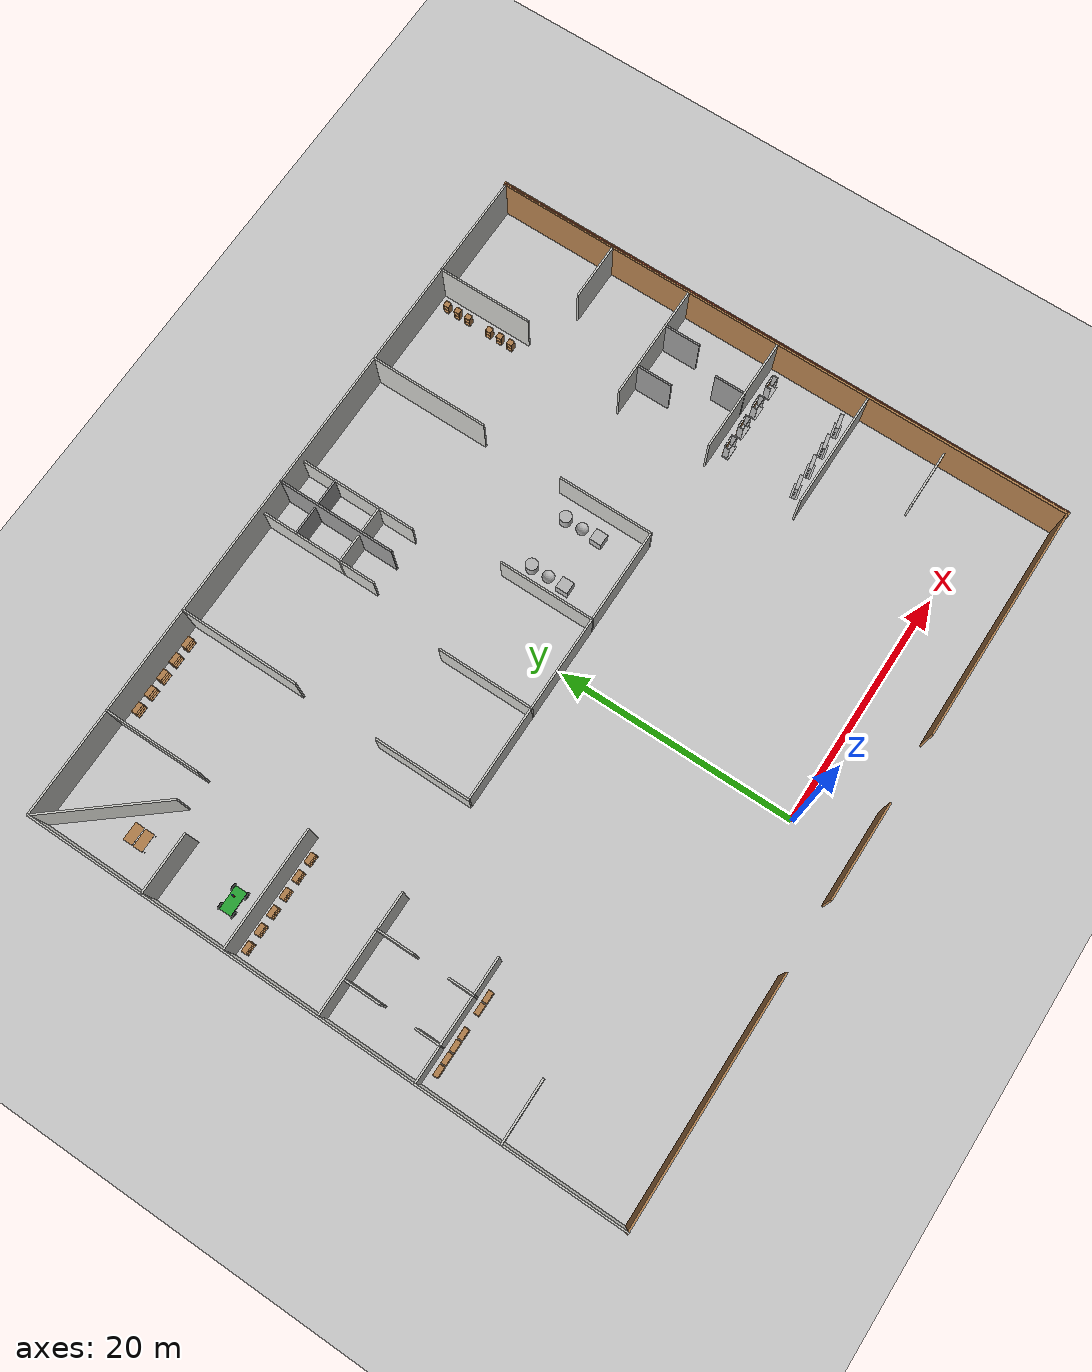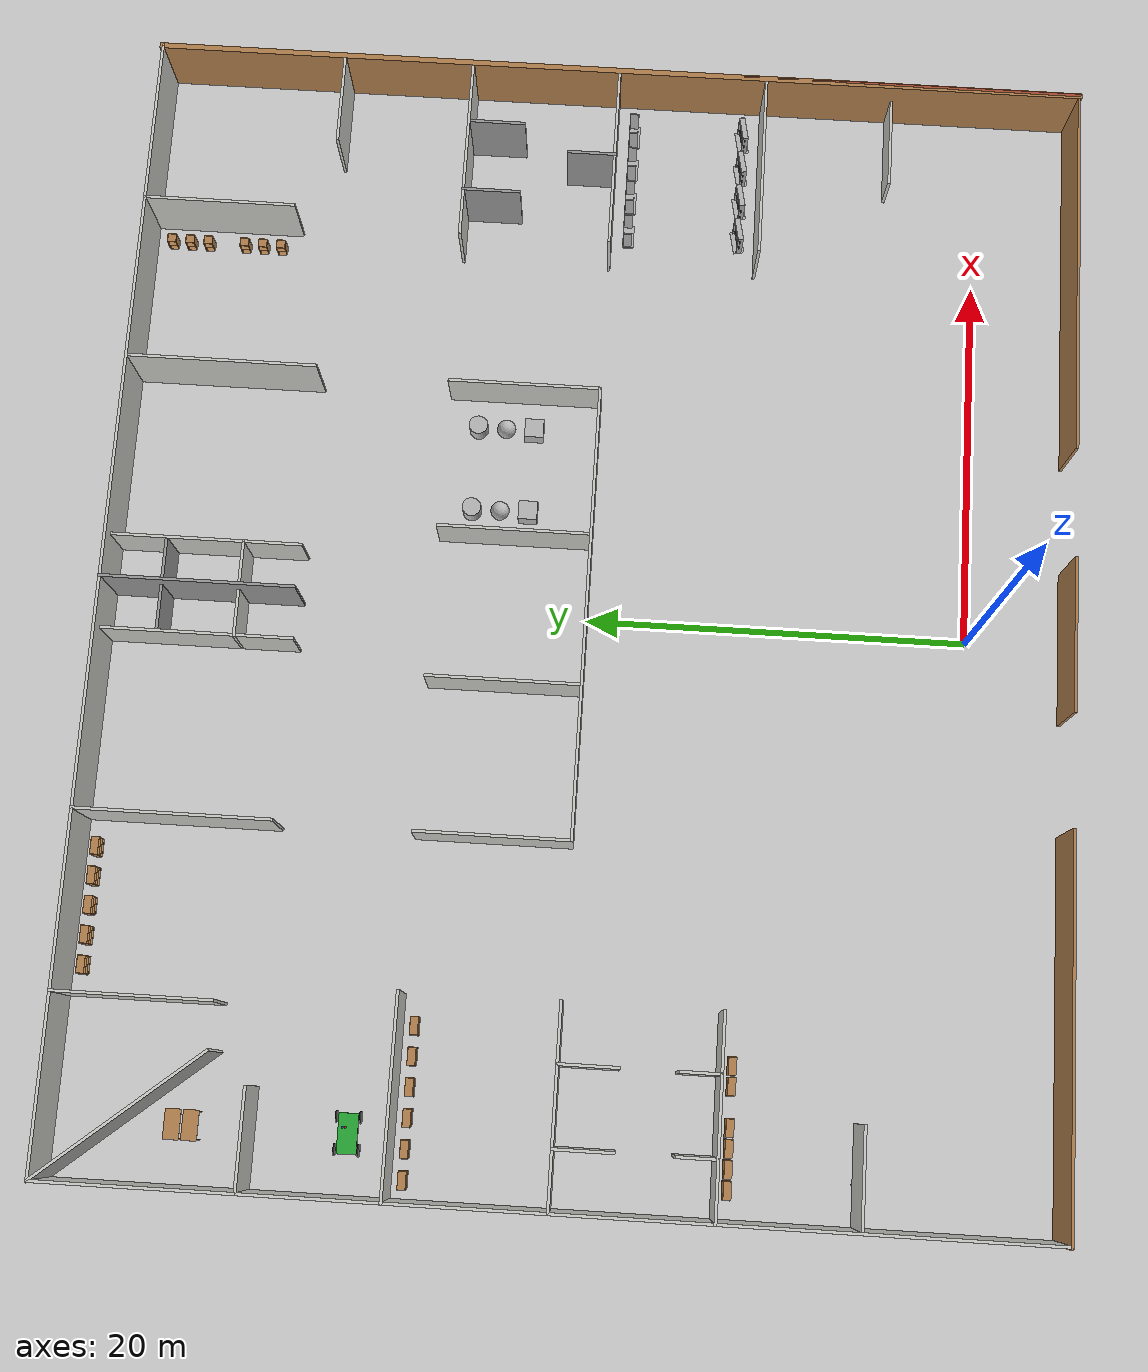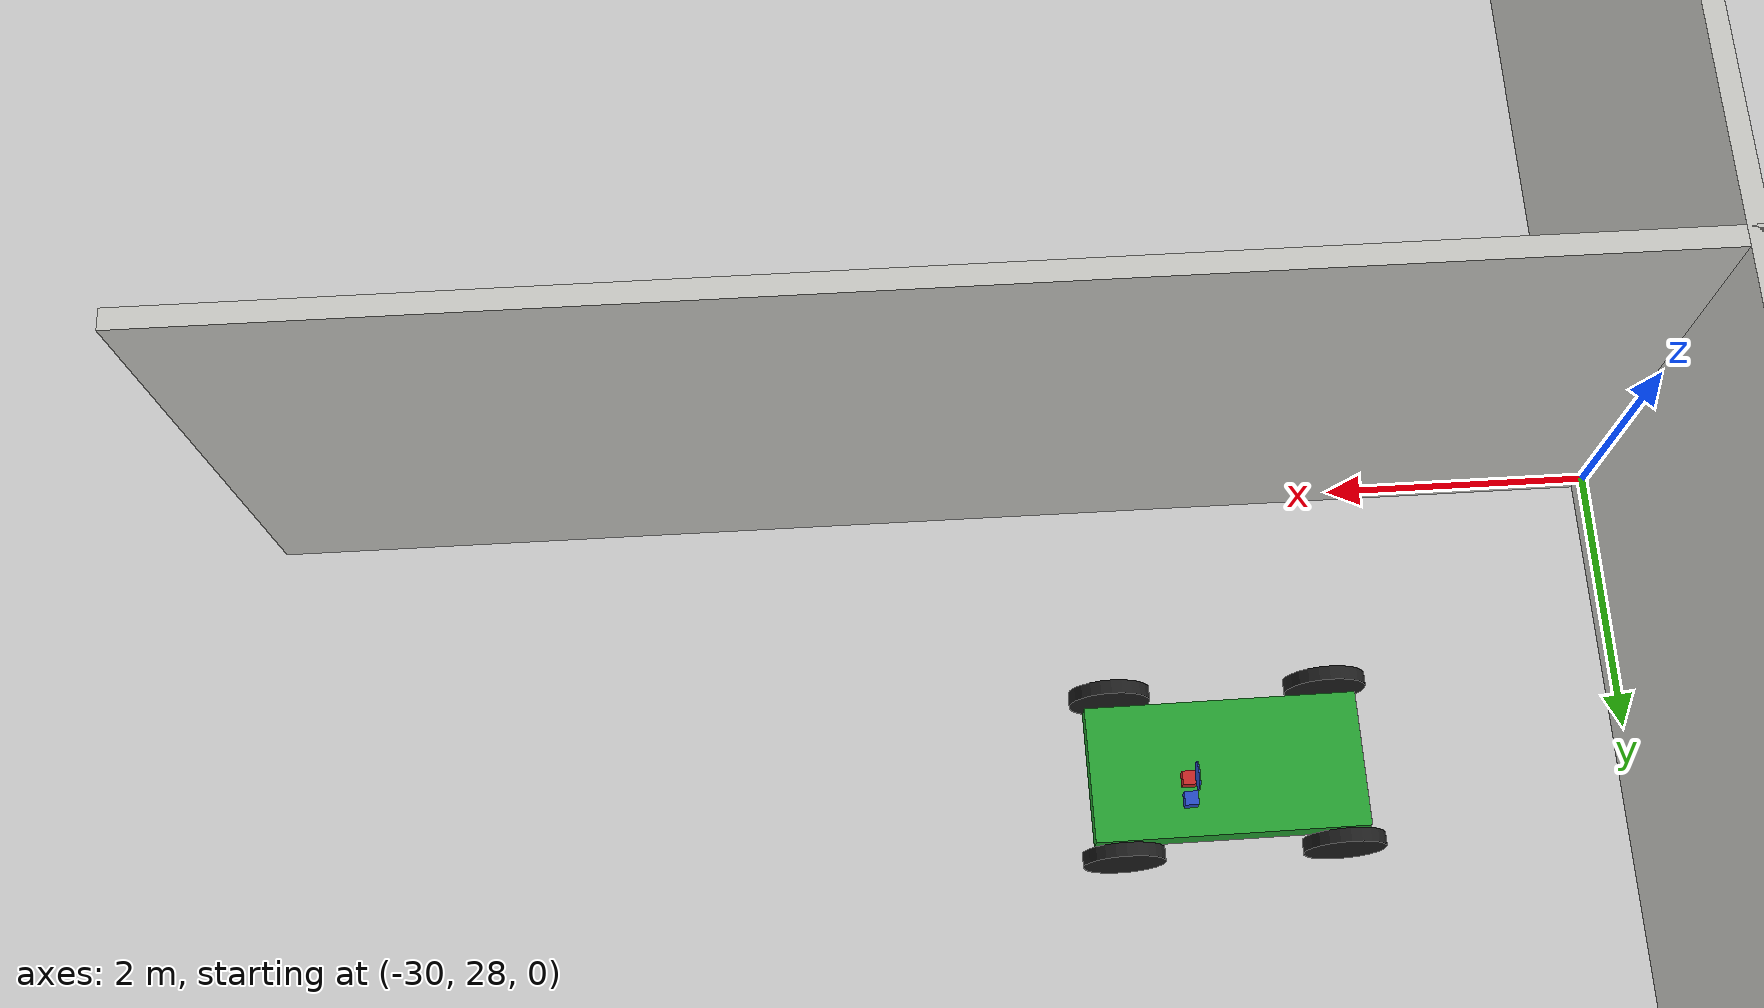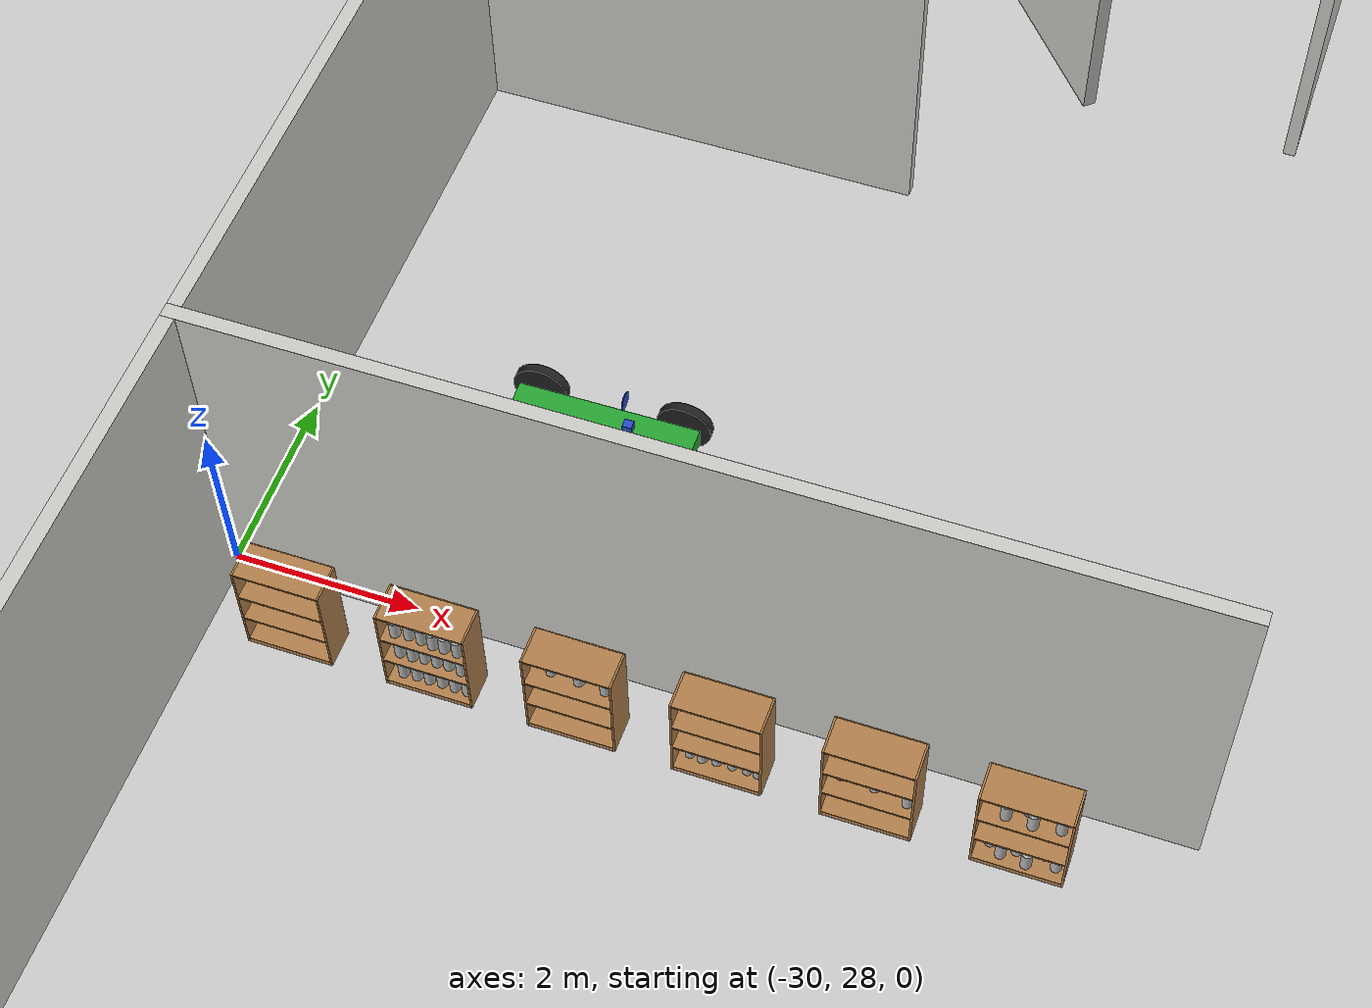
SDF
<sdf version="1.7">
 <world name="default">
  <light name="sun" type="directional">
   <pose>0 0 10 0 -0 0</pose>
   <diffuse>0.8 0.8 0.8 1</diffuse>
   <specular>0.2 0.2 0.2 1</specular>
   <attenuation>
    <range>1000</range>
    <constant>0.9</constant>
    <linear>0.01</linear>
    <quadratic>0.001</quadratic>
   </attenuation>
   <direction>-0.5 0.1 -0.9</direction>
   <spot><inner_angle>0</inner_angle><outer_angle>0</outer_angle><falloff>0</falloff></spot>
  </light>
  <model name="ground_plane">
   <static>1</static>
   <link name="link">
    <collision name="collision">
     <geometry><plane><normal>0 0 1</normal><size>100 100</size></plane></geometry>
     <surface>
      <contact><collide_bitmask>65535</collide_bitmask></contact>
      <friction><ode><mu>100</mu><mu2>50</mu2></ode></friction>
     </surface>
    </collision>
    <visual name="visual">
     <cast_shadows>0</cast_shadows>
     <geometry><plane><normal>0 0 1</normal><size>100 100</size></plane></geometry>
     <material>
      <script><uri>file://media/materials/scripts/gazebo.material</uri><name>Gazebo/Grey</name></script>
     </material>
    </visual>
   </link>
  </model>
  <gravity>0 0 -9.8</gravity>
  <magnetic_field>6e-06 2.3e-05 -4.2e-05</magnetic_field>
  <atmosphere type="adiabatic"/>
  <physics type="ode">
   <max_step_size>0.001</max_step_size>
   <real_time_factor>1</real_time_factor>
   <real_time_update_rate>1000</real_time_update_rate>
  </physics>
  <scene><ambient>0.4 0.4 0.4 1</ambient><background>0.7 0.7 0.7 1</background><shadows>1</shadows></scene>
  <spherical_coordinates>
   <surface_model>EARTH_WGS84</surface_model>
   <latitude_deg>0</latitude_deg>
   <longitude_deg>0</longitude_deg>
   <elevation>0</elevation>
   <heading_deg>0</heading_deg>
  </spherical_coordinates>
  <model name="demo03">
   <pose>0 20 0 0 -0 0</pose>
   <link name="Wall_0">
    <collision name="Wall_0_Collision">
     <geometry><box><size>8.14 0.14 4</size></box></geometry>
     <pose>0 0 2 0 -0 0</pose>
    </collision>
    <visual name="Wall_0_Visual">
     <pose>0 0 2 0 -0 0</pose>
     <geometry><box><size>8.14 0.14 4</size></box></geometry>
     <material>
      <script><uri>file://media/materials/scripts/gazebo.material</uri><name>Gazebo/CeilingTiled</name></script>
      <ambient>1 1 1 1</ambient>
     </material>
     <meta><layer>0</layer></meta>
    </visual>
    <pose>-20.9847 20.9847 0 0 -0 -1.5708</pose>
   </link>
   <link name="Wall_12">
    <collision name="Wall_12_Collision">
     <geometry><box><size>10.15 0.15 3</size></box></geometry>
     <pose>0 0 1.5 0 -0 0</pose>
    </collision>
    <visual name="Wall_12_Visual">
     <pose>0 0 1.5 0 -0 0</pose>
     <geometry><box><size>10.15 0.15 3</size></box></geometry>
     <material>
      <script><uri>file://media/materials/scripts/gazebo.material</uri><name>Gazebo/CeilingTiled</name></script>
      <ambient>1 1 1 1</ambient>
     </material>
     <meta><layer>0</layer></meta>
    </visual>
    <pose>-2.48471 19.9847 0 0 -0 1.5708</pose>
   </link>
   <link name="Wall_14">
    <collision name="Wall_14_Collision">
     <geometry><box><size>10.15 0.15 3</size></box></geometry>
     <pose>0 0 1.5 0 -0 0</pose>
    </collision>
    <visual name="Wall_14_Visual">
     <pose>0 0 1.5 0 -0 0</pose>
     <geometry><box><size>10.15 0.15 3</size></box></geometry>
     <material>
      <script><uri>file://media/materials/scripts/gazebo.material</uri><name>Gazebo/CeilingTiled</name></script>
      <ambient>1 1 1 1</ambient>
     </material>
     <meta><layer>0</layer></meta>
    </visual>
    <pose>2.51529 19.9847 0 0 -0 1.5708</pose>
   </link>
   <link name="Wall_16">
    <collision name="Wall_16_Collision">
     <geometry><box><size>5.15 0.15 3</size></box></geometry>
     <pose>0 0 1.5 0 -0 0</pose>
    </collision>
    <visual name="Wall_16_Visual">
     <pose>0 0 1.5 0 -0 0</pose>
     <geometry><box><size>5.15 0.15 3</size></box></geometry>
     <material>
      <script><uri>file://media/materials/scripts/gazebo.material</uri><name>Gazebo/Grey</name></script>
      <ambient>1 1 1 1</ambient>
     </material>
     <meta><layer>0</layer></meta>
    </visual>
    <pose>0.015289 21.9847 0 0 -0 0</pose>
   </link>
   <link name="Wall_18">
    <collision name="Wall_18_Collision">
     <geometry><box><size>5.15 0.15 3</size></box></geometry>
     <pose>0 0 1.5 0 -0 0</pose>
    </collision>
    <visual name="Wall_18_Visual">
     <pose>0 0 1.5 0 -0 0</pose>
     <geometry><box><size>5.15 0.15 3</size></box></geometry>
     <material>
      <script><uri>file://media/materials/scripts/gazebo.material</uri><name>Gazebo/CeilingTiled</name></script>
      <ambient>1 1 1 1</ambient>
     </material>
     <meta><layer>0</layer></meta>
    </visual>
    <pose>0.015289 17.9847 0 0 -0 0</pose>
   </link>
   <link name="Wall_2">
    <collision name="Wall_2_Collision">
     <geometry><box><size>10.15 0.15 4</size></box></geometry>
     <pose>0 0 2 0 -0 0</pose>
    </collision>
    <visual name="Wall_2_Visual">
     <pose>0 0 2 0 -0 0</pose>
     <geometry><box><size>10.15 0.15 4</size></box></geometry>
     <material>
      <script><uri>file://media/materials/scripts/gazebo.material</uri><name>Gazebo/CeilingTiled</name></script>
      <ambient>1 1 1 1</ambient>
     </material>
     <meta><layer>0</layer></meta>
    </visual>
    <pose>-11.9847 19.9847 0 0 -0 -1.5708</pose>
   </link>
   <link name="Wall_20">
    <collision name="Wall_20_Collision">
     <geometry><box><size>5.15 0.15 4</size></box></geometry>
     <pose>0 0 2 0 -0 0</pose>
    </collision>
    <visual name="Wall_20_Visual">
     <pose>0 0 2 0 -0 0</pose>
     <geometry><box><size>5.15 0.15 4</size></box></geometry>
     <material>
      <script><uri>file://media/materials/scripts/gazebo.material</uri><name>Gazebo/CeilingTiled</name></script>
      <ambient>1 1 1 1</ambient>
     </material>
     <meta><layer>0</layer></meta>
    </visual>
    <pose>-27.4847 14.9847 0 0 -0 0</pose>
   </link>
   <link name="Wall_22">
    <collision name="Wall_22_Collision">
     <geometry><box><size>5.15 0.15 4</size></box></geometry>
     <pose>0 0 2 0 -0 0</pose>
    </collision>
    <visual name="Wall_22_Visual">
     <pose>0 0 2 0 -0 0</pose>
     <geometry><box><size>5.15 0.15 4</size></box></geometry>
     <material>
      <script><uri>file://media/materials/scripts/gazebo.material</uri><name>Gazebo/CeilingTiled</name></script>
      <ambient>1 1 1 1</ambient>
     </material>
     <meta><layer>0</layer></meta>
    </visual>
    <pose>27.5153 14.9847 0 0 -0 0</pose>
   </link>
   <link name="Wall_24">
    <collision name="Wall_24_Collision">
     <geometry><box><size>10.15 0.15 4</size></box></geometry>
     <pose>0 0 2 0 -0 0</pose>
    </collision>
    <visual name="Wall_24_Visual">
     <pose>0 0 2 0 -0 0</pose>
     <geometry><box><size>10.15 0.15 4</size></box></geometry>
     <material>
      <script><uri>file://media/materials/scripts/gazebo.material</uri><name>Gazebo/CeilingTiled</name></script>
      <ambient>1 1 1 1</ambient>
     </material>
     <meta><layer>0</layer></meta>
    </visual>
    <pose>-24.9847 7.98471 0 0 -0 0</pose>
   </link>
   <link name="Wall_26">
    <collision name="Wall_26_Collision">
     <geometry><box><size>10.15 0.15 4</size></box></geometry>
     <pose>0 0 2 0 -0 0</pose>
    </collision>
    <visual name="Wall_26_Visual">
     <pose>0 0 2 0 -0 0</pose>
     <geometry><box><size>10.15 0.15 4</size></box></geometry>
     <material>
      <script><uri>file://media/materials/scripts/gazebo.material</uri><name>Gazebo/CeilingTiled</name></script>
      <ambient>1 1 1 1</ambient>
     </material>
     <meta><layer>0</layer></meta>
    </visual>
    <pose>-24.9847 -0.015289 0 0 -0 0</pose>
   </link>
   <link name="Wall_28">
    <collision name="Wall_28_Collision">
     <geometry><box><size>10.15 0.15 4</size></box></geometry>
     <pose>0 0 2 0 -0 0</pose>
    </collision>
    <visual name="Wall_28_Visual">
     <pose>0 0 2 0 -0 0</pose>
     <geometry><box><size>10.15 0.15 4</size></box></geometry>
     <material>
      <script><uri>file://media/materials/scripts/gazebo.material</uri><name>Gazebo/CeilingTiled</name></script>
      <ambient>1 1 1 1</ambient>
     </material>
     <meta><layer>0</layer></meta>
    </visual>
    <pose>-24.9847 -8.01529 0 0 -0 0</pose>
   </link>
   <link name="Wall_30">
    <collision name="Wall_30_Collision">
     <geometry><box><size>5.15 0.15 4</size></box></geometry>
     <pose>0 0 2 0 -0 0</pose>
    </collision>
    <visual name="Wall_30_Visual">
     <pose>0 0 2 0 -0 0</pose>
     <geometry><box><size>5.15 0.15 4</size></box></geometry>
     <material>
      <script><uri>file://media/materials/scripts/gazebo.material</uri><name>Gazebo/CeilingTiled</name></script>
      <ambient>1 1 1 1</ambient>
     </material>
     <meta><layer>0</layer></meta>
    </visual>
    <pose>-27.4847 -15.0153 0 0 -0 0</pose>
   </link>
   <link name="Wall_32">
    <collision name="Wall_32_Collision">
     <geometry><box><size>10.15 0.15 4</size></box></geometry>
     <pose>0 0 2 0 -0 0</pose>
    </collision>
    <visual name="Wall_32_Visual">
     <pose>0 0 2 0 -0 0</pose>
     <geometry><box><size>10.15 0.15 4</size></box></geometry>
     <material>
      <script><uri>file://media/materials/scripts/gazebo.material</uri><name>Gazebo/CeilingTiled</name></script>
      <ambient>1 1 1 1</ambient>
     </material>
     <meta><layer>0</layer></meta>
    </visual>
    <pose>25.0153 7.98471 0 0 -0 0</pose>
   </link>
   <link name="Wall_34">
    <collision name="Wall_34_Collision">
     <geometry><box><size>10.15 0.15 4</size></box></geometry>
     <pose>0 0 2 0 -0 0</pose>
    </collision>
    <visual name="Wall_34_Visual">
     <pose>0 0 2 0 -0 0</pose>
     <geometry><box><size>10.15 0.15 4</size></box></geometry>
     <material>
      <script><uri>file://media/materials/scripts/gazebo.material</uri><name>Gazebo/CeilingTiled</name></script>
      <ambient>1 1 1 1</ambient>
     </material>
     <meta><layer>0</layer></meta>
    </visual>
    <pose>25.0153 -0.015289 0 0 -0 0</pose>
   </link>
   <link name="Wall_36">
    <collision name="Wall_36_Collision">
     <geometry><box><size>10.15 0.15 4</size></box></geometry>
     <pose>0 0 2 0 -0 0</pose>
    </collision>
    <visual name="Wall_36_Visual">
     <pose>0 0 2 0 -0 0</pose>
     <geometry><box><size>10.15 0.15 4</size></box></geometry>
     <material>
      <script><uri>file://media/materials/scripts/gazebo.material</uri><name>Gazebo/CeilingTiled</name></script>
      <ambient>1 1 1 1</ambient>
     </material>
     <meta><layer>0</layer></meta>
    </visual>
    <pose>25.0153 -8.01529 0 0 -0 0</pose>
   </link>
   <link name="Wall_38">
    <collision name="Wall_38_Collision">
     <geometry><box><size>5.15 0.15 2.5</size></box></geometry>
     <pose>0 0 1.25 0 -0 0</pose>
    </collision>
    <visual name="Wall_38_Visual">
     <pose>0 0 1.25 0 -0 0</pose>
     <geometry><box><size>5.15 0.15 2.5</size></box></geometry>
     <material>
      <script><uri>file://media/materials/scripts/gazebo.material</uri><name>Gazebo/CeilingTiled</name></script>
      <ambient>1 1 1 1</ambient>
     </material>
     <meta><layer>0</layer></meta>
    </visual>
    <pose>27.5153 -15.0153 0 0 -0 0</pose>
   </link>
   <link name="Wall_40">
    <collision name="Wall_40_Collision">
     <geometry><box><size>3.15 0.15 4</size></box></geometry>
     <pose>0 0 2 0 -0 0</pose>
    </collision>
    <visual name="Wall_40_Visual">
     <pose>0 0 2 0 -0 0</pose>
     <geometry><box><size>3.15 0.15 4</size></box></geometry>
     <material>
      <script><uri>file://media/materials/scripts/gazebo.material</uri><name>Gazebo/Grey</name></script>
      <ambient>1 1 1 1</ambient>
     </material>
     <meta><layer>0</layer></meta>
    </visual>
    <pose>26.5153 6.48471 0 0 -0 -1.5708</pose>
   </link>
   <link name="Wall_42">
    <collision name="Wall_42_Collision">
     <geometry><box><size>3.15 0.15 4</size></box></geometry>
     <pose>0 0 2 0 -0 0</pose>
    </collision>
    <visual name="Wall_42_Visual">
     <pose>0 0 2 0 -0 0</pose>
     <geometry><box><size>3.15 0.15 4</size></box></geometry>
     <material>
      <script><uri>file://media/materials/scripts/gazebo.material</uri><name>Gazebo/Grey</name></script>
      <ambient>1 1 1 1</ambient>
     </material>
     <meta><layer>0</layer></meta>
    </visual>
    <pose>22.5153 6.48471 0 0 -0 -1.5708</pose>
   </link>
   <link name="Wall_44">
    <collision name="Wall_44_Collision">
     <geometry><box><size>2.65 0.15 4</size></box></geometry>
     <pose>0 0 2 0 -0 0</pose>
    </collision>
    <visual name="Wall_44_Visual">
     <pose>0 0 2 0 -0 0</pose>
     <geometry><box><size>2.65 0.15 4</size></box></geometry>
     <material>
      <script><uri>file://media/materials/scripts/gazebo.material</uri><name>Gazebo/Grey</name></script>
      <ambient>1 1 1 1</ambient>
     </material>
     <meta><layer>0</layer></meta>
    </visual>
    <pose>25.0153 1.23471 0 0 -0 1.5708</pose>
   </link>
   <link name="Wall_46">
    <collision name="Wall_46_Collision">
     <geometry><box><size>3.15 0.15 4</size></box></geometry>
     <pose>0 0 2 0 -0 0</pose>
    </collision>
    <visual name="Wall_46_Visual">
     <pose>0 0 2 0 -0 0</pose>
     <geometry><box><size>3.15 0.15 4</size></box></geometry>
     <material>
      <script><uri>file://media/materials/scripts/gazebo.material</uri><name>Gazebo/CeilingTiled</name></script>
      <ambient>1 1 1 1</ambient>
     </material>
     <meta><layer>0</layer></meta>
    </visual>
    <pose>-26.9847 -1.51529 0 0 -0 -1.5708</pose>
   </link>
   <link name="Wall_48">
    <collision name="Wall_48_Collision">
     <geometry><box><size>3.15 0.15 4</size></box></geometry>
     <pose>0 0 2 0 -0 0</pose>
    </collision>
    <visual name="Wall_48_Visual">
     <pose>0 0 2 0 -0 0</pose>
     <geometry><box><size>3.15 0.15 4</size></box></geometry>
     <material>
      <script><uri>file://media/materials/scripts/gazebo.material</uri><name>Gazebo/CeilingTiled</name></script>
      <ambient>1 1 1 1</ambient>
     </material>
     <meta><layer>0</layer></meta>
    </visual>
    <pose>-22.9847 -1.51529 0 0 -0 -1.5708</pose>
   </link>
   <link name="Wall_5">
    <collision name="Wall_5_Collision">
     <geometry><box><size>10.15 0.15 4</size></box></geometry>
     <pose>0 0 2 0 -0 0</pose>
    </collision>
    <visual name="Wall_5_Visual">
     <pose>0 0 2 0 -0 0</pose>
     <geometry><box><size>10.15 0.15 4</size></box></geometry>
     <material>
      <script><uri>file://media/materials/scripts/gazebo.material</uri><name>Gazebo/Grey</name></script>
      <ambient>1 1 1 1</ambient>
     </material>
     <meta><layer>0</layer></meta>
    </visual>
    <pose>0.015289 19.9847 0 0 -0 -1.5708</pose>
   </link>
   <link name="Wall_50">
    <collision name="Wall_50_Collision">
     <geometry><box><size>2.15 0.15 4</size></box></geometry>
     <pose>0 0 2 0 -0 0</pose>
    </collision>
    <visual name="Wall_50_Visual">
     <pose>0 0 2 0 -0 0</pose>
     <geometry><box><size>2.15 0.15 4</size></box></geometry>
     <material>
      <script><uri>file://media/materials/scripts/gazebo.material</uri><name>Gazebo/CeilingTiled</name></script>
      <ambient>1 1 1 1</ambient>
     </material>
     <meta><layer>0</layer></meta>
    </visual>
    <pose>-26.9847 -7.01529 0 0 -0 1.5708</pose>
   </link>
   <link name="Wall_52">
    <collision name="Wall_52_Collision">
     <geometry><box><size>2.15 0.15 4</size></box></geometry>
     <pose>0 0 2 0 -0 0</pose>
    </collision>
    <visual name="Wall_52_Visual">
     <pose>0 0 2 0 -0 0</pose>
     <geometry><box><size>2.15 0.15 4</size></box></geometry>
     <material>
      <script><uri>file://media/materials/scripts/gazebo.material</uri><name>Gazebo/CeilingTiled</name></script>
      <ambient>1 1 1 1</ambient>
     </material>
     <meta><layer>0</layer></meta>
    </visual>
    <pose>-22.9847 -7.01529 0 0 -0 1.5708</pose>
   </link>
   <link name="Wall_54">
    <collision name="Wall_54_Collision">
     <geometry><box><size>10.5211 0.15 4</size></box></geometry>
     <pose>0 0 2 0 -0 0</pose>
    </collision>
    <visual name="Wall_54_Visual">
     <pose>0 0 2 0 -0 0</pose>
     <geometry><box><size>10.5211 0.15 4</size></box></geometry>
     <material>
      <script><uri>file://media/materials/scripts/gazebo.material</uri><name>Gazebo/CeilingTiled</name></script>
      <ambient>1 1 1 1</ambient>
     </material>
     <meta><layer>0</layer></meta>
    </visual>
    <pose>-26.6847 20.9847 0 0 -0 -0.880996</pose>
   </link>
   <link name="Wall_61">
    <collision name="Wall_61_Collision">
     <geometry><box><size>8.15 0.15 3</size></box></geometry>
     <pose>0 0 1.5 0 -0 0</pose>
    </collision>
    <visual name="Wall_61_Visual">
     <pose>0 0 1.5 0 -0 0</pose>
     <geometry><box><size>8.15 0.15 3</size></box></geometry>
     <material>
      <script><uri>file://media/materials/scripts/gazebo.material</uri><name>Gazebo/CeilingTiled</name></script>
      <ambient>1 1 1 1</ambient>
     </material>
     <meta><layer>0</layer></meta>
    </visual>
    <pose>12.0153 3.98471 0 0 -0 -1.5708</pose>
   </link>
   <link name="Wall_63">
    <collision name="Wall_63_Collision">
     <geometry><box><size>8.15 0.15 3</size></box></geometry>
     <pose>0 0 1.5 0 -0 0</pose>
    </collision>
    <visual name="Wall_63_Visual">
     <pose>0 0 1.5 0 -0 0</pose>
     <geometry><box><size>8.15 0.15 3</size></box></geometry>
     <material>
      <script><uri>file://media/materials/scripts/gazebo.material</uri><name>Gazebo/CeilingTiled</name></script>
      <ambient>1 1 1 1</ambient>
     </material>
     <meta><layer>0</layer></meta>
    </visual>
    <pose>-11.9847 3.98471 0 0 -0 -1.5708</pose>
   </link>
   <link name="Wall_65">
    <collision name="Wall_65_Collision">
     <geometry><box><size>8.15 0.15 3</size></box></geometry>
     <pose>0 0 1.5 0 -0 0</pose>
    </collision>
    <visual name="Wall_65_Visual">
     <pose>0 0 1.5 0 -0 0</pose>
     <geometry><box><size>8.15 0.15 3</size></box></geometry>
     <material>
      <script><uri>file://media/materials/scripts/gazebo.material</uri><name>Gazebo/CeilingTiled</name></script>
      <ambient>1 1 1 1</ambient>
     </material>
     <meta><layer>0</layer></meta>
    </visual>
    <pose>4.01529 3.98471 0 0 -0 -1.5708</pose>
   </link>
   <link name="Wall_67">
    <collision name="Wall_67_Collision">
     <geometry><box><size>8.15 0.15 3</size></box></geometry>
     <pose>0 0 1.5 0 -0 0</pose>
    </collision>
    <visual name="Wall_67_Visual">
     <pose>0 0 1.5 0 -0 0</pose>
     <geometry><box><size>8.15 0.15 3</size></box></geometry>
     <material>
      <script><uri>file://media/materials/scripts/gazebo.material</uri><name>Gazebo/CeilingTiled</name></script>
      <ambient>1 1 1 1</ambient>
     </material>
     <meta><layer>0</layer></meta>
    </visual>
    <pose>-3.98471 3.98471 0 0 -0 -1.5708</pose>
   </link>
   <link name="Wall_69">
    <collision name="Wall_69_Collision">
     <geometry><box><size>24.15 0.15 3</size></box></geometry>
     <pose>0 0 1.5 0 -0 0</pose>
    </collision>
    <visual name="Wall_69_Visual">
     <pose>0 0 1.5 0 -0 0</pose>
     <geometry><box><size>24.15 0.15 3</size></box></geometry>
     <material>
      <script><uri>file://media/materials/scripts/gazebo.material</uri><name>Gazebo/CeilingTiled</name></script>
      <ambient>1 1 1 1</ambient>
     </material>
     <meta><layer>0</layer></meta>
    </visual>
    <pose>0.015289 -0.015289 0 0 -0 0</pose>
   </link>
   <link name="Wall_7">
    <collision name="Wall_7_Collision">
     <geometry><box><size>10.15 0.15 4</size></box></geometry>
     <pose>0 0 2 0 -0 0</pose>
    </collision>
    <visual name="Wall_7_Visual">
     <pose>0 0 2 0 -0 0</pose>
     <geometry><box><size>10.15 0.15 4</size></box></geometry>
     <material>
      <script><uri>file://media/materials/scripts/gazebo.material</uri><name>Gazebo/CeilingTiled</name></script>
      <ambient>1 1 1 1</ambient>
     </material>
     <meta><layer>0</layer></meta>
    </visual>
    <pose>12.0153 19.9847 0 0 -0 -1.5708</pose>
   </link>
   <link name="Wall_71">
    <collision name="Wall_71_Collision">
     <geometry><box><size>50.15 0.15 4</size></box></geometry>
     <pose>0 0 2 0 -0 0</pose>
    </collision>
    <visual name="Wall_71_Visual">
     <pose>0 0 2 0 -0 0</pose>
     <geometry><box><size>50.15 0.15 4</size></box></geometry>
     <material>
      <script><uri>file://media/materials/scripts/gazebo.material</uri><name>Gazebo/CeilingTiled</name></script>
      <ambient>0.560784 0.34902 0.00784314 1</ambient>
     </material>
     <meta><layer>0</layer></meta>
    </visual>
    <pose>-29.9847 -0.015289 0 0 -0 1.5708</pose>
   </link>
   <link name="Wall_73">
    <collision name="Wall_73_Collision">
     <geometry><box><size>60.15 0.15 4</size></box></geometry>
     <pose>0 0 2 0 -0 0</pose>
    </collision>
    <visual name="Wall_73_Visual">
     <pose>0 0 2 0 -0 0</pose>
     <geometry><box><size>60.15 0.15 4</size></box></geometry>
     <material>
      <script><uri>file://media/materials/scripts/gazebo.material</uri><name>Gazebo/CeilingTiled</name></script>
      <ambient>0.560784 0.34902 0.00784314 1</ambient>
     </material>
     <meta><layer>0</layer></meta>
    </visual>
    <pose>0.015289 24.9847 0 0 -0 0</pose>
   </link>
   <link name="Wall_75">
    <collision name="Wall_75_Collision">
     <geometry><box><size>50.15 0.15 4</size></box></geometry>
     <pose>0 0 2 0 -0 0</pose>
    </collision>
    <visual name="Wall_75_Visual">
     <pose>0 0 2 0 -0 0</pose>
     <geometry><box><size>50.15 0.15 4</size></box></geometry>
     <material>
      <script><uri>file://media/materials/scripts/gazebo.material</uri><name>Gazebo/Bricks</name></script>
      <ambient>1 1 1 1</ambient>
     </material>
     <meta><layer>0</layer></meta>
    </visual>
    <pose>30.0153 -0.015289 0 0 -0 -1.5708</pose>
   </link>
   <link name="Wall_9">
    <collision name="Wall_9_Collision">
     <geometry><box><size>8.15 0.15 4</size></box></geometry>
     <pose>0 0 2 0 -0 0</pose>
    </collision>
    <visual name="Wall_9_Visual">
     <pose>0 0 2 0 -0 0</pose>
     <geometry><box><size>8.15 0.15 4</size></box></geometry>
     <material>
      <script><uri>file://media/materials/scripts/gazebo.material</uri><name>Gazebo/CeilingTiled</name></script>
      <ambient>1 1 1 1</ambient>
     </material>
     <meta><layer>0</layer></meta>
    </visual>
    <pose>21.0153 20.9847 0 0 -0 -1.5708</pose>
   </link>
   <static>1</static>
  </model>
  <model name="bookshelf_clone">
   <static>1</static>
   <link name="link">
    <inertial><mass>1</mass></inertial>
    <collision name="back">
     <pose>0 0.005 0.6 0 -0 0</pose>
     <geometry><box><size>0.9 0.01 1.2</size></box></geometry>
    </collision>
    <visual name="visual1">
     <pose>0 0.005 0.6 0 -0 0</pose>
     <geometry><box><size>0.9 0.01 1.2</size></box></geometry>
     <material>
      <script><uri>file://media/materials/scripts/gazebo.material</uri><name>Gazebo/Wood</name></script>
     </material>
    </visual>
    <collision name="left_side">
     <pose>0.45 -0.195 0.6 0 -0 0</pose>
     <geometry><box><size>0.02 0.4 1.2</size></box></geometry>
    </collision>
    <visual name="visual2">
     <pose>0.45 -0.195 0.6 0 -0 0</pose>
     <geometry><box><size>0.02 0.4 1.2</size></box></geometry>
     <material>
      <script><uri>file://media/materials/scripts/gazebo.material</uri><name>Gazebo/Wood</name></script>
     </material>
    </visual>
    <collision name="right_side">
     <pose>-0.45 -0.195 0.6 0 -0 0</pose>
     <geometry><box><size>0.02 0.4 1.2</size></box></geometry>
    </collision>
    <visual name="visual3">
     <pose>-0.45 -0.195 0.6 0 -0 0</pose>
     <geometry><box><size>0.02 0.4 1.2</size></box></geometry>
     <material>
      <script><uri>file://media/materials/scripts/gazebo.material</uri><name>Gazebo/Wood</name></script>
     </material>
    </visual>
    <collision name="bottom">
     <pose>0 -0.195 0.03 0 -0 0</pose>
     <geometry><box><size>0.88 0.4 0.06</size></box></geometry>
    </collision>
    <visual name="visual4">
     <pose>0 -0.195 0.03 0 -0 0</pose>
     <geometry><box><size>0.88 0.4 0.06</size></box></geometry>
     <material>
      <script><uri>file://media/materials/scripts/gazebo.material</uri><name>Gazebo/Wood</name></script>
     </material>
    </visual>
    <collision name="top">
     <pose>0 -0.195 1.19 0 -0 0</pose>
     <geometry><box><size>0.88 0.4 0.02</size></box></geometry>
    </collision>
    <visual name="visual5">
     <pose>0 -0.195 1.19 0 -0 0</pose>
     <geometry><box><size>0.88 0.4 0.02</size></box></geometry>
     <material>
      <script><uri>file://media/materials/scripts/gazebo.material</uri><name>Gazebo/Wood</name></script>
     </material>
    </visual>
    <collision name="low_shelf">
     <pose>0 -0.195 0.43 0 -0 0</pose>
     <geometry><box><size>0.88 0.4 0.02</size></box></geometry>
    </collision>
    <visual name="visual6">
     <pose>0 -0.195 0.43 0 -0 0</pose>
     <geometry><box><size>0.88 0.4 0.02</size></box></geometry>
     <material>
      <script><uri>file://media/materials/scripts/gazebo.material</uri><name>Gazebo/Wood</name></script>
     </material>
    </visual>
    <collision name="high_shelf">
     <pose>0 -0.195 0.8 0 -0 0</pose>
     <geometry><box><size>0.88 0.4 0.02</size></box></geometry>
    </collision>
    <visual name="visual7">
     <pose>0 -0.195 0.8 0 -0 0</pose>
     <geometry><box><size>0.88 0.4 0.02</size></box></geometry>
     <material>
      <script><uri>file://media/materials/scripts/gazebo.material</uri><name>Gazebo/Wood</name></script>
     </material>
    </visual>
   </link>
   <pose>-27.5 11.5 0 0 -0 0</pose>
  </model>
  <model name="bookshelf_clone_0">
   <static>1</static>
   <link name="link">
    <inertial><mass>1</mass></inertial>
    <collision name="back">
     <pose>0 0.005 0.6 0 -0 0</pose>
     <geometry><box><size>0.9 0.01 1.2</size></box></geometry>
    </collision>
    <visual name="visual1">
     <pose>0 0.005 0.6 0 -0 0</pose>
     <geometry><box><size>0.9 0.01 1.2</size></box></geometry>
     <material>
      <script><uri>file://media/materials/scripts/gazebo.material</uri><name>Gazebo/Wood</name></script>
     </material>
    </visual>
    <collision name="left_side">
     <pose>0.45 -0.195 0.6 0 -0 0</pose>
     <geometry><box><size>0.02 0.4 1.2</size></box></geometry>
    </collision>
    <visual name="visual2">
     <pose>0.45 -0.195 0.6 0 -0 0</pose>
     <geometry><box><size>0.02 0.4 1.2</size></box></geometry>
     <material>
      <script><uri>file://media/materials/scripts/gazebo.material</uri><name>Gazebo/Wood</name></script>
     </material>
    </visual>
    <collision name="right_side">
     <pose>-0.45 -0.195 0.6 0 -0 0</pose>
     <geometry><box><size>0.02 0.4 1.2</size></box></geometry>
    </collision>
    <visual name="visual3">
     <pose>-0.45 -0.195 0.6 0 -0 0</pose>
     <geometry><box><size>0.02 0.4 1.2</size></box></geometry>
     <material>
      <script><uri>file://media/materials/scripts/gazebo.material</uri><name>Gazebo/Wood</name></script>
     </material>
    </visual>
    <collision name="bottom">
     <pose>0 -0.195 0.03 0 -0 0</pose>
     <geometry><box><size>0.88 0.4 0.06</size></box></geometry>
    </collision>
    <visual name="visual4">
     <pose>0 -0.195 0.03 0 -0 0</pose>
     <geometry><box><size>0.88 0.4 0.06</size></box></geometry>
     <material>
      <script><uri>file://media/materials/scripts/gazebo.material</uri><name>Gazebo/Wood</name></script>
     </material>
    </visual>
    <collision name="top">
     <pose>0 -0.195 1.19 0 -0 0</pose>
     <geometry><box><size>0.88 0.4 0.02</size></box></geometry>
    </collision>
    <visual name="visual5">
     <pose>0 -0.195 1.19 0 -0 0</pose>
     <geometry><box><size>0.88 0.4 0.02</size></box></geometry>
     <material>
      <script><uri>file://media/materials/scripts/gazebo.material</uri><name>Gazebo/Wood</name></script>
     </material>
    </visual>
    <collision name="low_shelf">
     <pose>0 -0.195 0.43 0 -0 0</pose>
     <geometry><box><size>0.88 0.4 0.02</size></box></geometry>
    </collision>
    <visual name="visual6">
     <pose>0 -0.195 0.43 0 -0 0</pose>
     <geometry><box><size>0.88 0.4 0.02</size></box></geometry>
     <material>
      <script><uri>file://media/materials/scripts/gazebo.material</uri><name>Gazebo/Wood</name></script>
     </material>
    </visual>
    <collision name="high_shelf">
     <pose>0 -0.195 0.8 0 -0 0</pose>
     <geometry><box><size>0.88 0.4 0.02</size></box></geometry>
    </collision>
    <visual name="visual7">
     <pose>0 -0.195 0.8 0 -0 0</pose>
     <geometry><box><size>0.88 0.4 0.02</size></box></geometry>
     <material>
      <script><uri>file://media/materials/scripts/gazebo.material</uri><name>Gazebo/Wood</name></script>
     </material>
    </visual>
   </link>
   <pose>-26.5 11.5 0 0 -0 0</pose>
  </model>
  <model name="bookshelf_clone_1">
   <static>1</static>
   <link name="link">
    <inertial><mass>1</mass></inertial>
    <collision name="back">
     <pose>0 0.005 0.6 0 -0 0</pose>
     <geometry><box><size>0.9 0.01 1.2</size></box></geometry>
    </collision>
    <visual name="visual1">
     <pose>0 0.005 0.6 0 -0 0</pose>
     <geometry><box><size>0.9 0.01 1.2</size></box></geometry>
     <material>
      <script><uri>file://media/materials/scripts/gazebo.material</uri><name>Gazebo/Wood</name></script>
     </material>
    </visual>
    <collision name="left_side">
     <pose>0.45 -0.195 0.6 0 -0 0</pose>
     <geometry><box><size>0.02 0.4 1.2</size></box></geometry>
    </collision>
    <visual name="visual2">
     <pose>0.45 -0.195 0.6 0 -0 0</pose>
     <geometry><box><size>0.02 0.4 1.2</size></box></geometry>
     <material>
      <script><uri>file://media/materials/scripts/gazebo.material</uri><name>Gazebo/Wood</name></script>
     </material>
    </visual>
    <collision name="right_side">
     <pose>-0.45 -0.195 0.6 0 -0 0</pose>
     <geometry><box><size>0.02 0.4 1.2</size></box></geometry>
    </collision>
    <visual name="visual3">
     <pose>-0.45 -0.195 0.6 0 -0 0</pose>
     <geometry><box><size>0.02 0.4 1.2</size></box></geometry>
     <material>
      <script><uri>file://media/materials/scripts/gazebo.material</uri><name>Gazebo/Wood</name></script>
     </material>
    </visual>
    <collision name="bottom">
     <pose>0 -0.195 0.03 0 -0 0</pose>
     <geometry><box><size>0.88 0.4 0.06</size></box></geometry>
    </collision>
    <visual name="visual4">
     <pose>0 -0.195 0.03 0 -0 0</pose>
     <geometry><box><size>0.88 0.4 0.06</size></box></geometry>
     <material>
      <script><uri>file://media/materials/scripts/gazebo.material</uri><name>Gazebo/Wood</name></script>
     </material>
    </visual>
    <collision name="top">
     <pose>0 -0.195 1.19 0 -0 0</pose>
     <geometry><box><size>0.88 0.4 0.02</size></box></geometry>
    </collision>
    <visual name="visual5">
     <pose>0 -0.195 1.19 0 -0 0</pose>
     <geometry><box><size>0.88 0.4 0.02</size></box></geometry>
     <material>
      <script><uri>file://media/materials/scripts/gazebo.material</uri><name>Gazebo/Wood</name></script>
     </material>
    </visual>
    <collision name="low_shelf">
     <pose>0 -0.195 0.43 0 -0 0</pose>
     <geometry><box><size>0.88 0.4 0.02</size></box></geometry>
    </collision>
    <visual name="visual6">
     <pose>0 -0.195 0.43 0 -0 0</pose>
     <geometry><box><size>0.88 0.4 0.02</size></box></geometry>
     <material>
      <script><uri>file://media/materials/scripts/gazebo.material</uri><name>Gazebo/Wood</name></script>
     </material>
    </visual>
    <collision name="high_shelf">
     <pose>0 -0.195 0.8 0 -0 0</pose>
     <geometry><box><size>0.88 0.4 0.02</size></box></geometry>
    </collision>
    <visual name="visual7">
     <pose>0 -0.195 0.8 0 -0 0</pose>
     <geometry><box><size>0.88 0.4 0.02</size></box></geometry>
     <material>
      <script><uri>file://media/materials/scripts/gazebo.material</uri><name>Gazebo/Wood</name></script>
     </material>
    </visual>
   </link>
   <pose>-25.5 11.5 0 0 -0 0</pose>
  </model>
  <model name="bookshelf_clone_3">
   <static>1</static>
   <link name="link">
    <inertial><mass>1</mass></inertial>
    <collision name="back">
     <pose>0 0.005 0.6 0 -0 0</pose>
     <geometry><box><size>0.9 0.01 1.2</size></box></geometry>
    </collision>
    <visual name="visual1">
     <pose>0 0.005 0.6 0 -0 0</pose>
     <geometry><box><size>0.9 0.01 1.2</size></box></geometry>
     <material>
      <script><uri>file://media/materials/scripts/gazebo.material</uri><name>Gazebo/Wood</name></script>
     </material>
    </visual>
    <collision name="left_side">
     <pose>0.45 -0.195 0.6 0 -0 0</pose>
     <geometry><box><size>0.02 0.4 1.2</size></box></geometry>
    </collision>
    <visual name="visual2">
     <pose>0.45 -0.195 0.6 0 -0 0</pose>
     <geometry><box><size>0.02 0.4 1.2</size></box></geometry>
     <material>
      <script><uri>file://media/materials/scripts/gazebo.material</uri><name>Gazebo/Wood</name></script>
     </material>
    </visual>
    <collision name="right_side">
     <pose>-0.45 -0.195 0.6 0 -0 0</pose>
     <geometry><box><size>0.02 0.4 1.2</size></box></geometry>
    </collision>
    <visual name="visual3">
     <pose>-0.45 -0.195 0.6 0 -0 0</pose>
     <geometry><box><size>0.02 0.4 1.2</size></box></geometry>
     <material>
      <script><uri>file://media/materials/scripts/gazebo.material</uri><name>Gazebo/Wood</name></script>
     </material>
    </visual>
    <collision name="bottom">
     <pose>0 -0.195 0.03 0 -0 0</pose>
     <geometry><box><size>0.88 0.4 0.06</size></box></geometry>
    </collision>
    <visual name="visual4">
     <pose>0 -0.195 0.03 0 -0 0</pose>
     <geometry><box><size>0.88 0.4 0.06</size></box></geometry>
     <material>
      <script><uri>file://media/materials/scripts/gazebo.material</uri><name>Gazebo/Wood</name></script>
     </material>
    </visual>
    <collision name="top">
     <pose>0 -0.195 1.19 0 -0 0</pose>
     <geometry><box><size>0.88 0.4 0.02</size></box></geometry>
    </collision>
    <visual name="visual5">
     <pose>0 -0.195 1.19 0 -0 0</pose>
     <geometry><box><size>0.88 0.4 0.02</size></box></geometry>
     <material>
      <script><uri>file://media/materials/scripts/gazebo.material</uri><name>Gazebo/Wood</name></script>
     </material>
    </visual>
    <collision name="low_shelf">
     <pose>0 -0.195 0.43 0 -0 0</pose>
     <geometry><box><size>0.88 0.4 0.02</size></box></geometry>
    </collision>
    <visual name="visual6">
     <pose>0 -0.195 0.43 0 -0 0</pose>
     <geometry><box><size>0.88 0.4 0.02</size></box></geometry>
     <material>
      <script><uri>file://media/materials/scripts/gazebo.material</uri><name>Gazebo/Wood</name></script>
     </material>
    </visual>
    <collision name="high_shelf">
     <pose>0 -0.195 0.8 0 -0 0</pose>
     <geometry><box><size>0.88 0.4 0.02</size></box></geometry>
    </collision>
    <visual name="visual7">
     <pose>0 -0.195 0.8 0 -0 0</pose>
     <geometry><box><size>0.88 0.4 0.02</size></box></geometry>
     <material>
      <script><uri>file://media/materials/scripts/gazebo.material</uri><name>Gazebo/Wood</name></script>
     </material>
    </visual>
   </link>
   <pose>-23.5 11.5 0 0 -0 0</pose>
  </model>
  <model name="bookshelf_clone_clone">
   <static>1</static>
   <link name="link">
    <inertial><mass>1</mass></inertial>
    <collision name="back">
     <pose>0 0.005 0.6 0 -0 0</pose>
     <geometry><box><size>0.9 0.01 1.2</size></box></geometry>
    </collision>
    <visual name="visual1">
     <pose>0 0.005 0.6 0 -0 0</pose>
     <geometry><box><size>0.9 0.01 1.2</size></box></geometry>
     <material>
      <script><uri>file://media/materials/scripts/gazebo.material</uri><name>Gazebo/Wood</name></script>
     </material>
    </visual>
    <collision name="left_side">
     <pose>0.45 -0.195 0.6 0 -0 0</pose>
     <geometry><box><size>0.02 0.4 1.2</size></box></geometry>
    </collision>
    <visual name="visual2">
     <pose>0.45 -0.195 0.6 0 -0 0</pose>
     <geometry><box><size>0.02 0.4 1.2</size></box></geometry>
     <material>
      <script><uri>file://media/materials/scripts/gazebo.material</uri><name>Gazebo/Wood</name></script>
     </material>
    </visual>
    <collision name="right_side">
     <pose>-0.45 -0.195 0.6 0 -0 0</pose>
     <geometry><box><size>0.02 0.4 1.2</size></box></geometry>
    </collision>
    <visual name="visual3">
     <pose>-0.45 -0.195 0.6 0 -0 0</pose>
     <geometry><box><size>0.02 0.4 1.2</size></box></geometry>
     <material>
      <script><uri>file://media/materials/scripts/gazebo.material</uri><name>Gazebo/Wood</name></script>
     </material>
    </visual>
    <collision name="bottom">
     <pose>0 -0.195 0.03 0 -0 0</pose>
     <geometry><box><size>0.88 0.4 0.06</size></box></geometry>
    </collision>
    <visual name="visual4">
     <pose>0 -0.195 0.03 0 -0 0</pose>
     <geometry><box><size>0.88 0.4 0.06</size></box></geometry>
     <material>
      <script><uri>file://media/materials/scripts/gazebo.material</uri><name>Gazebo/Wood</name></script>
     </material>
    </visual>
    <collision name="top">
     <pose>0 -0.195 1.19 0 -0 0</pose>
     <geometry><box><size>0.88 0.4 0.02</size></box></geometry>
    </collision>
    <visual name="visual5">
     <pose>0 -0.195 1.19 0 -0 0</pose>
     <geometry><box><size>0.88 0.4 0.02</size></box></geometry>
     <material>
      <script><uri>file://media/materials/scripts/gazebo.material</uri><name>Gazebo/Wood</name></script>
     </material>
    </visual>
    <collision name="low_shelf">
     <pose>0 -0.195 0.43 0 -0 0</pose>
     <geometry><box><size>0.88 0.4 0.02</size></box></geometry>
    </collision>
    <visual name="visual6">
     <pose>0 -0.195 0.43 0 -0 0</pose>
     <geometry><box><size>0.88 0.4 0.02</size></box></geometry>
     <material>
      <script><uri>file://media/materials/scripts/gazebo.material</uri><name>Gazebo/Wood</name></script>
     </material>
    </visual>
    <collision name="high_shelf">
     <pose>0 -0.195 0.8 0 -0 0</pose>
     <geometry><box><size>0.88 0.4 0.02</size></box></geometry>
    </collision>
    <visual name="visual7">
     <pose>0 -0.195 0.8 0 -0 0</pose>
     <geometry><box><size>0.88 0.4 0.02</size></box></geometry>
     <material>
      <script><uri>file://media/materials/scripts/gazebo.material</uri><name>Gazebo/Wood</name></script>
     </material>
    </visual>
   </link>
   <pose>-28.5 11.5 0 0 -0 0</pose>
  </model>
  <model name="bookshelf_clone_clone_0">
   <static>1</static>
   <link name="link">
    <inertial><mass>1</mass></inertial>
    <collision name="back">
     <pose>0 0.005 0.6 0 -0 0</pose>
     <geometry><box><size>0.9 0.01 1.2</size></box></geometry>
    </collision>
    <visual name="visual1">
     <pose>0 0.005 0.6 0 -0 0</pose>
     <geometry><box><size>0.9 0.01 1.2</size></box></geometry>
     <material>
      <script><uri>file://media/materials/scripts/gazebo.material</uri><name>Gazebo/Wood</name></script>
     </material>
    </visual>
    <collision name="left_side">
     <pose>0.45 -0.195 0.6 0 -0 0</pose>
     <geometry><box><size>0.02 0.4 1.2</size></box></geometry>
    </collision>
    <visual name="visual2">
     <pose>0.45 -0.195 0.6 0 -0 0</pose>
     <geometry><box><size>0.02 0.4 1.2</size></box></geometry>
     <material>
      <script><uri>file://media/materials/scripts/gazebo.material</uri><name>Gazebo/Wood</name></script>
     </material>
    </visual>
    <collision name="right_side">
     <pose>-0.45 -0.195 0.6 0 -0 0</pose>
     <geometry><box><size>0.02 0.4 1.2</size></box></geometry>
    </collision>
    <visual name="visual3">
     <pose>-0.45 -0.195 0.6 0 -0 0</pose>
     <geometry><box><size>0.02 0.4 1.2</size></box></geometry>
     <material>
      <script><uri>file://media/materials/scripts/gazebo.material</uri><name>Gazebo/Wood</name></script>
     </material>
    </visual>
    <collision name="bottom">
     <pose>0 -0.195 0.03 0 -0 0</pose>
     <geometry><box><size>0.88 0.4 0.06</size></box></geometry>
    </collision>
    <visual name="visual4">
     <pose>0 -0.195 0.03 0 -0 0</pose>
     <geometry><box><size>0.88 0.4 0.06</size></box></geometry>
     <material>
      <script><uri>file://media/materials/scripts/gazebo.material</uri><name>Gazebo/Wood</name></script>
     </material>
    </visual>
    <collision name="top">
     <pose>0 -0.195 1.19 0 -0 0</pose>
     <geometry><box><size>0.88 0.4 0.02</size></box></geometry>
    </collision>
    <visual name="visual5">
     <pose>0 -0.195 1.19 0 -0 0</pose>
     <geometry><box><size>0.88 0.4 0.02</size></box></geometry>
     <material>
      <script><uri>file://media/materials/scripts/gazebo.material</uri><name>Gazebo/Wood</name></script>
     </material>
    </visual>
    <collision name="low_shelf">
     <pose>0 -0.195 0.43 0 -0 0</pose>
     <geometry><box><size>0.88 0.4 0.02</size></box></geometry>
    </collision>
    <visual name="visual6">
     <pose>0 -0.195 0.43 0 -0 0</pose>
     <geometry><box><size>0.88 0.4 0.02</size></box></geometry>
     <material>
      <script><uri>file://media/materials/scripts/gazebo.material</uri><name>Gazebo/Wood</name></script>
     </material>
    </visual>
    <collision name="high_shelf">
     <pose>0 -0.195 0.8 0 -0 0</pose>
     <geometry><box><size>0.88 0.4 0.02</size></box></geometry>
    </collision>
    <visual name="visual7">
     <pose>0 -0.195 0.8 0 -0 0</pose>
     <geometry><box><size>0.88 0.4 0.02</size></box></geometry>
     <material>
      <script><uri>file://media/materials/scripts/gazebo.material</uri><name>Gazebo/Wood</name></script>
     </material>
    </visual>
   </link>
   <pose>-22.5 11.5 0 0 -0 0</pose>
  </model>
  <model name="bookshelf_clone_clone_clone">
   <static>1</static>
   <link name="link">
    <inertial><mass>1</mass></inertial>
    <collision name="back">
     <pose>0 0.005 0.6 0 -0 0</pose>
     <geometry><box><size>0.9 0.01 1.2</size></box></geometry>
    </collision>
    <visual name="visual1">
     <pose>0 0.005 0.6 0 -0 0</pose>
     <geometry><box><size>0.9 0.01 1.2</size></box></geometry>
     <material>
      <script><uri>file://media/materials/scripts/gazebo.material</uri><name>Gazebo/Wood</name></script>
     </material>
    </visual>
    <collision name="left_side">
     <pose>0.45 -0.195 0.6 0 -0 0</pose>
     <geometry><box><size>0.02 0.4 1.2</size></box></geometry>
    </collision>
    <visual name="visual2">
     <pose>0.45 -0.195 0.6 0 -0 0</pose>
     <geometry><box><size>0.02 0.4 1.2</size></box></geometry>
     <material>
      <script><uri>file://media/materials/scripts/gazebo.material</uri><name>Gazebo/Wood</name></script>
     </material>
    </visual>
    <collision name="right_side">
     <pose>-0.45 -0.195 0.6 0 -0 0</pose>
     <geometry><box><size>0.02 0.4 1.2</size></box></geometry>
    </collision>
    <visual name="visual3">
     <pose>-0.45 -0.195 0.6 0 -0 0</pose>
     <geometry><box><size>0.02 0.4 1.2</size></box></geometry>
     <material>
      <script><uri>file://media/materials/scripts/gazebo.material</uri><name>Gazebo/Wood</name></script>
     </material>
    </visual>
    <collision name="bottom">
     <pose>0 -0.195 0.03 0 -0 0</pose>
     <geometry><box><size>0.88 0.4 0.06</size></box></geometry>
    </collision>
    <visual name="visual4">
     <pose>0 -0.195 0.03 0 -0 0</pose>
     <geometry><box><size>0.88 0.4 0.06</size></box></geometry>
     <material>
      <script><uri>file://media/materials/scripts/gazebo.material</uri><name>Gazebo/Wood</name></script>
     </material>
    </visual>
    <collision name="top">
     <pose>0 -0.195 1.19 0 -0 0</pose>
     <geometry><box><size>0.88 0.4 0.02</size></box></geometry>
    </collision>
    <visual name="visual5">
     <pose>0 -0.195 1.19 0 -0 0</pose>
     <geometry><box><size>0.88 0.4 0.02</size></box></geometry>
     <material>
      <script><uri>file://media/materials/scripts/gazebo.material</uri><name>Gazebo/Wood</name></script>
     </material>
    </visual>
    <collision name="low_shelf">
     <pose>0 -0.195 0.43 0 -0 0</pose>
     <geometry><box><size>0.88 0.4 0.02</size></box></geometry>
    </collision>
    <visual name="visual6">
     <pose>0 -0.195 0.43 0 -0 0</pose>
     <geometry><box><size>0.88 0.4 0.02</size></box></geometry>
     <material>
      <script><uri>file://media/materials/scripts/gazebo.material</uri><name>Gazebo/Wood</name></script>
     </material>
    </visual>
    <collision name="high_shelf">
     <pose>0 -0.195 0.8 0 -0 0</pose>
     <geometry><box><size>0.88 0.4 0.02</size></box></geometry>
    </collision>
    <visual name="visual7">
     <pose>0 -0.195 0.8 0 -0 0</pose>
     <geometry><box><size>0.88 0.4 0.02</size></box></geometry>
     <material>
      <script><uri>file://media/materials/scripts/gazebo.material</uri><name>Gazebo/Wood</name></script>
     </material>
    </visual>
   </link>
   <pose>-24.5 27.5 0 0 -0 0</pose>
  </model>
  <model name="bookshelf_clone_clone_clone_0">
   <static>1</static>
   <link name="link">
    <inertial><mass>1</mass></inertial>
    <collision name="back">
     <pose>0 0.005 0.6 0 -0 0</pose>
     <geometry><box><size>0.9 0.01 1.2</size></box></geometry>
    </collision>
    <visual name="visual1">
     <pose>0 0.005 0.6 0 -0 0</pose>
     <geometry><box><size>0.9 0.01 1.2</size></box></geometry>
     <material>
      <script><uri>file://media/materials/scripts/gazebo.material</uri><name>Gazebo/Wood</name></script>
     </material>
    </visual>
    <collision name="left_side">
     <pose>0.45 -0.195 0.6 0 -0 0</pose>
     <geometry><box><size>0.02 0.4 1.2</size></box></geometry>
    </collision>
    <visual name="visual2">
     <pose>0.45 -0.195 0.6 0 -0 0</pose>
     <geometry><box><size>0.02 0.4 1.2</size></box></geometry>
     <material>
      <script><uri>file://media/materials/scripts/gazebo.material</uri><name>Gazebo/Wood</name></script>
     </material>
    </visual>
    <collision name="right_side">
     <pose>-0.45 -0.195 0.6 0 -0 0</pose>
     <geometry><box><size>0.02 0.4 1.2</size></box></geometry>
    </collision>
    <visual name="visual3">
     <pose>-0.45 -0.195 0.6 0 -0 0</pose>
     <geometry><box><size>0.02 0.4 1.2</size></box></geometry>
     <material>
      <script><uri>file://media/materials/scripts/gazebo.material</uri><name>Gazebo/Wood</name></script>
     </material>
    </visual>
    <collision name="bottom">
     <pose>0 -0.195 0.03 0 -0 0</pose>
     <geometry><box><size>0.88 0.4 0.06</size></box></geometry>
    </collision>
    <visual name="visual4">
     <pose>0 -0.195 0.03 0 -0 0</pose>
     <geometry><box><size>0.88 0.4 0.06</size></box></geometry>
     <material>
      <script><uri>file://media/materials/scripts/gazebo.material</uri><name>Gazebo/Wood</name></script>
     </material>
    </visual>
    <collision name="top">
     <pose>0 -0.195 1.19 0 -0 0</pose>
     <geometry><box><size>0.88 0.4 0.02</size></box></geometry>
    </collision>
    <visual name="visual5">
     <pose>0 -0.195 1.19 0 -0 0</pose>
     <geometry><box><size>0.88 0.4 0.02</size></box></geometry>
     <material>
      <script><uri>file://media/materials/scripts/gazebo.material</uri><name>Gazebo/Wood</name></script>
     </material>
    </visual>
    <collision name="low_shelf">
     <pose>0 -0.195 0.43 0 -0 0</pose>
     <geometry><box><size>0.88 0.4 0.02</size></box></geometry>
    </collision>
    <visual name="visual6">
     <pose>0 -0.195 0.43 0 -0 0</pose>
     <geometry><box><size>0.88 0.4 0.02</size></box></geometry>
     <material>
      <script><uri>file://media/materials/scripts/gazebo.material</uri><name>Gazebo/Wood</name></script>
     </material>
    </visual>
    <collision name="high_shelf">
     <pose>0 -0.195 0.8 0 -0 0</pose>
     <geometry><box><size>0.88 0.4 0.02</size></box></geometry>
    </collision>
    <visual name="visual7">
     <pose>0 -0.195 0.8 0 -0 0</pose>
     <geometry><box><size>0.88 0.4 0.02</size></box></geometry>
     <material>
      <script><uri>file://media/materials/scripts/gazebo.material</uri><name>Gazebo/Wood</name></script>
     </material>
    </visual>
   </link>
   <pose>-29 27.5 0 0 -0 0</pose>
  </model>
  <model name="bookshelf_clone_clone_clone_1">
   <static>1</static>
   <link name="link">
    <inertial><mass>1</mass></inertial>
    <collision name="back">
     <pose>0 0.005 0.6 0 -0 0</pose>
     <geometry><box><size>0.9 0.01 1.2</size></box></geometry>
    </collision>
    <visual name="visual1">
     <pose>0 0.005 0.6 0 -0 0</pose>
     <geometry><box><size>0.9 0.01 1.2</size></box></geometry>
     <material>
      <script><uri>file://media/materials/scripts/gazebo.material</uri><name>Gazebo/Wood</name></script>
     </material>
    </visual>
    <collision name="left_side">
     <pose>0.45 -0.195 0.6 0 -0 0</pose>
     <geometry><box><size>0.02 0.4 1.2</size></box></geometry>
    </collision>
    <visual name="visual2">
     <pose>0.45 -0.195 0.6 0 -0 0</pose>
     <geometry><box><size>0.02 0.4 1.2</size></box></geometry>
     <material>
      <script><uri>file://media/materials/scripts/gazebo.material</uri><name>Gazebo/Wood</name></script>
     </material>
    </visual>
    <collision name="right_side">
     <pose>-0.45 -0.195 0.6 0 -0 0</pose>
     <geometry><box><size>0.02 0.4 1.2</size></box></geometry>
    </collision>
    <visual name="visual3">
     <pose>-0.45 -0.195 0.6 0 -0 0</pose>
     <geometry><box><size>0.02 0.4 1.2</size></box></geometry>
     <material>
      <script><uri>file://media/materials/scripts/gazebo.material</uri><name>Gazebo/Wood</name></script>
     </material>
    </visual>
    <collision name="bottom">
     <pose>0 -0.195 0.03 0 -0 0</pose>
     <geometry><box><size>0.88 0.4 0.06</size></box></geometry>
    </collision>
    <visual name="visual4">
     <pose>0 -0.195 0.03 0 -0 0</pose>
     <geometry><box><size>0.88 0.4 0.06</size></box></geometry>
     <material>
      <script><uri>file://media/materials/scripts/gazebo.material</uri><name>Gazebo/Wood</name></script>
     </material>
    </visual>
    <collision name="top">
     <pose>0 -0.195 1.19 0 -0 0</pose>
     <geometry><box><size>0.88 0.4 0.02</size></box></geometry>
    </collision>
    <visual name="visual5">
     <pose>0 -0.195 1.19 0 -0 0</pose>
     <geometry><box><size>0.88 0.4 0.02</size></box></geometry>
     <material>
      <script><uri>file://media/materials/scripts/gazebo.material</uri><name>Gazebo/Wood</name></script>
     </material>
    </visual>
    <collision name="low_shelf">
     <pose>0 -0.195 0.43 0 -0 0</pose>
     <geometry><box><size>0.88 0.4 0.02</size></box></geometry>
    </collision>
    <visual name="visual6">
     <pose>0 -0.195 0.43 0 -0 0</pose>
     <geometry><box><size>0.88 0.4 0.02</size></box></geometry>
     <material>
      <script><uri>file://media/materials/scripts/gazebo.material</uri><name>Gazebo/Wood</name></script>
     </material>
    </visual>
    <collision name="high_shelf">
     <pose>0 -0.195 0.8 0 -0 0</pose>
     <geometry><box><size>0.88 0.4 0.02</size></box></geometry>
    </collision>
    <visual name="visual7">
     <pose>0 -0.195 0.8 0 -0 0</pose>
     <geometry><box><size>0.88 0.4 0.02</size></box></geometry>
     <material>
      <script><uri>file://media/materials/scripts/gazebo.material</uri><name>Gazebo/Wood</name></script>
     </material>
    </visual>
   </link>
   <pose>-27.5 27.5 0 0 -0 0</pose>
  </model>
  <model name="bookshelf_clone_clone_clone_2">
   <static>1</static>
   <link name="link">
    <inertial><mass>1</mass></inertial>
    <collision name="back">
     <pose>0 0.005 0.6 0 -0 0</pose>
     <geometry><box><size>0.9 0.01 1.2</size></box></geometry>
    </collision>
    <visual name="visual1">
     <pose>0 0.005 0.6 0 -0 0</pose>
     <geometry><box><size>0.9 0.01 1.2</size></box></geometry>
     <material>
      <script><uri>file://media/materials/scripts/gazebo.material</uri><name>Gazebo/Wood</name></script>
     </material>
    </visual>
    <collision name="left_side">
     <pose>0.45 -0.195 0.6 0 -0 0</pose>
     <geometry><box><size>0.02 0.4 1.2</size></box></geometry>
    </collision>
    <visual name="visual2">
     <pose>0.45 -0.195 0.6 0 -0 0</pose>
     <geometry><box><size>0.02 0.4 1.2</size></box></geometry>
     <material>
      <script><uri>file://media/materials/scripts/gazebo.material</uri><name>Gazebo/Wood</name></script>
     </material>
    </visual>
    <collision name="right_side">
     <pose>-0.45 -0.195 0.6 0 -0 0</pose>
     <geometry><box><size>0.02 0.4 1.2</size></box></geometry>
    </collision>
    <visual name="visual3">
     <pose>-0.45 -0.195 0.6 0 -0 0</pose>
     <geometry><box><size>0.02 0.4 1.2</size></box></geometry>
     <material>
      <script><uri>file://media/materials/scripts/gazebo.material</uri><name>Gazebo/Wood</name></script>
     </material>
    </visual>
    <collision name="bottom">
     <pose>0 -0.195 0.03 0 -0 0</pose>
     <geometry><box><size>0.88 0.4 0.06</size></box></geometry>
    </collision>
    <visual name="visual4">
     <pose>0 -0.195 0.03 0 -0 0</pose>
     <geometry><box><size>0.88 0.4 0.06</size></box></geometry>
     <material>
      <script><uri>file://media/materials/scripts/gazebo.material</uri><name>Gazebo/Wood</name></script>
     </material>
    </visual>
    <collision name="top">
     <pose>0 -0.195 1.19 0 -0 0</pose>
     <geometry><box><size>0.88 0.4 0.02</size></box></geometry>
    </collision>
    <visual name="visual5">
     <pose>0 -0.195 1.19 0 -0 0</pose>
     <geometry><box><size>0.88 0.4 0.02</size></box></geometry>
     <material>
      <script><uri>file://media/materials/scripts/gazebo.material</uri><name>Gazebo/Wood</name></script>
     </material>
    </visual>
    <collision name="low_shelf">
     <pose>0 -0.195 0.43 0 -0 0</pose>
     <geometry><box><size>0.88 0.4 0.02</size></box></geometry>
    </collision>
    <visual name="visual6">
     <pose>0 -0.195 0.43 0 -0 0</pose>
     <geometry><box><size>0.88 0.4 0.02</size></box></geometry>
     <material>
      <script><uri>file://media/materials/scripts/gazebo.material</uri><name>Gazebo/Wood</name></script>
     </material>
    </visual>
    <collision name="high_shelf">
     <pose>0 -0.195 0.8 0 -0 0</pose>
     <geometry><box><size>0.88 0.4 0.02</size></box></geometry>
    </collision>
    <visual name="visual7">
     <pose>0 -0.195 0.8 0 -0 0</pose>
     <geometry><box><size>0.88 0.4 0.02</size></box></geometry>
     <material>
      <script><uri>file://media/materials/scripts/gazebo.material</uri><name>Gazebo/Wood</name></script>
     </material>
    </visual>
   </link>
   <pose>-26 27.5 0 0 -0 0</pose>
  </model>
  <model name="bookshelf_clone_clone_clone_3">
   <static>1</static>
   <link name="link">
    <inertial><mass>1</mass></inertial>
    <collision name="back">
     <pose>0 0.005 0.6 0 -0 0</pose>
     <geometry><box><size>0.9 0.01 1.2</size></box></geometry>
    </collision>
    <visual name="visual1">
     <pose>0 0.005 0.6 0 -0 0</pose>
     <geometry><box><size>0.9 0.01 1.2</size></box></geometry>
     <material>
      <script><uri>file://media/materials/scripts/gazebo.material</uri><name>Gazebo/Wood</name></script>
     </material>
    </visual>
    <collision name="left_side">
     <pose>0.45 -0.195 0.6 0 -0 0</pose>
     <geometry><box><size>0.02 0.4 1.2</size></box></geometry>
    </collision>
    <visual name="visual2">
     <pose>0.45 -0.195 0.6 0 -0 0</pose>
     <geometry><box><size>0.02 0.4 1.2</size></box></geometry>
     <material>
      <script><uri>file://media/materials/scripts/gazebo.material</uri><name>Gazebo/Wood</name></script>
     </material>
    </visual>
    <collision name="right_side">
     <pose>-0.45 -0.195 0.6 0 -0 0</pose>
     <geometry><box><size>0.02 0.4 1.2</size></box></geometry>
    </collision>
    <visual name="visual3">
     <pose>-0.45 -0.195 0.6 0 -0 0</pose>
     <geometry><box><size>0.02 0.4 1.2</size></box></geometry>
     <material>
      <script><uri>file://media/materials/scripts/gazebo.material</uri><name>Gazebo/Wood</name></script>
     </material>
    </visual>
    <collision name="bottom">
     <pose>0 -0.195 0.03 0 -0 0</pose>
     <geometry><box><size>0.88 0.4 0.06</size></box></geometry>
    </collision>
    <visual name="visual4">
     <pose>0 -0.195 0.03 0 -0 0</pose>
     <geometry><box><size>0.88 0.4 0.06</size></box></geometry>
     <material>
      <script><uri>file://media/materials/scripts/gazebo.material</uri><name>Gazebo/Wood</name></script>
     </material>
    </visual>
    <collision name="top">
     <pose>0 -0.195 1.19 0 -0 0</pose>
     <geometry><box><size>0.88 0.4 0.02</size></box></geometry>
    </collision>
    <visual name="visual5">
     <pose>0 -0.195 1.19 0 -0 0</pose>
     <geometry><box><size>0.88 0.4 0.02</size></box></geometry>
     <material>
      <script><uri>file://media/materials/scripts/gazebo.material</uri><name>Gazebo/Wood</name></script>
     </material>
    </visual>
    <collision name="low_shelf">
     <pose>0 -0.195 0.43 0 -0 0</pose>
     <geometry><box><size>0.88 0.4 0.02</size></box></geometry>
    </collision>
    <visual name="visual6">
     <pose>0 -0.195 0.43 0 -0 0</pose>
     <geometry><box><size>0.88 0.4 0.02</size></box></geometry>
     <material>
      <script><uri>file://media/materials/scripts/gazebo.material</uri><name>Gazebo/Wood</name></script>
     </material>
    </visual>
    <collision name="high_shelf">
     <pose>0 -0.195 0.8 0 -0 0</pose>
     <geometry><box><size>0.88 0.4 0.02</size></box></geometry>
    </collision>
    <visual name="visual7">
     <pose>0 -0.195 0.8 0 -0 0</pose>
     <geometry><box><size>0.88 0.4 0.02</size></box></geometry>
     <material>
      <script><uri>file://media/materials/scripts/gazebo.material</uri><name>Gazebo/Wood</name></script>
     </material>
    </visual>
   </link>
   <pose>-23 27.5 0 0 -0 0</pose>
  </model>
  <model name="bookshelf_clone_clone_clone_4">
   <static>1</static>
   <link name="link">
    <inertial><mass>1</mass></inertial>
    <collision name="back">
     <pose>0 0.005 0.6 0 -0 0</pose>
     <geometry><box><size>0.9 0.01 1.2</size></box></geometry>
    </collision>
    <visual name="visual1">
     <pose>0 0.005 0.6 0 -0 0</pose>
     <geometry><box><size>0.9 0.01 1.2</size></box></geometry>
     <material>
      <script><uri>file://media/materials/scripts/gazebo.material</uri><name>Gazebo/Wood</name></script>
     </material>
    </visual>
    <collision name="left_side">
     <pose>0.45 -0.195 0.6 0 -0 0</pose>
     <geometry><box><size>0.02 0.4 1.2</size></box></geometry>
    </collision>
    <visual name="visual2">
     <pose>0.45 -0.195 0.6 0 -0 0</pose>
     <geometry><box><size>0.02 0.4 1.2</size></box></geometry>
     <material>
      <script><uri>file://media/materials/scripts/gazebo.material</uri><name>Gazebo/Wood</name></script>
     </material>
    </visual>
    <collision name="right_side">
     <pose>-0.45 -0.195 0.6 0 -0 0</pose>
     <geometry><box><size>0.02 0.4 1.2</size></box></geometry>
    </collision>
    <visual name="visual3">
     <pose>-0.45 -0.195 0.6 0 -0 0</pose>
     <geometry><box><size>0.02 0.4 1.2</size></box></geometry>
     <material>
      <script><uri>file://media/materials/scripts/gazebo.material</uri><name>Gazebo/Wood</name></script>
     </material>
    </visual>
    <collision name="bottom">
     <pose>0 -0.195 0.03 0 -0 0</pose>
     <geometry><box><size>0.88 0.4 0.06</size></box></geometry>
    </collision>
    <visual name="visual4">
     <pose>0 -0.195 0.03 0 -0 0</pose>
     <geometry><box><size>0.88 0.4 0.06</size></box></geometry>
     <material>
      <script><uri>file://media/materials/scripts/gazebo.material</uri><name>Gazebo/Wood</name></script>
     </material>
    </visual>
    <collision name="top">
     <pose>0 -0.195 1.19 0 -0 0</pose>
     <geometry><box><size>0.88 0.4 0.02</size></box></geometry>
    </collision>
    <visual name="visual5">
     <pose>0 -0.195 1.19 0 -0 0</pose>
     <geometry><box><size>0.88 0.4 0.02</size></box></geometry>
     <material>
      <script><uri>file://media/materials/scripts/gazebo.material</uri><name>Gazebo/Wood</name></script>
     </material>
    </visual>
    <collision name="low_shelf">
     <pose>0 -0.195 0.43 0 -0 0</pose>
     <geometry><box><size>0.88 0.4 0.02</size></box></geometry>
    </collision>
    <visual name="visual6">
     <pose>0 -0.195 0.43 0 -0 0</pose>
     <geometry><box><size>0.88 0.4 0.02</size></box></geometry>
     <material>
      <script><uri>file://media/materials/scripts/gazebo.material</uri><name>Gazebo/Wood</name></script>
     </material>
    </visual>
    <collision name="high_shelf">
     <pose>0 -0.195 0.8 0 -0 0</pose>
     <geometry><box><size>0.88 0.4 0.02</size></box></geometry>
    </collision>
    <visual name="visual7">
     <pose>0 -0.195 0.8 0 -0 0</pose>
     <geometry><box><size>0.88 0.4 0.02</size></box></geometry>
     <material>
      <script><uri>file://media/materials/scripts/gazebo.material</uri><name>Gazebo/Wood</name></script>
     </material>
    </visual>
   </link>
   <pose>-21.5 27.5 0 0 -0 0</pose>
  </model>
  <model name="bookshelf_clone_clone_clone_5">
   <static>1</static>
   <link name="link">
    <inertial><mass>1</mass></inertial>
    <collision name="back">
     <pose>0 0.005 0.6 0 -0 0</pose>
     <geometry><box><size>0.9 0.01 1.2</size></box></geometry>
    </collision>
    <visual name="visual1">
     <pose>0 0.005 0.6 0 -0 0</pose>
     <geometry><box><size>0.9 0.01 1.2</size></box></geometry>
     <material>
      <script><uri>file://media/materials/scripts/gazebo.material</uri><name>Gazebo/Wood</name></script>
     </material>
    </visual>
    <collision name="left_side">
     <pose>0.45 -0.195 0.6 0 -0 0</pose>
     <geometry><box><size>0.02 0.4 1.2</size></box></geometry>
    </collision>
    <visual name="visual2">
     <pose>0.45 -0.195 0.6 0 -0 0</pose>
     <geometry><box><size>0.02 0.4 1.2</size></box></geometry>
     <material>
      <script><uri>file://media/materials/scripts/gazebo.material</uri><name>Gazebo/Wood</name></script>
     </material>
    </visual>
    <collision name="right_side">
     <pose>-0.45 -0.195 0.6 0 -0 0</pose>
     <geometry><box><size>0.02 0.4 1.2</size></box></geometry>
    </collision>
    <visual name="visual3">
     <pose>-0.45 -0.195 0.6 0 -0 0</pose>
     <geometry><box><size>0.02 0.4 1.2</size></box></geometry>
     <material>
      <script><uri>file://media/materials/scripts/gazebo.material</uri><name>Gazebo/Wood</name></script>
     </material>
    </visual>
    <collision name="bottom">
     <pose>0 -0.195 0.03 0 -0 0</pose>
     <geometry><box><size>0.88 0.4 0.06</size></box></geometry>
    </collision>
    <visual name="visual4">
     <pose>0 -0.195 0.03 0 -0 0</pose>
     <geometry><box><size>0.88 0.4 0.06</size></box></geometry>
     <material>
      <script><uri>file://media/materials/scripts/gazebo.material</uri><name>Gazebo/Wood</name></script>
     </material>
    </visual>
    <collision name="top">
     <pose>0 -0.195 1.19 0 -0 0</pose>
     <geometry><box><size>0.88 0.4 0.02</size></box></geometry>
    </collision>
    <visual name="visual5">
     <pose>0 -0.195 1.19 0 -0 0</pose>
     <geometry><box><size>0.88 0.4 0.02</size></box></geometry>
     <material>
      <script><uri>file://media/materials/scripts/gazebo.material</uri><name>Gazebo/Wood</name></script>
     </material>
    </visual>
    <collision name="low_shelf">
     <pose>0 -0.195 0.43 0 -0 0</pose>
     <geometry><box><size>0.88 0.4 0.02</size></box></geometry>
    </collision>
    <visual name="visual6">
     <pose>0 -0.195 0.43 0 -0 0</pose>
     <geometry><box><size>0.88 0.4 0.02</size></box></geometry>
     <material>
      <script><uri>file://media/materials/scripts/gazebo.material</uri><name>Gazebo/Wood</name></script>
     </material>
    </visual>
    <collision name="high_shelf">
     <pose>0 -0.195 0.8 0 -0 0</pose>
     <geometry><box><size>0.88 0.4 0.02</size></box></geometry>
    </collision>
    <visual name="visual7">
     <pose>0 -0.195 0.8 0 -0 0</pose>
     <geometry><box><size>0.88 0.4 0.02</size></box></geometry>
     <material>
      <script><uri>file://media/materials/scripts/gazebo.material</uri><name>Gazebo/Wood</name></script>
     </material>
    </visual>
   </link>
   <pose>-19.5 44.5 0 0 -0 0</pose>
  </model>
  <model name="bookshelf_clone_clone_clone_6">
   <static>1</static>
   <link name="link">
    <inertial><mass>1</mass></inertial>
    <collision name="back">
     <pose>0 0.005 0.6 0 -0 0</pose>
     <geometry><box><size>0.9 0.01 1.2</size></box></geometry>
    </collision>
    <visual name="visual1">
     <pose>0 0.005 0.6 0 -0 0</pose>
     <geometry><box><size>0.9 0.01 1.2</size></box></geometry>
     <material>
      <script><uri>file://media/materials/scripts/gazebo.material</uri><name>Gazebo/Wood</name></script>
     </material>
    </visual>
    <collision name="left_side">
     <pose>0.45 -0.195 0.6 0 -0 0</pose>
     <geometry><box><size>0.02 0.4 1.2</size></box></geometry>
    </collision>
    <visual name="visual2">
     <pose>0.45 -0.195 0.6 0 -0 0</pose>
     <geometry><box><size>0.02 0.4 1.2</size></box></geometry>
     <material>
      <script><uri>file://media/materials/scripts/gazebo.material</uri><name>Gazebo/Wood</name></script>
     </material>
    </visual>
    <collision name="right_side">
     <pose>-0.45 -0.195 0.6 0 -0 0</pose>
     <geometry><box><size>0.02 0.4 1.2</size></box></geometry>
    </collision>
    <visual name="visual3">
     <pose>-0.45 -0.195 0.6 0 -0 0</pose>
     <geometry><box><size>0.02 0.4 1.2</size></box></geometry>
     <material>
      <script><uri>file://media/materials/scripts/gazebo.material</uri><name>Gazebo/Wood</name></script>
     </material>
    </visual>
    <collision name="bottom">
     <pose>0 -0.195 0.03 0 -0 0</pose>
     <geometry><box><size>0.88 0.4 0.06</size></box></geometry>
    </collision>
    <visual name="visual4">
     <pose>0 -0.195 0.03 0 -0 0</pose>
     <geometry><box><size>0.88 0.4 0.06</size></box></geometry>
     <material>
      <script><uri>file://media/materials/scripts/gazebo.material</uri><name>Gazebo/Wood</name></script>
     </material>
    </visual>
    <collision name="top">
     <pose>0 -0.195 1.19 0 -0 0</pose>
     <geometry><box><size>0.88 0.4 0.02</size></box></geometry>
    </collision>
    <visual name="visual5">
     <pose>0 -0.195 1.19 0 -0 0</pose>
     <geometry><box><size>0.88 0.4 0.02</size></box></geometry>
     <material>
      <script><uri>file://media/materials/scripts/gazebo.material</uri><name>Gazebo/Wood</name></script>
     </material>
    </visual>
    <collision name="low_shelf">
     <pose>0 -0.195 0.43 0 -0 0</pose>
     <geometry><box><size>0.88 0.4 0.02</size></box></geometry>
    </collision>
    <visual name="visual6">
     <pose>0 -0.195 0.43 0 -0 0</pose>
     <geometry><box><size>0.88 0.4 0.02</size></box></geometry>
     <material>
      <script><uri>file://media/materials/scripts/gazebo.material</uri><name>Gazebo/Wood</name></script>
     </material>
    </visual>
    <collision name="high_shelf">
     <pose>0 -0.195 0.8 0 -0 0</pose>
     <geometry><box><size>0.88 0.4 0.02</size></box></geometry>
    </collision>
    <visual name="visual7">
     <pose>0 -0.195 0.8 0 -0 0</pose>
     <geometry><box><size>0.88 0.4 0.02</size></box></geometry>
     <material>
      <script><uri>file://media/materials/scripts/gazebo.material</uri><name>Gazebo/Wood</name></script>
     </material>
    </visual>
   </link>
   <pose>-18 44.5 0 0 -0 0</pose>
  </model>
  <model name="bookshelf_clone_clone_clone_7">
   <static>1</static>
   <link name="link">
    <inertial><mass>1</mass></inertial>
    <collision name="back">
     <pose>0 0.005 0.6 0 -0 0</pose>
     <geometry><box><size>0.9 0.01 1.2</size></box></geometry>
    </collision>
    <visual name="visual1">
     <pose>0 0.005 0.6 0 -0 0</pose>
     <geometry><box><size>0.9 0.01 1.2</size></box></geometry>
     <material>
      <script><uri>file://media/materials/scripts/gazebo.material</uri><name>Gazebo/Wood</name></script>
     </material>
    </visual>
    <collision name="left_side">
     <pose>0.45 -0.195 0.6 0 -0 0</pose>
     <geometry><box><size>0.02 0.4 1.2</size></box></geometry>
    </collision>
    <visual name="visual2">
     <pose>0.45 -0.195 0.6 0 -0 0</pose>
     <geometry><box><size>0.02 0.4 1.2</size></box></geometry>
     <material>
      <script><uri>file://media/materials/scripts/gazebo.material</uri><name>Gazebo/Wood</name></script>
     </material>
    </visual>
    <collision name="right_side">
     <pose>-0.45 -0.195 0.6 0 -0 0</pose>
     <geometry><box><size>0.02 0.4 1.2</size></box></geometry>
    </collision>
    <visual name="visual3">
     <pose>-0.45 -0.195 0.6 0 -0 0</pose>
     <geometry><box><size>0.02 0.4 1.2</size></box></geometry>
     <material>
      <script><uri>file://media/materials/scripts/gazebo.material</uri><name>Gazebo/Wood</name></script>
     </material>
    </visual>
    <collision name="bottom">
     <pose>0 -0.195 0.03 0 -0 0</pose>
     <geometry><box><size>0.88 0.4 0.06</size></box></geometry>
    </collision>
    <visual name="visual4">
     <pose>0 -0.195 0.03 0 -0 0</pose>
     <geometry><box><size>0.88 0.4 0.06</size></box></geometry>
     <material>
      <script><uri>file://media/materials/scripts/gazebo.material</uri><name>Gazebo/Wood</name></script>
     </material>
    </visual>
    <collision name="top">
     <pose>0 -0.195 1.19 0 -0 0</pose>
     <geometry><box><size>0.88 0.4 0.02</size></box></geometry>
    </collision>
    <visual name="visual5">
     <pose>0 -0.195 1.19 0 -0 0</pose>
     <geometry><box><size>0.88 0.4 0.02</size></box></geometry>
     <material>
      <script><uri>file://media/materials/scripts/gazebo.material</uri><name>Gazebo/Wood</name></script>
     </material>
    </visual>
    <collision name="low_shelf">
     <pose>0 -0.195 0.43 0 -0 0</pose>
     <geometry><box><size>0.88 0.4 0.02</size></box></geometry>
    </collision>
    <visual name="visual6">
     <pose>0 -0.195 0.43 0 -0 0</pose>
     <geometry><box><size>0.88 0.4 0.02</size></box></geometry>
     <material>
      <script><uri>file://media/materials/scripts/gazebo.material</uri><name>Gazebo/Wood</name></script>
     </material>
    </visual>
    <collision name="high_shelf">
     <pose>0 -0.195 0.8 0 -0 0</pose>
     <geometry><box><size>0.88 0.4 0.02</size></box></geometry>
    </collision>
    <visual name="visual7">
     <pose>0 -0.195 0.8 0 -0 0</pose>
     <geometry><box><size>0.88 0.4 0.02</size></box></geometry>
     <material>
      <script><uri>file://media/materials/scripts/gazebo.material</uri><name>Gazebo/Wood</name></script>
     </material>
    </visual>
   </link>
   <pose>-16.5 44.5 0 0 -0 0</pose>
  </model>
  <model name="bookshelf_clone_clone_clone_8">
   <static>1</static>
   <link name="link">
    <inertial><mass>1</mass></inertial>
    <collision name="back">
     <pose>0 0.005 0.6 0 -0 0</pose>
     <geometry><box><size>0.9 0.01 1.2</size></box></geometry>
    </collision>
    <visual name="visual1">
     <pose>0 0.005 0.6 0 -0 0</pose>
     <geometry><box><size>0.9 0.01 1.2</size></box></geometry>
     <material>
      <script><uri>file://media/materials/scripts/gazebo.material</uri><name>Gazebo/Wood</name></script>
     </material>
    </visual>
    <collision name="left_side">
     <pose>0.45 -0.195 0.6 0 -0 0</pose>
     <geometry><box><size>0.02 0.4 1.2</size></box></geometry>
    </collision>
    <visual name="visual2">
     <pose>0.45 -0.195 0.6 0 -0 0</pose>
     <geometry><box><size>0.02 0.4 1.2</size></box></geometry>
     <material>
      <script><uri>file://media/materials/scripts/gazebo.material</uri><name>Gazebo/Wood</name></script>
     </material>
    </visual>
    <collision name="right_side">
     <pose>-0.45 -0.195 0.6 0 -0 0</pose>
     <geometry><box><size>0.02 0.4 1.2</size></box></geometry>
    </collision>
    <visual name="visual3">
     <pose>-0.45 -0.195 0.6 0 -0 0</pose>
     <geometry><box><size>0.02 0.4 1.2</size></box></geometry>
     <material>
      <script><uri>file://media/materials/scripts/gazebo.material</uri><name>Gazebo/Wood</name></script>
     </material>
    </visual>
    <collision name="bottom">
     <pose>0 -0.195 0.03 0 -0 0</pose>
     <geometry><box><size>0.88 0.4 0.06</size></box></geometry>
    </collision>
    <visual name="visual4">
     <pose>0 -0.195 0.03 0 -0 0</pose>
     <geometry><box><size>0.88 0.4 0.06</size></box></geometry>
     <material>
      <script><uri>file://media/materials/scripts/gazebo.material</uri><name>Gazebo/Wood</name></script>
     </material>
    </visual>
    <collision name="top">
     <pose>0 -0.195 1.19 0 -0 0</pose>
     <geometry><box><size>0.88 0.4 0.02</size></box></geometry>
    </collision>
    <visual name="visual5">
     <pose>0 -0.195 1.19 0 -0 0</pose>
     <geometry><box><size>0.88 0.4 0.02</size></box></geometry>
     <material>
      <script><uri>file://media/materials/scripts/gazebo.material</uri><name>Gazebo/Wood</name></script>
     </material>
    </visual>
    <collision name="low_shelf">
     <pose>0 -0.195 0.43 0 -0 0</pose>
     <geometry><box><size>0.88 0.4 0.02</size></box></geometry>
    </collision>
    <visual name="visual6">
     <pose>0 -0.195 0.43 0 -0 0</pose>
     <geometry><box><size>0.88 0.4 0.02</size></box></geometry>
     <material>
      <script><uri>file://media/materials/scripts/gazebo.material</uri><name>Gazebo/Wood</name></script>
     </material>
    </visual>
    <collision name="high_shelf">
     <pose>0 -0.195 0.8 0 -0 0</pose>
     <geometry><box><size>0.88 0.4 0.02</size></box></geometry>
    </collision>
    <visual name="visual7">
     <pose>0 -0.195 0.8 0 -0 0</pose>
     <geometry><box><size>0.88 0.4 0.02</size></box></geometry>
     <material>
      <script><uri>file://media/materials/scripts/gazebo.material</uri><name>Gazebo/Wood</name></script>
     </material>
    </visual>
   </link>
   <pose>-15 44.5 0 0 -0 0</pose>
  </model>
  <model name="bookshelf_clone_clone_clone_9">
   <static>1</static>
   <link name="link">
    <inertial><mass>1</mass></inertial>
    <collision name="back">
     <pose>0 0.005 0.6 0 -0 0</pose>
     <geometry><box><size>0.9 0.01 1.2</size></box></geometry>
    </collision>
    <visual name="visual1">
     <pose>0 0.005 0.6 0 -0 0</pose>
     <geometry><box><size>0.9 0.01 1.2</size></box></geometry>
     <material>
      <script><uri>file://media/materials/scripts/gazebo.material</uri><name>Gazebo/Wood</name></script>
     </material>
    </visual>
    <collision name="left_side">
     <pose>0.45 -0.195 0.6 0 -0 0</pose>
     <geometry><box><size>0.02 0.4 1.2</size></box></geometry>
    </collision>
    <visual name="visual2">
     <pose>0.45 -0.195 0.6 0 -0 0</pose>
     <geometry><box><size>0.02 0.4 1.2</size></box></geometry>
     <material>
      <script><uri>file://media/materials/scripts/gazebo.material</uri><name>Gazebo/Wood</name></script>
     </material>
    </visual>
    <collision name="right_side">
     <pose>-0.45 -0.195 0.6 0 -0 0</pose>
     <geometry><box><size>0.02 0.4 1.2</size></box></geometry>
    </collision>
    <visual name="visual3">
     <pose>-0.45 -0.195 0.6 0 -0 0</pose>
     <geometry><box><size>0.02 0.4 1.2</size></box></geometry>
     <material>
      <script><uri>file://media/materials/scripts/gazebo.material</uri><name>Gazebo/Wood</name></script>
     </material>
    </visual>
    <collision name="bottom">
     <pose>0 -0.195 0.03 0 -0 0</pose>
     <geometry><box><size>0.88 0.4 0.06</size></box></geometry>
    </collision>
    <visual name="visual4">
     <pose>0 -0.195 0.03 0 -0 0</pose>
     <geometry><box><size>0.88 0.4 0.06</size></box></geometry>
     <material>
      <script><uri>file://media/materials/scripts/gazebo.material</uri><name>Gazebo/Wood</name></script>
     </material>
    </visual>
    <collision name="top">
     <pose>0 -0.195 1.19 0 -0 0</pose>
     <geometry><box><size>0.88 0.4 0.02</size></box></geometry>
    </collision>
    <visual name="visual5">
     <pose>0 -0.195 1.19 0 -0 0</pose>
     <geometry><box><size>0.88 0.4 0.02</size></box></geometry>
     <material>
      <script><uri>file://media/materials/scripts/gazebo.material</uri><name>Gazebo/Wood</name></script>
     </material>
    </visual>
    <collision name="low_shelf">
     <pose>0 -0.195 0.43 0 -0 0</pose>
     <geometry><box><size>0.88 0.4 0.02</size></box></geometry>
    </collision>
    <visual name="visual6">
     <pose>0 -0.195 0.43 0 -0 0</pose>
     <geometry><box><size>0.88 0.4 0.02</size></box></geometry>
     <material>
      <script><uri>file://media/materials/scripts/gazebo.material</uri><name>Gazebo/Wood</name></script>
     </material>
    </visual>
    <collision name="high_shelf">
     <pose>0 -0.195 0.8 0 -0 0</pose>
     <geometry><box><size>0.88 0.4 0.02</size></box></geometry>
    </collision>
    <visual name="visual7">
     <pose>0 -0.195 0.8 0 -0 0</pose>
     <geometry><box><size>0.88 0.4 0.02</size></box></geometry>
     <material>
      <script><uri>file://media/materials/scripts/gazebo.material</uri><name>Gazebo/Wood</name></script>
     </material>
    </visual>
   </link>
   <pose>-13.5 44.5 0 0 -0 0</pose>
  </model>
  <model name="cabinet_clone">
   <static>1</static>
   <link name="cabinet_bottom_plate">
    <inertial>
     <pose>0 0 -1 0 -0 0</pose>
     <inertia><ixx>2.05</ixx><ixy>0</ixy><ixz>0</ixz><iyy>2.05</iyy><iyz>0</iyz><izz>2.05</izz></inertia>
     <mass>25</mass>
    </inertial>
    <collision name="cabinet_bottom_plate_geom">
     <pose>0 0 0.01 0 -0 0</pose>
     <geometry><box><size>0.45 0.45 0.02</size></box></geometry>
    </collision>
    <visual name="cabinet_bottom_plate_geom_visual">
     <pose>0 0 0.01 0 -0 0</pose>
     <geometry><box><size>0.45 0.45 0.02</size></box></geometry>
     <material>
      <script><uri>file://media/materials/scripts/gazebo.material</uri><name>Gazebo/Wood</name></script>
     </material>
    </visual>
    <collision name="cabinet_bottom_plate_geom_cabinet_back_plate">
     <pose>0.235 0 0.51 0 -0 0</pose>
     <geometry><box><size>0.02 0.45 1.02</size></box></geometry>
    </collision>
    <visual name="cabinet_bottom_plate_geom_cabinet_back_plate_visual">
     <pose>0.235 0 0.51 0 -0 0</pose>
     <geometry><box><size>0.02 0.45 1.02</size></box></geometry>
     <material>
      <script><uri>file://media/materials/scripts/gazebo.material</uri><name>Gazebo/Wood</name></script>
     </material>
    </visual>
    <collision name="cabinet_bottom_plate_geom_cabinet_left_plate">
     <pose>0 0.235 0.51 0 -0 0</pose>
     <geometry><box><size>0.45 0.02 1.02</size></box></geometry>
    </collision>
    <visual name="cabinet_bottom_plate_geom_cabinet_left_plate_visual">
     <pose>0 0.235 0.51 0 -0 0</pose>
     <geometry><box><size>0.45 0.02 1.02</size></box></geometry>
     <material>
      <script><uri>file://media/materials/scripts/gazebo.material</uri><name>Gazebo/Wood</name></script>
     </material>
    </visual>
    <collision name="cabinet_bottom_plate_geom_cabinet_middle_plate">
     <pose>0 0 0.51 0 -0 0</pose>
     <geometry><box><size>0.45 0.45 0.02</size></box></geometry>
    </collision>
    <visual name="cabinet_bottom_plate_geom_cabinet_middle_plate_visual">
     <pose>0 0 0.51 0 -0 0</pose>
     <geometry><box><size>0.45 0.45 0.02</size></box></geometry>
     <material>
      <script><uri>file://media/materials/scripts/gazebo.material</uri><name>Gazebo/Wood</name></script>
     </material>
    </visual>
    <collision name="cabinet_bottom_plate_geom_cabinet_right_plate">
     <pose>0 -0.235 0.51 0 -0 0</pose>
     <geometry><box><size>0.45 0.02 1.02</size></box></geometry>
    </collision>
    <visual name="cabinet_bottom_plate_geom_cabinet_right_plate_visual">
     <pose>0 -0.235 0.51 0 -0 0</pose>
     <geometry><box><size>0.45 0.02 1.02</size></box></geometry>
     <material>
      <script><uri>file://media/materials/scripts/gazebo.material</uri><name>Gazebo/Wood</name></script>
     </material>
    </visual>
    <collision name="cabinet_bottom_plate_geom_cabinet_top_plate">
     <pose>0 0 1.01 0 -0 0</pose>
     <geometry><box><size>0.45 0.45 0.02</size></box></geometry>
    </collision>
    <visual name="cabinet_bottom_plate_geom_cabinet_top_plate_visual">
     <pose>0 0 1.01 0 -0 0</pose>
     <geometry><box><size>0.45 0.45 0.02</size></box></geometry>
     <material>
      <script><uri>file://media/materials/scripts/gazebo.material</uri><name>Gazebo/Wood</name></script>
     </material>
    </visual>
   </link>
   <pose>20 44 0 0 -0 0</pose>
  </model>
  <model name="cabinet_clone_0">
   <static>1</static>
   <link name="cabinet_bottom_plate">
    <inertial>
     <pose>0 0 -1 0 -0 0</pose>
     <inertia><ixx>2.05</ixx><ixy>0</ixy><ixz>0</ixz><iyy>2.05</iyy><iyz>0</iyz><izz>2.05</izz></inertia>
     <mass>25</mass>
    </inertial>
    <collision name="cabinet_bottom_plate_geom">
     <pose>0 0 0.01 0 -0 0</pose>
     <geometry><box><size>0.45 0.45 0.02</size></box></geometry>
    </collision>
    <visual name="cabinet_bottom_plate_geom_visual">
     <pose>0 0 0.01 0 -0 0</pose>
     <geometry><box><size>0.45 0.45 0.02</size></box></geometry>
     <material>
      <script><uri>file://media/materials/scripts/gazebo.material</uri><name>Gazebo/Wood</name></script>
     </material>
    </visual>
    <collision name="cabinet_bottom_plate_geom_cabinet_back_plate">
     <pose>0.235 0 0.51 0 -0 0</pose>
     <geometry><box><size>0.02 0.45 1.02</size></box></geometry>
    </collision>
    <visual name="cabinet_bottom_plate_geom_cabinet_back_plate_visual">
     <pose>0.235 0 0.51 0 -0 0</pose>
     <geometry><box><size>0.02 0.45 1.02</size></box></geometry>
     <material>
      <script><uri>file://media/materials/scripts/gazebo.material</uri><name>Gazebo/Wood</name></script>
     </material>
    </visual>
    <collision name="cabinet_bottom_plate_geom_cabinet_left_plate">
     <pose>0 0.235 0.51 0 -0 0</pose>
     <geometry><box><size>0.45 0.02 1.02</size></box></geometry>
    </collision>
    <visual name="cabinet_bottom_plate_geom_cabinet_left_plate_visual">
     <pose>0 0.235 0.51 0 -0 0</pose>
     <geometry><box><size>0.45 0.02 1.02</size></box></geometry>
     <material>
      <script><uri>file://media/materials/scripts/gazebo.material</uri><name>Gazebo/Wood</name></script>
     </material>
    </visual>
    <collision name="cabinet_bottom_plate_geom_cabinet_middle_plate">
     <pose>0 0 0.51 0 -0 0</pose>
     <geometry><box><size>0.45 0.45 0.02</size></box></geometry>
    </collision>
    <visual name="cabinet_bottom_plate_geom_cabinet_middle_plate_visual">
     <pose>0 0 0.51 0 -0 0</pose>
     <geometry><box><size>0.45 0.45 0.02</size></box></geometry>
     <material>
      <script><uri>file://media/materials/scripts/gazebo.material</uri><name>Gazebo/Wood</name></script>
     </material>
    </visual>
    <collision name="cabinet_bottom_plate_geom_cabinet_right_plate">
     <pose>0 -0.235 0.51 0 -0 0</pose>
     <geometry><box><size>0.45 0.02 1.02</size></box></geometry>
    </collision>
    <visual name="cabinet_bottom_plate_geom_cabinet_right_plate_visual">
     <pose>0 -0.235 0.51 0 -0 0</pose>
     <geometry><box><size>0.45 0.02 1.02</size></box></geometry>
     <material>
      <script><uri>file://media/materials/scripts/gazebo.material</uri><name>Gazebo/Wood</name></script>
     </material>
    </visual>
    <collision name="cabinet_bottom_plate_geom_cabinet_top_plate">
     <pose>0 0 1.01 0 -0 0</pose>
     <geometry><box><size>0.45 0.45 0.02</size></box></geometry>
    </collision>
    <visual name="cabinet_bottom_plate_geom_cabinet_top_plate_visual">
     <pose>0 0 1.01 0 -0 0</pose>
     <geometry><box><size>0.45 0.45 0.02</size></box></geometry>
     <material>
      <script><uri>file://media/materials/scripts/gazebo.material</uri><name>Gazebo/Wood</name></script>
     </material>
    </visual>
   </link>
   <pose>20 43 0 0 -0 0</pose>
  </model>
  <model name="cabinet_clone_1">
   <static>1</static>
   <link name="cabinet_bottom_plate">
    <inertial>
     <pose>0 0 -1 0 -0 0</pose>
     <inertia><ixx>2.05</ixx><ixy>0</ixy><ixz>0</ixz><iyy>2.05</iyy><iyz>0</iyz><izz>2.05</izz></inertia>
     <mass>25</mass>
    </inertial>
    <collision name="cabinet_bottom_plate_geom">
     <pose>0 0 0.01 0 -0 0</pose>
     <geometry><box><size>0.45 0.45 0.02</size></box></geometry>
    </collision>
    <visual name="cabinet_bottom_plate_geom_visual">
     <pose>0 0 0.01 0 -0 0</pose>
     <geometry><box><size>0.45 0.45 0.02</size></box></geometry>
     <material>
      <script><uri>file://media/materials/scripts/gazebo.material</uri><name>Gazebo/Wood</name></script>
     </material>
    </visual>
    <collision name="cabinet_bottom_plate_geom_cabinet_back_plate">
     <pose>0.235 0 0.51 0 -0 0</pose>
     <geometry><box><size>0.02 0.45 1.02</size></box></geometry>
    </collision>
    <visual name="cabinet_bottom_plate_geom_cabinet_back_plate_visual">
     <pose>0.235 0 0.51 0 -0 0</pose>
     <geometry><box><size>0.02 0.45 1.02</size></box></geometry>
     <material>
      <script><uri>file://media/materials/scripts/gazebo.material</uri><name>Gazebo/Wood</name></script>
     </material>
    </visual>
    <collision name="cabinet_bottom_plate_geom_cabinet_left_plate">
     <pose>0 0.235 0.51 0 -0 0</pose>
     <geometry><box><size>0.45 0.02 1.02</size></box></geometry>
    </collision>
    <visual name="cabinet_bottom_plate_geom_cabinet_left_plate_visual">
     <pose>0 0.235 0.51 0 -0 0</pose>
     <geometry><box><size>0.45 0.02 1.02</size></box></geometry>
     <material>
      <script><uri>file://media/materials/scripts/gazebo.material</uri><name>Gazebo/Wood</name></script>
     </material>
    </visual>
    <collision name="cabinet_bottom_plate_geom_cabinet_middle_plate">
     <pose>0 0 0.51 0 -0 0</pose>
     <geometry><box><size>0.45 0.45 0.02</size></box></geometry>
    </collision>
    <visual name="cabinet_bottom_plate_geom_cabinet_middle_plate_visual">
     <pose>0 0 0.51 0 -0 0</pose>
     <geometry><box><size>0.45 0.45 0.02</size></box></geometry>
     <material>
      <script><uri>file://media/materials/scripts/gazebo.material</uri><name>Gazebo/Wood</name></script>
     </material>
    </visual>
    <collision name="cabinet_bottom_plate_geom_cabinet_right_plate">
     <pose>0 -0.235 0.51 0 -0 0</pose>
     <geometry><box><size>0.45 0.02 1.02</size></box></geometry>
    </collision>
    <visual name="cabinet_bottom_plate_geom_cabinet_right_plate_visual">
     <pose>0 -0.235 0.51 0 -0 0</pose>
     <geometry><box><size>0.45 0.02 1.02</size></box></geometry>
     <material>
      <script><uri>file://media/materials/scripts/gazebo.material</uri><name>Gazebo/Wood</name></script>
     </material>
    </visual>
    <collision name="cabinet_bottom_plate_geom_cabinet_top_plate">
     <pose>0 0 1.01 0 -0 0</pose>
     <geometry><box><size>0.45 0.45 0.02</size></box></geometry>
    </collision>
    <visual name="cabinet_bottom_plate_geom_cabinet_top_plate_visual">
     <pose>0 0 1.01 0 -0 0</pose>
     <geometry><box><size>0.45 0.45 0.02</size></box></geometry>
     <material>
      <script><uri>file://media/materials/scripts/gazebo.material</uri><name>Gazebo/Wood</name></script>
     </material>
    </visual>
   </link>
   <pose>20 42 0 0 -0 0</pose>
  </model>
  <model name="cabinet_clone_2">
   <static>1</static>
   <link name="cabinet_bottom_plate">
    <inertial>
     <pose>0 0 -1 0 -0 0</pose>
     <inertia><ixx>2.05</ixx><ixy>0</ixy><ixz>0</ixz><iyy>2.05</iyy><iyz>0</iyz><izz>2.05</izz></inertia>
     <mass>25</mass>
    </inertial>
    <collision name="cabinet_bottom_plate_geom">
     <pose>0 0 0.01 0 -0 0</pose>
     <geometry><box><size>0.45 0.45 0.02</size></box></geometry>
    </collision>
    <visual name="cabinet_bottom_plate_geom_visual">
     <pose>0 0 0.01 0 -0 0</pose>
     <geometry><box><size>0.45 0.45 0.02</size></box></geometry>
     <material>
      <script><uri>file://media/materials/scripts/gazebo.material</uri><name>Gazebo/Wood</name></script>
     </material>
    </visual>
    <collision name="cabinet_bottom_plate_geom_cabinet_back_plate">
     <pose>0.235 0 0.51 0 -0 0</pose>
     <geometry><box><size>0.02 0.45 1.02</size></box></geometry>
    </collision>
    <visual name="cabinet_bottom_plate_geom_cabinet_back_plate_visual">
     <pose>0.235 0 0.51 0 -0 0</pose>
     <geometry><box><size>0.02 0.45 1.02</size></box></geometry>
     <material>
      <script><uri>file://media/materials/scripts/gazebo.material</uri><name>Gazebo/Wood</name></script>
     </material>
    </visual>
    <collision name="cabinet_bottom_plate_geom_cabinet_left_plate">
     <pose>0 0.235 0.51 0 -0 0</pose>
     <geometry><box><size>0.45 0.02 1.02</size></box></geometry>
    </collision>
    <visual name="cabinet_bottom_plate_geom_cabinet_left_plate_visual">
     <pose>0 0.235 0.51 0 -0 0</pose>
     <geometry><box><size>0.45 0.02 1.02</size></box></geometry>
     <material>
      <script><uri>file://media/materials/scripts/gazebo.material</uri><name>Gazebo/Wood</name></script>
     </material>
    </visual>
    <collision name="cabinet_bottom_plate_geom_cabinet_middle_plate">
     <pose>0 0 0.51 0 -0 0</pose>
     <geometry><box><size>0.45 0.45 0.02</size></box></geometry>
    </collision>
    <visual name="cabinet_bottom_plate_geom_cabinet_middle_plate_visual">
     <pose>0 0 0.51 0 -0 0</pose>
     <geometry><box><size>0.45 0.45 0.02</size></box></geometry>
     <material>
      <script><uri>file://media/materials/scripts/gazebo.material</uri><name>Gazebo/Wood</name></script>
     </material>
    </visual>
    <collision name="cabinet_bottom_plate_geom_cabinet_right_plate">
     <pose>0 -0.235 0.51 0 -0 0</pose>
     <geometry><box><size>0.45 0.02 1.02</size></box></geometry>
    </collision>
    <visual name="cabinet_bottom_plate_geom_cabinet_right_plate_visual">
     <pose>0 -0.235 0.51 0 -0 0</pose>
     <geometry><box><size>0.45 0.02 1.02</size></box></geometry>
     <material>
      <script><uri>file://media/materials/scripts/gazebo.material</uri><name>Gazebo/Wood</name></script>
     </material>
    </visual>
    <collision name="cabinet_bottom_plate_geom_cabinet_top_plate">
     <pose>0 0 1.01 0 -0 0</pose>
     <geometry><box><size>0.45 0.45 0.02</size></box></geometry>
    </collision>
    <visual name="cabinet_bottom_plate_geom_cabinet_top_plate_visual">
     <pose>0 0 1.01 0 -0 0</pose>
     <geometry><box><size>0.45 0.45 0.02</size></box></geometry>
     <material>
      <script><uri>file://media/materials/scripts/gazebo.material</uri><name>Gazebo/Wood</name></script>
     </material>
    </visual>
   </link>
   <pose>20 40 0 0 -0 0</pose>
  </model>
  <model name="cabinet_clone_3">
   <static>1</static>
   <link name="cabinet_bottom_plate">
    <inertial>
     <pose>0 0 -1 0 -0 0</pose>
     <inertia><ixx>2.05</ixx><ixy>0</ixy><ixz>0</ixz><iyy>2.05</iyy><iyz>0</iyz><izz>2.05</izz></inertia>
     <mass>25</mass>
    </inertial>
    <collision name="cabinet_bottom_plate_geom">
     <pose>0 0 0.01 0 -0 0</pose>
     <geometry><box><size>0.45 0.45 0.02</size></box></geometry>
    </collision>
    <visual name="cabinet_bottom_plate_geom_visual">
     <pose>0 0 0.01 0 -0 0</pose>
     <geometry><box><size>0.45 0.45 0.02</size></box></geometry>
     <material>
      <script><uri>file://media/materials/scripts/gazebo.material</uri><name>Gazebo/Wood</name></script>
     </material>
    </visual>
    <collision name="cabinet_bottom_plate_geom_cabinet_back_plate">
     <pose>0.235 0 0.51 0 -0 0</pose>
     <geometry><box><size>0.02 0.45 1.02</size></box></geometry>
    </collision>
    <visual name="cabinet_bottom_plate_geom_cabinet_back_plate_visual">
     <pose>0.235 0 0.51 0 -0 0</pose>
     <geometry><box><size>0.02 0.45 1.02</size></box></geometry>
     <material>
      <script><uri>file://media/materials/scripts/gazebo.material</uri><name>Gazebo/Wood</name></script>
     </material>
    </visual>
    <collision name="cabinet_bottom_plate_geom_cabinet_left_plate">
     <pose>0 0.235 0.51 0 -0 0</pose>
     <geometry><box><size>0.45 0.02 1.02</size></box></geometry>
    </collision>
    <visual name="cabinet_bottom_plate_geom_cabinet_left_plate_visual">
     <pose>0 0.235 0.51 0 -0 0</pose>
     <geometry><box><size>0.45 0.02 1.02</size></box></geometry>
     <material>
      <script><uri>file://media/materials/scripts/gazebo.material</uri><name>Gazebo/Wood</name></script>
     </material>
    </visual>
    <collision name="cabinet_bottom_plate_geom_cabinet_middle_plate">
     <pose>0 0 0.51 0 -0 0</pose>
     <geometry><box><size>0.45 0.45 0.02</size></box></geometry>
    </collision>
    <visual name="cabinet_bottom_plate_geom_cabinet_middle_plate_visual">
     <pose>0 0 0.51 0 -0 0</pose>
     <geometry><box><size>0.45 0.45 0.02</size></box></geometry>
     <material>
      <script><uri>file://media/materials/scripts/gazebo.material</uri><name>Gazebo/Wood</name></script>
     </material>
    </visual>
    <collision name="cabinet_bottom_plate_geom_cabinet_right_plate">
     <pose>0 -0.235 0.51 0 -0 0</pose>
     <geometry><box><size>0.45 0.02 1.02</size></box></geometry>
    </collision>
    <visual name="cabinet_bottom_plate_geom_cabinet_right_plate_visual">
     <pose>0 -0.235 0.51 0 -0 0</pose>
     <geometry><box><size>0.45 0.02 1.02</size></box></geometry>
     <material>
      <script><uri>file://media/materials/scripts/gazebo.material</uri><name>Gazebo/Wood</name></script>
     </material>
    </visual>
    <collision name="cabinet_bottom_plate_geom_cabinet_top_plate">
     <pose>0 0 1.01 0 -0 0</pose>
     <geometry><box><size>0.45 0.45 0.02</size></box></geometry>
    </collision>
    <visual name="cabinet_bottom_plate_geom_cabinet_top_plate_visual">
     <pose>0 0 1.01 0 -0 0</pose>
     <geometry><box><size>0.45 0.45 0.02</size></box></geometry>
     <material>
      <script><uri>file://media/materials/scripts/gazebo.material</uri><name>Gazebo/Wood</name></script>
     </material>
    </visual>
   </link>
   <pose>20 39 0 0 -0 0</pose>
  </model>
  <model name="cabinet_clone_4">
   <static>1</static>
   <link name="cabinet_bottom_plate">
    <inertial>
     <pose>0 0 -1 0 -0 0</pose>
     <inertia><ixx>2.05</ixx><ixy>0</ixy><ixz>0</ixz><iyy>2.05</iyy><iyz>0</iyz><izz>2.05</izz></inertia>
     <mass>25</mass>
    </inertial>
    <collision name="cabinet_bottom_plate_geom">
     <pose>0 0 0.01 0 -0 0</pose>
     <geometry><box><size>0.45 0.45 0.02</size></box></geometry>
    </collision>
    <visual name="cabinet_bottom_plate_geom_visual">
     <pose>0 0 0.01 0 -0 0</pose>
     <geometry><box><size>0.45 0.45 0.02</size></box></geometry>
     <material>
      <script><uri>file://media/materials/scripts/gazebo.material</uri><name>Gazebo/Wood</name></script>
     </material>
    </visual>
    <collision name="cabinet_bottom_plate_geom_cabinet_back_plate">
     <pose>0.235 0 0.51 0 -0 0</pose>
     <geometry><box><size>0.02 0.45 1.02</size></box></geometry>
    </collision>
    <visual name="cabinet_bottom_plate_geom_cabinet_back_plate_visual">
     <pose>0.235 0 0.51 0 -0 0</pose>
     <geometry><box><size>0.02 0.45 1.02</size></box></geometry>
     <material>
      <script><uri>file://media/materials/scripts/gazebo.material</uri><name>Gazebo/Wood</name></script>
     </material>
    </visual>
    <collision name="cabinet_bottom_plate_geom_cabinet_left_plate">
     <pose>0 0.235 0.51 0 -0 0</pose>
     <geometry><box><size>0.45 0.02 1.02</size></box></geometry>
    </collision>
    <visual name="cabinet_bottom_plate_geom_cabinet_left_plate_visual">
     <pose>0 0.235 0.51 0 -0 0</pose>
     <geometry><box><size>0.45 0.02 1.02</size></box></geometry>
     <material>
      <script><uri>file://media/materials/scripts/gazebo.material</uri><name>Gazebo/Wood</name></script>
     </material>
    </visual>
    <collision name="cabinet_bottom_plate_geom_cabinet_middle_plate">
     <pose>0 0 0.51 0 -0 0</pose>
     <geometry><box><size>0.45 0.45 0.02</size></box></geometry>
    </collision>
    <visual name="cabinet_bottom_plate_geom_cabinet_middle_plate_visual">
     <pose>0 0 0.51 0 -0 0</pose>
     <geometry><box><size>0.45 0.45 0.02</size></box></geometry>
     <material>
      <script><uri>file://media/materials/scripts/gazebo.material</uri><name>Gazebo/Wood</name></script>
     </material>
    </visual>
    <collision name="cabinet_bottom_plate_geom_cabinet_right_plate">
     <pose>0 -0.235 0.51 0 -0 0</pose>
     <geometry><box><size>0.45 0.02 1.02</size></box></geometry>
    </collision>
    <visual name="cabinet_bottom_plate_geom_cabinet_right_plate_visual">
     <pose>0 -0.235 0.51 0 -0 0</pose>
     <geometry><box><size>0.45 0.02 1.02</size></box></geometry>
     <material>
      <script><uri>file://media/materials/scripts/gazebo.material</uri><name>Gazebo/Wood</name></script>
     </material>
    </visual>
    <collision name="cabinet_bottom_plate_geom_cabinet_top_plate">
     <pose>0 0 1.01 0 -0 0</pose>
     <geometry><box><size>0.45 0.45 0.02</size></box></geometry>
    </collision>
    <visual name="cabinet_bottom_plate_geom_cabinet_top_plate_visual">
     <pose>0 0 1.01 0 -0 0</pose>
     <geometry><box><size>0.45 0.45 0.02</size></box></geometry>
     <material>
      <script><uri>file://media/materials/scripts/gazebo.material</uri><name>Gazebo/Wood</name></script>
     </material>
    </visual>
   </link>
   <pose>20 38 0 0 -0 0</pose>
  </model>
  <model name="table_clone">
   <static>1</static>
   <link name="link">
    <collision name="surface">
     <pose>0 0 1 0 -0 0</pose>
     <geometry><box><size>1.5 0.8 0.03</size></box></geometry>
     <surface><friction><ode><mu>0.6</mu><mu2>0.6</mu2></ode></friction></surface>
    </collision>
    <visual name="visual1">
     <pose>0 0 1 0 -0 0</pose>
     <geometry><box><size>1.5 0.8 0.03</size></box></geometry>
     <material>
      <script><uri>file://media/materials/scripts/gazebo.material</uri><name>Gazebo/Wood</name></script>
     </material>
    </visual>
    <collision name="front_left_leg">
     <pose>0.68 0.38 0.5 0 -0 0</pose>
     <geometry><cylinder><radius>0.02</radius><length>1</length></cylinder></geometry>
    </collision>
    <visual name="front_left_leg">
     <pose>0.68 0.38 0.5 0 -0 0</pose>
     <geometry><cylinder><radius>0.02</radius><length>1</length></cylinder></geometry>
     <material>
      <script><uri>file://media/materials/scripts/gazebo.material</uri><name>Gazebo/Grey</name></script>
     </material>
    </visual>
    <collision name="front_right_leg">
     <pose>0.68 -0.38 0.5 0 -0 0</pose>
     <geometry><cylinder><radius>0.02</radius><length>1</length></cylinder></geometry>
    </collision>
    <visual name="front_right_leg">
     <pose>0.68 -0.38 0.5 0 -0 0</pose>
     <geometry><cylinder><radius>0.02</radius><length>1</length></cylinder></geometry>
     <material>
      <script><uri>file://media/materials/scripts/gazebo.material</uri><name>Gazebo/Grey</name></script>
     </material>
    </visual>
    <collision name="back_right_leg">
     <pose>-0.68 -0.38 0.5 0 -0 0</pose>
     <geometry><cylinder><radius>0.02</radius><length>1</length></cylinder></geometry>
    </collision>
    <visual name="back_right_leg">
     <pose>-0.68 -0.38 0.5 0 -0 0</pose>
     <geometry><cylinder><radius>0.02</radius><length>1</length></cylinder></geometry>
     <material>
      <script><uri>file://media/materials/scripts/gazebo.material</uri><name>Gazebo/Grey</name></script>
     </material>
    </visual>
    <collision name="back_left_leg">
     <pose>-0.68 0.38 0.5 0 -0 0</pose>
     <geometry><cylinder><radius>0.02</radius><length>1</length></cylinder></geometry>
    </collision>
    <visual name="back_left_leg">
     <pose>-0.68 0.38 0.5 0 -0 0</pose>
     <geometry><cylinder><radius>0.02</radius><length>1</length></cylinder></geometry>
     <material>
      <script><uri>file://media/materials/scripts/gazebo.material</uri><name>Gazebo/Grey</name></script>
     </material>
    </visual>
   </link>
   <pose>-27 38.9 0 0 -0 0</pose>
  </model>
  <model name="table_clone_0">
   <static>1</static>
   <link name="link">
    <collision name="surface">
     <pose>0 0 1 0 -0 0</pose>
     <geometry><box><size>1.5 0.8 0.03</size></box></geometry>
     <surface><friction><ode><mu>0.6</mu><mu2>0.6</mu2></ode></friction></surface>
    </collision>
    <visual name="visual1">
     <pose>0 0 1 0 -0 0</pose>
     <geometry><box><size>1.5 0.8 0.03</size></box></geometry>
     <material>
      <script><uri>file://media/materials/scripts/gazebo.material</uri><name>Gazebo/Wood</name></script>
     </material>
    </visual>
    <collision name="front_left_leg">
     <pose>0.68 0.38 0.5 0 -0 0</pose>
     <geometry><cylinder><radius>0.02</radius><length>1</length></cylinder></geometry>
    </collision>
    <visual name="front_left_leg">
     <pose>0.68 0.38 0.5 0 -0 0</pose>
     <geometry><cylinder><radius>0.02</radius><length>1</length></cylinder></geometry>
     <material>
      <script><uri>file://media/materials/scripts/gazebo.material</uri><name>Gazebo/Grey</name></script>
     </material>
    </visual>
    <collision name="front_right_leg">
     <pose>0.68 -0.38 0.5 0 -0 0</pose>
     <geometry><cylinder><radius>0.02</radius><length>1</length></cylinder></geometry>
    </collision>
    <visual name="front_right_leg">
     <pose>0.68 -0.38 0.5 0 -0 0</pose>
     <geometry><cylinder><radius>0.02</radius><length>1</length></cylinder></geometry>
     <material>
      <script><uri>file://media/materials/scripts/gazebo.material</uri><name>Gazebo/Grey</name></script>
     </material>
    </visual>
    <collision name="back_right_leg">
     <pose>-0.68 -0.38 0.5 0 -0 0</pose>
     <geometry><cylinder><radius>0.02</radius><length>1</length></cylinder></geometry>
    </collision>
    <visual name="back_right_leg">
     <pose>-0.68 -0.38 0.5 0 -0 0</pose>
     <geometry><cylinder><radius>0.02</radius><length>1</length></cylinder></geometry>
     <material>
      <script><uri>file://media/materials/scripts/gazebo.material</uri><name>Gazebo/Grey</name></script>
     </material>
    </visual>
    <collision name="back_left_leg">
     <pose>-0.68 0.38 0.5 0 -0 0</pose>
     <geometry><cylinder><radius>0.02</radius><length>1</length></cylinder></geometry>
    </collision>
    <visual name="back_left_leg">
     <pose>-0.68 0.38 0.5 0 -0 0</pose>
     <geometry><cylinder><radius>0.02</radius><length>1</length></cylinder></geometry>
     <material>
      <script><uri>file://media/materials/scripts/gazebo.material</uri><name>Gazebo/Grey</name></script>
     </material>
    </visual>
   </link>
   <pose>-27 38 0 0 -0 0</pose>
  </model>
  <model name="beer_clone">
   <link name="link">
    <pose>0 0 0.115 0 -0 0</pose>
    <inertial>
     <mass>0.39</mass>
     <inertia><ixx>0.00058</ixx><ixy>0</ixy><ixz>0</ixz><iyy>0.00058</iyy><iyz>0</iyz><izz>0.00019</izz></inertia>
    </inertial>
    <collision name="collision">
     <geometry><cylinder><radius>0.055</radius><length>0.23</length></cylinder></geometry>
    </collision>
    <visual name="visual">
     <geometry><cylinder><radius>0.055</radius><length>0.23</length></cylinder></geometry>
     <material>
      <script>
       <uri>model://beer/materials/scripts</uri>
       <uri>model://beer/materials/textures</uri>
       <name>Beer/Diffuse</name>
      </script>
     </material>
    </visual>
   </link>
   <pose>-27.6754 27.4027 0.059991 1.4e-05 -3e-06 0.005367</pose>
  </model>
  <model name="beer_clone_0">
   <link name="link">
    <pose>0 0 0.115 0 -0 0</pose>
    <inertial>
     <mass>0.39</mass>
     <inertia><ixx>0.00058</ixx><ixy>0</ixy><ixz>0</ixz><iyy>0.00058</iyy><iyz>0</iyz><izz>0.00019</izz></inertia>
    </inertial>
    <collision name="collision">
     <geometry><cylinder><radius>0.055</radius><length>0.23</length></cylinder></geometry>
    </collision>
    <visual name="visual">
     <geometry><cylinder><radius>0.055</radius><length>0.23</length></cylinder></geometry>
     <material>
      <script>
       <uri>model://beer/materials/scripts</uri>
       <uri>model://beer/materials/textures</uri>
       <name>Beer/Diffuse</name>
      </script>
     </material>
    </visual>
   </link>
   <pose>-27.5399 27.4002 0.060001 2.6e-05 -6e-06 0.011438</pose>
  </model>
  <model name="beer_clone_1">
   <link name="link">
    <pose>0 0 0.115 0 -0 0</pose>
    <inertial>
     <mass>0.39</mass>
     <inertia><ixx>0.00058</ixx><ixy>0</ixy><ixz>0</ixz><iyy>0.00058</iyy><iyz>0</iyz><izz>0.00019</izz></inertia>
    </inertial>
    <collision name="collision">
     <geometry><cylinder><radius>0.055</radius><length>0.23</length></cylinder></geometry>
    </collision>
    <visual name="visual">
     <geometry><cylinder><radius>0.055</radius><length>0.23</length></cylinder></geometry>
     <material>
      <script>
       <uri>model://beer/materials/scripts</uri>
       <uri>model://beer/materials/textures</uri>
       <name>Beer/Diffuse</name>
      </script>
     </material>
    </visual>
   </link>
   <pose>-27.4066 27.3861 0.060001 -1.4e-05 2e-06 0.013882</pose>
  </model>
  <model name="beer_clone_2">
   <link name="link">
    <pose>0 0 0.115 0 -0 0</pose>
    <inertial>
     <mass>0.39</mass>
     <inertia><ixx>0.00058</ixx><ixy>0</ixy><ixz>0</ixz><iyy>0.00058</iyy><iyz>0</iyz><izz>0.00019</izz></inertia>
    </inertial>
    <collision name="collision">
     <geometry><cylinder><radius>0.055</radius><length>0.23</length></cylinder></geometry>
    </collision>
    <visual name="visual">
     <geometry><cylinder><radius>0.055</radius><length>0.23</length></cylinder></geometry>
     <material>
      <script>
       <uri>model://beer/materials/scripts</uri>
       <uri>model://beer/materials/textures</uri>
       <name>Beer/Diffuse</name>
      </script>
     </material>
    </visual>
   </link>
   <pose>-27.2747 27.3835 0.060002 2.8e-05 3e-06 0.015463</pose>
  </model>
  <model name="beer_clone_3">
   <link name="link">
    <pose>0 0 0.115 0 -0 0</pose>
    <inertial>
     <mass>0.39</mass>
     <inertia><ixx>0.00058</ixx><ixy>0</ixy><ixz>0</ixz><iyy>0.00058</iyy><iyz>0</iyz><izz>0.00019</izz></inertia>
    </inertial>
    <collision name="collision">
     <geometry><cylinder><radius>0.055</radius><length>0.23</length></cylinder></geometry>
    </collision>
    <visual name="visual">
     <geometry><cylinder><radius>0.055</radius><length>0.23</length></cylinder></geometry>
     <material>
      <script>
       <uri>model://beer/materials/scripts</uri>
       <uri>model://beer/materials/textures</uri>
       <name>Beer/Diffuse</name>
      </script>
     </material>
    </visual>
   </link>
   <pose>-27.1363 27.3813 0.060002 6e-06 -2.8e-05 0.001942</pose>
  </model>
  <model name="beer_clone_4">
   <link name="link">
    <pose>0 0 0.115 0 -0 0</pose>
    <inertial>
     <mass>0.39</mass>
     <inertia><ixx>0.00058</ixx><ixy>0</ixy><ixz>0</ixz><iyy>0.00058</iyy><iyz>0</iyz><izz>0.00019</izz></inertia>
    </inertial>
    <collision name="collision">
     <geometry><cylinder><radius>0.055</radius><length>0.23</length></cylinder></geometry>
    </collision>
    <visual name="visual">
     <geometry><cylinder><radius>0.055</radius><length>0.23</length></cylinder></geometry>
     <material>
      <script>
       <uri>model://beer/materials/scripts</uri>
       <uri>model://beer/materials/textures</uri>
       <name>Beer/Diffuse</name>
      </script>
     </material>
    </visual>
   </link>
   <pose>-27.1355 27.2349 0.060002 1.5e-05 -2.5e-05 -0.00632</pose>
  </model>
  <model name="beer_clone_5">
   <link name="link">
    <pose>0 0 0.115 0 -0 0</pose>
    <inertial>
     <mass>0.39</mass>
     <inertia><ixx>0.00058</ixx><ixy>0</ixy><ixz>0</ixz><iyy>0.00058</iyy><iyz>0</iyz><izz>0.00019</izz></inertia>
    </inertial>
    <collision name="collision">
     <geometry><cylinder><radius>0.055</radius><length>0.23</length></cylinder></geometry>
    </collision>
    <visual name="visual">
     <geometry><cylinder><radius>0.055</radius><length>0.23</length></cylinder></geometry>
     <material>
      <script>
       <uri>model://beer/materials/scripts</uri>
       <uri>model://beer/materials/textures</uri>
       <name>Beer/Diffuse</name>
      </script>
     </material>
    </visual>
   </link>
   <pose>-27.2672 27.2387 0.060001 2e-05 1.4e-05 0.008863</pose>
  </model>
  <model name="beer_clone_6">
   <link name="link">
    <pose>0 0 0.115 0 -0 0</pose>
    <inertial>
     <mass>0.39</mass>
     <inertia><ixx>0.00058</ixx><ixy>0</ixy><ixz>0</ixz><iyy>0.00058</iyy><iyz>0</iyz><izz>0.00019</izz></inertia>
    </inertial>
    <collision name="collision">
     <geometry><cylinder><radius>0.055</radius><length>0.23</length></cylinder></geometry>
    </collision>
    <visual name="visual">
     <geometry><cylinder><radius>0.055</radius><length>0.23</length></cylinder></geometry>
     <material>
      <script>
       <uri>model://beer/materials/scripts</uri>
       <uri>model://beer/materials/textures</uri>
       <name>Beer/Diffuse</name>
      </script>
     </material>
    </visual>
   </link>
   <pose>-27.4041 27.242 0.05999 1e-06 -2.7e-05 0.004942</pose>
  </model>
  <model name="beer_clone_7">
   <link name="link">
    <pose>0 0 0.115 0 -0 0</pose>
    <inertial>
     <mass>0.39</mass>
     <inertia><ixx>0.00058</ixx><ixy>0</ixy><ixz>0</ixz><iyy>0.00058</iyy><iyz>0</iyz><izz>0.00019</izz></inertia>
    </inertial>
    <collision name="collision">
     <geometry><cylinder><radius>0.055</radius><length>0.23</length></cylinder></geometry>
    </collision>
    <visual name="visual">
     <geometry><cylinder><radius>0.055</radius><length>0.23</length></cylinder></geometry>
     <material>
      <script>
       <uri>model://beer/materials/scripts</uri>
       <uri>model://beer/materials/textures</uri>
       <name>Beer/Diffuse</name>
      </script>
     </material>
    </visual>
   </link>
   <pose>-27.5383 27.2373 0.059989 1e-06 -2.8e-05 0.018419</pose>
  </model>
  <model name="beer_clone_8">
   <link name="link">
    <pose>0 0 0.115 0 -0 0</pose>
    <inertial>
     <mass>0.39</mass>
     <inertia><ixx>0.00058</ixx><ixy>0</ixy><ixz>0</ixz><iyy>0.00058</iyy><iyz>0</iyz><izz>0.00019</izz></inertia>
    </inertial>
    <collision name="collision">
     <geometry><cylinder><radius>0.055</radius><length>0.23</length></cylinder></geometry>
    </collision>
    <visual name="visual">
     <geometry><cylinder><radius>0.055</radius><length>0.23</length></cylinder></geometry>
     <material>
      <script>
       <uri>model://beer/materials/scripts</uri>
       <uri>model://beer/materials/textures</uri>
       <name>Beer/Diffuse</name>
      </script>
     </material>
    </visual>
   </link>
   <pose>-27.6708 27.2372 0.05999 1e-06 -2.7e-05 0.005374</pose>
  </model>
  <model name="beer_clone_9">
   <link name="link">
    <pose>0 0 0.115 0 -0 0</pose>
    <inertial>
     <mass>0.39</mass>
     <inertia><ixx>0.00058</ixx><ixy>0</ixy><ixz>0</ixz><iyy>0.00058</iyy><iyz>0</iyz><izz>0.00019</izz></inertia>
    </inertial>
    <collision name="collision">
     <geometry><cylinder><radius>0.055</radius><length>0.23</length></cylinder></geometry>
    </collision>
    <visual name="visual">
     <geometry><cylinder><radius>0.055</radius><length>0.23</length></cylinder></geometry>
     <material>
      <script>
       <uri>model://beer/materials/scripts</uri>
       <uri>model://beer/materials/textures</uri>
       <name>Beer/Diffuse</name>
      </script>
     </material>
    </visual>
   </link>
   <pose>-27.8097 27.2287 0.440002 -1e-06 2.6e-05 0.00842</pose>
  </model>
  <model name="beer_clone_8_clone">
   <link name="link">
    <pose>0 0 0.115 0 -0 0</pose>
    <inertial>
     <mass>0.39</mass>
     <inertia><ixx>0.00058</ixx><ixy>0</ixy><ixz>0</ixz><iyy>0.00058</iyy><iyz>0</iyz><izz>0.00019</izz></inertia>
    </inertial>
    <collision name="collision">
     <geometry><cylinder><radius>0.055</radius><length>0.23</length></cylinder></geometry>
    </collision>
    <visual name="visual">
     <geometry><cylinder><radius>0.055</radius><length>0.23</length></cylinder></geometry>
     <material>
      <script>
       <uri>model://beer/materials/scripts</uri>
       <uri>model://beer/materials/textures</uri>
       <name>Beer/Diffuse</name>
      </script>
     </material>
    </visual>
   </link>
   <pose>-27.8353 27.3897 0.060002 -1e-06 2.6e-05 0.004211</pose>
  </model>
  <model name="beer_clone_8_clone_0">
   <link name="link">
    <pose>0 0 0.115 0 -0 0</pose>
    <inertial>
     <mass>0.39</mass>
     <inertia><ixx>0.00058</ixx><ixy>0</ixy><ixz>0</ixz><iyy>0.00058</iyy><iyz>0</iyz><izz>0.00019</izz></inertia>
    </inertial>
    <collision name="collision">
     <geometry><cylinder><radius>0.055</radius><length>0.23</length></cylinder></geometry>
    </collision>
    <visual name="visual">
     <geometry><cylinder><radius>0.055</radius><length>0.23</length></cylinder></geometry>
     <material>
      <script>
       <uri>model://beer/materials/scripts</uri>
       <uri>model://beer/materials/textures</uri>
       <name>Beer/Diffuse</name>
      </script>
     </material>
    </visual>
   </link>
   <pose>-27.8104 27.2289 0.060002 1e-06 -2.7e-05 0.006956</pose>
  </model>
  <model name="beer_clone_9_clone">
   <link name="link">
    <pose>0 0 0.115 0 -0 0</pose>
    <inertial>
     <mass>0.39</mass>
     <inertia><ixx>0.00058</ixx><ixy>0</ixy><ixz>0</ixz><iyy>0.00058</iyy><iyz>0</iyz><izz>0.00019</izz></inertia>
    </inertial>
    <collision name="collision">
     <geometry><cylinder><radius>0.055</radius><length>0.23</length></cylinder></geometry>
    </collision>
    <visual name="visual">
     <geometry><cylinder><radius>0.055</radius><length>0.23</length></cylinder></geometry>
     <material>
      <script>
       <uri>model://beer/materials/scripts</uri>
       <uri>model://beer/materials/textures</uri>
       <name>Beer/Diffuse</name>
      </script>
     </material>
    </visual>
   </link>
   <pose>-27.8088 27.4141 0.440002 4.5e-05 1e-06 0.005165</pose>
  </model>
  <model name="beer_clone_9_clone_0">
   <link name="link">
    <pose>0 0 0.115 0 -0 0</pose>
    <inertial>
     <mass>0.39</mass>
     <inertia><ixx>0.00058</ixx><ixy>0</ixy><ixz>0</ixz><iyy>0.00058</iyy><iyz>0</iyz><izz>0.00019</izz></inertia>
    </inertial>
    <collision name="collision">
     <geometry><cylinder><radius>0.055</radius><length>0.23</length></cylinder></geometry>
    </collision>
    <visual name="visual">
     <geometry><cylinder><radius>0.055</radius><length>0.23</length></cylinder></geometry>
     <material>
      <script>
       <uri>model://beer/materials/scripts</uri>
       <uri>model://beer/materials/textures</uri>
       <name>Beer/Diffuse</name>
      </script>
     </material>
    </visual>
   </link>
   <pose>-27.6841 27.4172 0.439992 0 -2.6e-05 0.00613</pose>
  </model>
  <model name="beer_clone_9_clone_1">
   <link name="link">
    <pose>0 0 0.115 0 -0 0</pose>
    <inertial>
     <mass>0.39</mass>
     <inertia><ixx>0.00058</ixx><ixy>0</ixy><ixz>0</ixz><iyy>0.00058</iyy><iyz>0</iyz><izz>0.00019</izz></inertia>
    </inertial>
    <collision name="collision">
     <geometry><cylinder><radius>0.055</radius><length>0.23</length></cylinder></geometry>
    </collision>
    <visual name="visual">
     <geometry><cylinder><radius>0.055</radius><length>0.23</length></cylinder></geometry>
     <material>
      <script>
       <uri>model://beer/materials/scripts</uri>
       <uri>model://beer/materials/textures</uri>
       <name>Beer/Diffuse</name>
      </script>
     </material>
    </visual>
   </link>
   <pose>-27.5586 27.4148 0.440001 2.3e-05 -6e-06 0.008935</pose>
  </model>
  <model name="beer_clone_9_clone_2">
   <link name="link">
    <pose>0 0 0.115 0 -0 0</pose>
    <inertial>
     <mass>0.39</mass>
     <inertia><ixx>0.00058</ixx><ixy>0</ixy><ixz>0</ixz><iyy>0.00058</iyy><iyz>0</iyz><izz>0.00019</izz></inertia>
    </inertial>
    <collision name="collision">
     <geometry><cylinder><radius>0.055</radius><length>0.23</length></cylinder></geometry>
    </collision>
    <visual name="visual">
     <geometry><cylinder><radius>0.055</radius><length>0.23</length></cylinder></geometry>
     <material>
      <script>
       <uri>model://beer/materials/scripts</uri>
       <uri>model://beer/materials/textures</uri>
       <name>Beer/Diffuse</name>
      </script>
     </material>
    </visual>
   </link>
   <pose>-27.4256 27.4107 0.440002 3e-05 3e-06 0.007968</pose>
  </model>
  <model name="beer_clone_9_clone_3">
   <link name="link">
    <pose>0 0 0.115 0 -0 0</pose>
    <inertial>
     <mass>0.39</mass>
     <inertia><ixx>0.00058</ixx><ixy>0</ixy><ixz>0</ixz><iyy>0.00058</iyy><iyz>0</iyz><izz>0.00019</izz></inertia>
    </inertial>
    <collision name="collision">
     <geometry><cylinder><radius>0.055</radius><length>0.23</length></cylinder></geometry>
    </collision>
    <visual name="visual">
     <geometry><cylinder><radius>0.055</radius><length>0.23</length></cylinder></geometry>
     <material>
      <script>
       <uri>model://beer/materials/scripts</uri>
       <uri>model://beer/materials/textures</uri>
       <name>Beer/Diffuse</name>
      </script>
     </material>
    </visual>
   </link>
   <pose>-27.2903 27.3996 0.440002 3.4e-05 -9e-06 0.008523</pose>
  </model>
  <model name="beer_clone_9_clone_4">
   <link name="link">
    <pose>0 0 0.115 0 -0 0</pose>
    <inertial>
     <mass>0.39</mass>
     <inertia><ixx>0.00058</ixx><ixy>0</ixy><ixz>0</ixz><iyy>0.00058</iyy><iyz>0</iyz><izz>0.00019</izz></inertia>
    </inertial>
    <collision name="collision">
     <geometry><cylinder><radius>0.055</radius><length>0.23</length></cylinder></geometry>
    </collision>
    <visual name="visual">
     <geometry><cylinder><radius>0.055</radius><length>0.23</length></cylinder></geometry>
     <material>
      <script>
       <uri>model://beer/materials/scripts</uri>
       <uri>model://beer/materials/textures</uri>
       <name>Beer/Diffuse</name>
      </script>
     </material>
    </visual>
   </link>
   <pose>-27.1614 27.3936 0.439992 2e-05 -1.8e-05 -0.001784</pose>
  </model>
  <model name="beer_clone_9_clone_5">
   <link name="link">
    <pose>0 0 0.115 0 -0 0</pose>
    <inertial>
     <mass>0.39</mass>
     <inertia><ixx>0.00058</ixx><ixy>0</ixy><ixz>0</ixz><iyy>0.00058</iyy><iyz>0</iyz><izz>0.00019</izz></inertia>
    </inertial>
    <collision name="collision">
     <geometry><cylinder><radius>0.055</radius><length>0.23</length></cylinder></geometry>
    </collision>
    <visual name="visual">
     <geometry><cylinder><radius>0.055</radius><length>0.23</length></cylinder></geometry>
     <material>
      <script>
       <uri>model://beer/materials/scripts</uri>
       <uri>model://beer/materials/textures</uri>
       <name>Beer/Diffuse</name>
      </script>
     </material>
    </visual>
   </link>
   <pose>-27.1607 27.2277 0.440001 1.1e-05 -1.2e-05 -0.006237</pose>
  </model>
  <model name="beer_clone_9_clone_6">
   <link name="link">
    <pose>0 0 0.115 0 -0 0</pose>
    <inertial>
     <mass>0.39</mass>
     <inertia><ixx>0.00058</ixx><ixy>0</ixy><ixz>0</ixz><iyy>0.00058</iyy><iyz>0</iyz><izz>0.00019</izz></inertia>
    </inertial>
    <collision name="collision">
     <geometry><cylinder><radius>0.055</radius><length>0.23</length></cylinder></geometry>
    </collision>
    <visual name="visual">
     <geometry><cylinder><radius>0.055</radius><length>0.23</length></cylinder></geometry>
     <material>
      <script>
       <uri>model://beer/materials/scripts</uri>
       <uri>model://beer/materials/textures</uri>
       <name>Beer/Diffuse</name>
      </script>
     </material>
    </visual>
   </link>
   <pose>-27.2993 27.2422 0.440001 1.9e-05 1.4e-05 0.00655</pose>
  </model>
  <model name="beer_clone_9_clone_7">
   <link name="link">
    <pose>0 0 0.115 0 -0 0</pose>
    <inertial>
     <mass>0.39</mass>
     <inertia><ixx>0.00058</ixx><ixy>0</ixy><ixz>0</ixz><iyy>0.00058</iyy><iyz>0</iyz><izz>0.00019</izz></inertia>
    </inertial>
    <collision name="collision">
     <geometry><cylinder><radius>0.055</radius><length>0.23</length></cylinder></geometry>
    </collision>
    <visual name="visual">
     <geometry><cylinder><radius>0.055</radius><length>0.23</length></cylinder></geometry>
     <material>
      <script>
       <uri>model://beer/materials/scripts</uri>
       <uri>model://beer/materials/textures</uri>
       <name>Beer/Diffuse</name>
      </script>
     </material>
    </visual>
   </link>
   <pose>-27.4252 27.2408 0.440002 1e-06 -2.7e-05 0.005083</pose>
  </model>
  <model name="beer_clone_9_clone_8">
   <link name="link">
    <pose>0 0 0.115 0 -0 0</pose>
    <inertial>
     <mass>0.39</mass>
     <inertia><ixx>0.00058</ixx><ixy>0</ixy><ixz>0</ixz><iyy>0.00058</iyy><iyz>0</iyz><izz>0.00019</izz></inertia>
    </inertial>
    <collision name="collision">
     <geometry><cylinder><radius>0.055</radius><length>0.23</length></cylinder></geometry>
    </collision>
    <visual name="visual">
     <geometry><cylinder><radius>0.055</radius><length>0.23</length></cylinder></geometry>
     <material>
      <script>
       <uri>model://beer/materials/scripts</uri>
       <uri>model://beer/materials/textures</uri>
       <name>Beer/Diffuse</name>
      </script>
     </material>
    </visual>
   </link>
   <pose>-27.5543 27.2424 0.43999 1e-06 -2.6e-05 0.009171</pose>
  </model>
  <model name="beer_clone_9_clone_9">
   <link name="link">
    <pose>0 0 0.115 0 -0 0</pose>
    <inertial>
     <mass>0.39</mass>
     <inertia><ixx>0.00058</ixx><ixy>0</ixy><ixz>0</ixz><iyy>0.00058</iyy><iyz>0</iyz><izz>0.00019</izz></inertia>
    </inertial>
    <collision name="collision">
     <geometry><cylinder><radius>0.055</radius><length>0.23</length></cylinder></geometry>
    </collision>
    <visual name="visual">
     <geometry><cylinder><radius>0.055</radius><length>0.23</length></cylinder></geometry>
     <material>
      <script>
       <uri>model://beer/materials/scripts</uri>
       <uri>model://beer/materials/textures</uri>
       <name>Beer/Diffuse</name>
      </script>
     </material>
    </visual>
   </link>
   <pose>-27.6787 27.2361 0.80999 -1e-06 2.6e-05 0.006818</pose>
  </model>
  <model name="beer_clone_9_clone_10">
   <link name="link">
    <pose>0 0 0.115 0 -0 0</pose>
    <inertial>
     <mass>0.39</mass>
     <inertia><ixx>0.00058</ixx><ixy>0</ixy><ixz>0</ixz><iyy>0.00058</iyy><iyz>0</iyz><izz>0.00019</izz></inertia>
    </inertial>
    <collision name="collision">
     <geometry><cylinder><radius>0.055</radius><length>0.23</length></cylinder></geometry>
    </collision>
    <visual name="visual">
     <geometry><cylinder><radius>0.055</radius><length>0.23</length></cylinder></geometry>
     <material>
      <script>
       <uri>model://beer/materials/scripts</uri>
       <uri>model://beer/materials/textures</uri>
       <name>Beer/Diffuse</name>
      </script>
     </material>
    </visual>
   </link>
   <pose>-27.6775 27.2281 0.440002 -1e-06 2.6e-05 0.005621</pose>
  </model>
  <model name="beer_clone_9_clone_9_clone">
   <link name="link">
    <pose>0 0 0.115 0 -0 0</pose>
    <inertial>
     <mass>0.39</mass>
     <inertia><ixx>0.00058</ixx><ixy>0</ixy><ixz>0</ixz><iyy>0.00058</iyy><iyz>0</iyz><izz>0.00019</izz></inertia>
    </inertial>
    <collision name="collision">
     <geometry><cylinder><radius>0.055</radius><length>0.23</length></cylinder></geometry>
    </collision>
    <visual name="visual">
     <geometry><cylinder><radius>0.055</radius><length>0.23</length></cylinder></geometry>
     <material>
      <script>
       <uri>model://beer/materials/scripts</uri>
       <uri>model://beer/materials/textures</uri>
       <name>Beer/Diffuse</name>
      </script>
     </material>
    </visual>
   </link>
   <pose>-27.8442 27.3769 0.80999 -1e-06 2.6e-05 0.006284</pose>
  </model>
  <model name="beer_clone_9_clone_9_clone_0">
   <link name="link">
    <pose>0 0 0.115 0 -0 0</pose>
    <inertial>
     <mass>0.39</mass>
     <inertia><ixx>0.00058</ixx><ixy>0</ixy><ixz>0</ixz><iyy>0.00058</iyy><iyz>0</iyz><izz>0.00019</izz></inertia>
    </inertial>
    <collision name="collision">
     <geometry><cylinder><radius>0.055</radius><length>0.23</length></cylinder></geometry>
    </collision>
    <visual name="visual">
     <geometry><cylinder><radius>0.055</radius><length>0.23</length></cylinder></geometry>
     <material>
      <script>
       <uri>model://beer/materials/scripts</uri>
       <uri>model://beer/materials/textures</uri>
       <name>Beer/Diffuse</name>
      </script>
     </material>
    </visual>
   </link>
   <pose>-27.6598 27.369 0.809992 4e-05 3e-06 0.01016</pose>
  </model>
  <model name="beer_clone_9_clone_9_clone_1">
   <link name="link">
    <pose>0 0 0.115 0 -0 0</pose>
    <inertial>
     <mass>0.39</mass>
     <inertia><ixx>0.00058</ixx><ixy>0</ixy><ixz>0</ixz><iyy>0.00058</iyy><iyz>0</iyz><izz>0.00019</izz></inertia>
    </inertial>
    <collision name="collision">
     <geometry><cylinder><radius>0.055</radius><length>0.23</length></cylinder></geometry>
    </collision>
    <visual name="visual">
     <geometry><cylinder><radius>0.055</radius><length>0.23</length></cylinder></geometry>
     <material>
      <script>
       <uri>model://beer/materials/scripts</uri>
       <uri>model://beer/materials/textures</uri>
       <name>Beer/Diffuse</name>
      </script>
     </material>
    </visual>
   </link>
   <pose>-27.5384 27.372 0.810001 -5e-06 -1.8e-05 0.013632</pose>
  </model>
  <model name="beer_clone_9_clone_9_clone_2">
   <link name="link">
    <pose>0 0 0.115 0 -0 0</pose>
    <inertial>
     <mass>0.39</mass>
     <inertia><ixx>0.00058</ixx><ixy>0</ixy><ixz>0</ixz><iyy>0.00058</iyy><iyz>0</iyz><izz>0.00019</izz></inertia>
    </inertial>
    <collision name="collision">
     <geometry><cylinder><radius>0.055</radius><length>0.23</length></cylinder></geometry>
    </collision>
    <visual name="visual">
     <geometry><cylinder><radius>0.055</radius><length>0.23</length></cylinder></geometry>
     <material>
      <script>
       <uri>model://beer/materials/scripts</uri>
       <uri>model://beer/materials/textures</uri>
       <name>Beer/Diffuse</name>
      </script>
     </material>
    </visual>
   </link>
   <pose>-27.4168 27.3714 0.810002 3.3e-05 -9e-06 0.017154</pose>
  </model>
  <model name="beer_clone_9_clone_9_clone_3">
   <link name="link">
    <pose>0 0 0.115 0 -0 0</pose>
    <inertial>
     <mass>0.39</mass>
     <inertia><ixx>0.00058</ixx><ixy>0</ixy><ixz>0</ixz><iyy>0.00058</iyy><iyz>0</iyz><izz>0.00019</izz></inertia>
    </inertial>
    <collision name="collision">
     <geometry><cylinder><radius>0.055</radius><length>0.23</length></cylinder></geometry>
    </collision>
    <visual name="visual">
     <geometry><cylinder><radius>0.055</radius><length>0.23</length></cylinder></geometry>
     <material>
      <script>
       <uri>model://beer/materials/scripts</uri>
       <uri>model://beer/materials/textures</uri>
       <name>Beer/Diffuse</name>
      </script>
     </material>
    </visual>
   </link>
   <pose>-27.299 27.3655 0.809992 4.2e-05 1e-06 0.017389</pose>
  </model>
  <model name="beer_clone_9_clone_9_clone_4">
   <link name="link">
    <pose>0 0 0.115 0 -0 0</pose>
    <inertial>
     <mass>0.39</mass>
     <inertia><ixx>0.00058</ixx><ixy>0</ixy><ixz>0</ixz><iyy>0.00058</iyy><iyz>0</iyz><izz>0.00019</izz></inertia>
    </inertial>
    <collision name="collision">
     <geometry><cylinder><radius>0.055</radius><length>0.23</length></cylinder></geometry>
    </collision>
    <visual name="visual">
     <geometry><cylinder><radius>0.055</radius><length>0.23</length></cylinder></geometry>
     <material>
      <script>
       <uri>model://beer/materials/scripts</uri>
       <uri>model://beer/materials/textures</uri>
       <name>Beer/Diffuse</name>
      </script>
     </material>
    </visual>
   </link>
   <pose>-27.1651 27.3558 0.810002 2.5e-05 -2.6e-05 0.032636</pose>
  </model>
  <model name="beer_clone_9_clone_9_clone_5">
   <link name="link">
    <pose>0 0 0.115 0 -0 0</pose>
    <inertial>
     <mass>0.39</mass>
     <inertia><ixx>0.00058</ixx><ixy>0</ixy><ixz>0</ixz><iyy>0.00058</iyy><iyz>0</iyz><izz>0.00019</izz></inertia>
    </inertial>
    <collision name="collision">
     <geometry><cylinder><radius>0.055</radius><length>0.23</length></cylinder></geometry>
    </collision>
    <visual name="visual">
     <geometry><cylinder><radius>0.055</radius><length>0.23</length></cylinder></geometry>
     <material>
      <script>
       <uri>model://beer/materials/scripts</uri>
       <uri>model://beer/materials/textures</uri>
       <name>Beer/Diffuse</name>
      </script>
     </material>
    </visual>
   </link>
   <pose>-27.1655 27.2088 0.809992 1e-05 -2.3e-05 0.001065</pose>
  </model>
  <model name="beer_clone_9_clone_9_clone_6">
   <link name="link">
    <pose>0 0 0.115 0 -0 0</pose>
    <inertial>
     <mass>0.39</mass>
     <inertia><ixx>0.00058</ixx><ixy>0</ixy><ixz>0</ixz><iyy>0.00058</iyy><iyz>0</iyz><izz>0.00019</izz></inertia>
    </inertial>
    <collision name="collision">
     <geometry><cylinder><radius>0.055</radius><length>0.23</length></cylinder></geometry>
    </collision>
    <visual name="visual">
     <geometry><cylinder><radius>0.055</radius><length>0.23</length></cylinder></geometry>
     <material>
      <script>
       <uri>model://beer/materials/scripts</uri>
       <uri>model://beer/materials/textures</uri>
       <name>Beer/Diffuse</name>
      </script>
     </material>
    </visual>
   </link>
   <pose>-27.3011 27.2102 0.810001 2.5e-05 8e-06 0.005727</pose>
  </model>
  <model name="beer_clone_9_clone_9_clone_7">
   <link name="link">
    <pose>0 0 0.115 0 -0 0</pose>
    <inertial>
     <mass>0.39</mass>
     <inertia><ixx>0.00058</ixx><ixy>0</ixy><ixz>0</ixz><iyy>0.00058</iyy><iyz>0</iyz><izz>0.00019</izz></inertia>
    </inertial>
    <collision name="collision">
     <geometry><cylinder><radius>0.055</radius><length>0.23</length></cylinder></geometry>
    </collision>
    <visual name="visual">
     <geometry><cylinder><radius>0.055</radius><length>0.23</length></cylinder></geometry>
     <material>
      <script>
       <uri>model://beer/materials/scripts</uri>
       <uri>model://beer/materials/textures</uri>
       <name>Beer/Diffuse</name>
      </script>
     </material>
    </visual>
   </link>
   <pose>-27.4207 27.2088 0.810002 1e-06 -2.7e-05 0.00593</pose>
  </model>
  <model name="beer_clone_9_clone_9_clone_8">
   <link name="link">
    <pose>0 0 0.115 0 -0 0</pose>
    <inertial>
     <mass>0.39</mass>
     <inertia><ixx>0.00058</ixx><ixy>0</ixy><ixz>0</ixz><iyy>0.00058</iyy><iyz>0</iyz><izz>0.00019</izz></inertia>
    </inertial>
    <collision name="collision">
     <geometry><cylinder><radius>0.055</radius><length>0.23</length></cylinder></geometry>
    </collision>
    <visual name="visual">
     <geometry><cylinder><radius>0.055</radius><length>0.23</length></cylinder></geometry>
     <material>
      <script>
       <uri>model://beer/materials/scripts</uri>
       <uri>model://beer/materials/textures</uri>
       <name>Beer/Diffuse</name>
      </script>
     </material>
    </visual>
   </link>
   <pose>-27.5491 27.228 0.809991 7e-06 -6e-06 0.022708</pose>
  </model>
  <model name="beer_clone_9_clone_9_clone_9">
   <link name="link">
    <pose>0 0 0.115 0 -0 0</pose>
    <inertial>
     <mass>0.39</mass>
     <inertia><ixx>0.00058</ixx><ixy>0</ixy><ixz>0</ixz><iyy>0.00058</iyy><iyz>0</iyz><izz>0.00019</izz></inertia>
    </inertial>
    <collision name="collision">
     <geometry><cylinder><radius>0.055</radius><length>0.23</length></cylinder></geometry>
    </collision>
    <visual name="visual">
     <geometry><cylinder><radius>0.055</radius><length>0.23</length></cylinder></geometry>
     <material>
      <script>
       <uri>model://beer/materials/scripts</uri>
       <uri>model://beer/materials/textures</uri>
       <name>Beer/Diffuse</name>
      </script>
     </material>
    </visual>
   </link>
   <pose>-27.8214 27.2213 0.80999 1e-06 -2.7e-05 0.00715</pose>
  </model>
  <model name="RoboCup SPL Ball">
   <static>0</static>
   <link name="ball">
    <inertial>
     <mass>0.0056</mass>
     <inertia>
      <ixx>2.37e-06</ixx>
      <iyy>2.37e-06</iyy>
      <izz>2.37e-06</izz>
      <ixy>0</ixy>
      <ixz>0</ixz>
      <iyz>0</iyz>
     </inertia>
    </inertial>
    <collision name="collision"><geometry><sphere><radius>0.0325</radius></sphere></geometry></collision>
    <visual name="visual">
     <geometry><sphere><radius>0.0325</radius></sphere></geometry>
     <material>
      <script><uri>file://media/materials/scripts/gazebo.material</uri><name>Gazebo/RedBright</name></script>
     </material>
    </visual>
   </link>
   <pose>-27.8676 5.09357 0.0425 0.865037 -0 0</pose>
  </model>
  <model name="RoboCup SPL Ball_clone">
   <static>0</static>
   <link name="ball">
    <inertial>
     <mass>0.0056</mass>
     <inertia>
      <ixx>2.37e-06</ixx>
      <iyy>2.37e-06</iyy>
      <izz>2.37e-06</izz>
      <ixy>0</ixy>
      <ixz>0</ixz>
      <iyz>0</iyz>
     </inertia>
    </inertial>
    <collision name="collision"><geometry><sphere><radius>0.0325</radius></sphere></geometry></collision>
    <visual name="visual">
     <geometry><sphere><radius>0.0325</radius></sphere></geometry>
     <material>
      <script><uri>file://media/materials/scripts/gazebo.material</uri><name>Gazebo/RedBright</name></script>
     </material>
    </visual>
   </link>
   <pose>-27.7402 11.2015 0.4725 0.062088 -0 0</pose>
  </model>
  <model name="RoboCup SPL Ball_clone_0">
   <static>0</static>
   <link name="ball">
    <inertial>
     <mass>0.0056</mass>
     <inertia>
      <ixx>2.37e-06</ixx>
      <iyy>2.37e-06</iyy>
      <izz>2.37e-06</izz>
      <ixy>0</ixy>
      <ixz>0</ixz>
      <iyz>0</iyz>
     </inertia>
    </inertial>
    <collision name="collision"><geometry><sphere><radius>0.0325</radius></sphere></geometry></collision>
    <visual name="visual">
     <geometry><sphere><radius>0.0325</radius></sphere></geometry>
     <material>
      <script><uri>file://media/materials/scripts/gazebo.material</uri><name>Gazebo/RedBright</name></script>
     </material>
    </visual>
   </link>
   <pose>-27.6134 11.4131 0.0925 0.062087 -0 0</pose>
  </model>
  <model name="RoboCup SPL Ball_clone_1">
   <static>0</static>
   <link name="ball">
    <inertial>
     <mass>0.0056</mass>
     <inertia>
      <ixx>2.37e-06</ixx>
      <iyy>2.37e-06</iyy>
      <izz>2.37e-06</izz>
      <ixy>0</ixy>
      <ixz>0</ixz>
      <iyz>0</iyz>
     </inertia>
    </inertial>
    <collision name="collision"><geometry><sphere><radius>0.0325</radius></sphere></geometry></collision>
    <visual name="visual">
     <geometry><sphere><radius>0.0325</radius></sphere></geometry>
     <material>
      <script><uri>file://media/materials/scripts/gazebo.material</uri><name>Gazebo/RedBright</name></script>
     </material>
    </visual>
   </link>
   <pose>-27.4811 11.1939 0.0925 0.062087 -0 0</pose>
  </model>
  <model name="RoboCup SPL Ball_clone_2">
   <static>0</static>
   <link name="ball">
    <inertial>
     <mass>0.0056</mass>
     <inertia>
      <ixx>2.37e-06</ixx>
      <iyy>2.37e-06</iyy>
      <izz>2.37e-06</izz>
      <ixy>0</ixy>
      <ixz>0</ixz>
      <iyz>0</iyz>
     </inertia>
    </inertial>
    <collision name="collision"><geometry><sphere><radius>0.0325</radius></sphere></geometry></collision>
    <visual name="visual">
     <geometry><sphere><radius>0.0325</radius></sphere></geometry>
     <material>
      <script><uri>file://media/materials/scripts/gazebo.material</uri><name>Gazebo/RedBright</name></script>
     </material>
    </visual>
   </link>
   <pose>-27.3398 11.4127 0.0925 0.062087 -0 0</pose>
  </model>
  <model name="RoboCup SPL Ball_clone_3">
   <static>0</static>
   <link name="ball">
    <inertial>
     <mass>0.0056</mass>
     <inertia>
      <ixx>2.37e-06</ixx>
      <iyy>2.37e-06</iyy>
      <izz>2.37e-06</izz>
      <ixy>0</ixy>
      <ixz>0</ixz>
      <iyz>0</iyz>
     </inertia>
    </inertial>
    <collision name="collision"><geometry><sphere><radius>0.0325</radius></sphere></geometry></collision>
    <visual name="visual">
     <geometry><sphere><radius>0.0325</radius></sphere></geometry>
     <material>
      <script><uri>file://media/materials/scripts/gazebo.material</uri><name>Gazebo/RedBright</name></script>
     </material>
    </visual>
   </link>
   <pose>-27.2112 11.1975 0.0925 0.062087 -0 0</pose>
  </model>
  <model name="RoboCup SPL Ball_clone_4">
   <static>0</static>
   <link name="ball">
    <inertial>
     <mass>0.0056</mass>
     <inertia>
      <ixx>2.37e-06</ixx>
      <iyy>2.37e-06</iyy>
      <izz>2.37e-06</izz>
      <ixy>0</ixy>
      <ixz>0</ixz>
      <iyz>0</iyz>
     </inertia>
    </inertial>
    <collision name="collision"><geometry><sphere><radius>0.0325</radius></sphere></geometry></collision>
    <visual name="visual">
     <geometry><sphere><radius>0.0325</radius></sphere></geometry>
     <material>
      <script><uri>file://media/materials/scripts/gazebo.material</uri><name>Gazebo/RedBright</name></script>
     </material>
    </visual>
   </link>
   <pose>-27.7104 11.1922 0.0925 0.062087 -0 0</pose>
  </model>
  <model name="RoboCup SPL Ball_clone_clone">
   <static>0</static>
   <link name="ball">
    <inertial>
     <mass>0.0056</mass>
     <inertia>
      <ixx>2.37e-06</ixx>
      <iyy>2.37e-06</iyy>
      <izz>2.37e-06</izz>
      <ixy>0</ixy>
      <ixz>0</ixz>
      <iyz>0</iyz>
     </inertia>
    </inertial>
    <collision name="collision"><geometry><sphere><radius>0.0325</radius></sphere></geometry></collision>
    <visual name="visual">
     <geometry><sphere><radius>0.0325</radius></sphere></geometry>
     <material>
      <script><uri>file://media/materials/scripts/gazebo.material</uri><name>Gazebo/RedBright</name></script>
     </material>
    </visual>
   </link>
   <pose>-27.8541 11.3805 0.4725 0.062088 -0 0</pose>
  </model>
  <model name="RoboCup SPL Ball_clone_clone_0">
   <static>0</static>
   <link name="ball">
    <inertial>
     <mass>0.0056</mass>
     <inertia>
      <ixx>2.37e-06</ixx>
      <iyy>2.37e-06</iyy>
      <izz>2.37e-06</izz>
      <ixy>0</ixy>
      <ixz>0</ixz>
      <iyz>0</iyz>
     </inertia>
    </inertial>
    <collision name="collision"><geometry><sphere><radius>0.0325</radius></sphere></geometry></collision>
    <visual name="visual">
     <geometry><sphere><radius>0.0325</radius></sphere></geometry>
     <material>
      <script><uri>file://media/materials/scripts/gazebo.material</uri><name>Gazebo/RedBright</name></script>
     </material>
    </visual>
   </link>
   <pose>-27.6148 11.3903 0.4725 0.062088 -0 0</pose>
  </model>
  <model name="RoboCup SPL Ball_clone_clone_1">
   <static>0</static>
   <link name="ball">
    <inertial>
     <mass>0.0056</mass>
     <inertia>
      <ixx>2.37e-06</ixx>
      <iyy>2.37e-06</iyy>
      <izz>2.37e-06</izz>
      <ixy>0</ixy>
      <ixz>0</ixz>
      <iyz>0</iyz>
     </inertia>
    </inertial>
    <collision name="collision"><geometry><sphere><radius>0.0325</radius></sphere></geometry></collision>
    <visual name="visual">
     <geometry><sphere><radius>0.0325</radius></sphere></geometry>
     <material>
      <script><uri>file://media/materials/scripts/gazebo.material</uri><name>Gazebo/RedBright</name></script>
     </material>
    </visual>
   </link>
   <pose>-27.4236 11.3798 0.4725 0.062088 -0 0</pose>
  </model>
  <model name="RoboCup SPL Ball_clone_clone_2">
   <static>0</static>
   <link name="ball">
    <inertial>
     <mass>0.0056</mass>
     <inertia>
      <ixx>2.37e-06</ixx>
      <iyy>2.37e-06</iyy>
      <izz>2.37e-06</izz>
      <ixy>0</ixy>
      <ixz>0</ixz>
      <iyz>0</iyz>
     </inertia>
    </inertial>
    <collision name="collision"><geometry><sphere><radius>0.0325</radius></sphere></geometry></collision>
    <visual name="visual">
     <geometry><sphere><radius>0.0325</radius></sphere></geometry>
     <material>
      <script><uri>file://media/materials/scripts/gazebo.material</uri><name>Gazebo/RedBright</name></script>
     </material>
    </visual>
   </link>
   <pose>-27.3023 11.1791 0.8425 0.062088 -0 0</pose>
  </model>
  <model name="RoboCup SPL Ball_clone_clone_3">
   <static>0</static>
   <link name="ball">
    <inertial>
     <mass>0.0056</mass>
     <inertia>
      <ixx>2.37e-06</ixx>
      <iyy>2.37e-06</iyy>
      <izz>2.37e-06</izz>
      <ixy>0</ixy>
      <ixz>0</ixz>
      <iyz>0</iyz>
     </inertia>
    </inertial>
    <collision name="collision"><geometry><sphere><radius>0.0325</radius></sphere></geometry></collision>
    <visual name="visual">
     <geometry><sphere><radius>0.0325</radius></sphere></geometry>
     <material>
      <script><uri>file://media/materials/scripts/gazebo.material</uri><name>Gazebo/RedBright</name></script>
     </material>
    </visual>
   </link>
   <pose>-27.1566 11.372 0.4725 0.062088 -0 0</pose>
  </model>
  <model name="RoboCup SPL Ball_clone_clone_1_clone">
   <static>0</static>
   <link name="ball">
    <inertial>
     <mass>0.0056</mass>
     <inertia>
      <ixx>2.37e-06</ixx>
      <iyy>2.37e-06</iyy>
      <izz>2.37e-06</izz>
      <ixy>0</ixy>
      <ixz>0</ixz>
      <iyz>0</iyz>
     </inertia>
    </inertial>
    <collision name="collision"><geometry><sphere><radius>0.0325</radius></sphere></geometry></collision>
    <visual name="visual">
     <geometry><sphere><radius>0.0325</radius></sphere></geometry>
     <material>
      <script><uri>file://media/materials/scripts/gazebo.material</uri><name>Gazebo/RedBright</name></script>
     </material>
    </visual>
   </link>
   <pose>-27.3027 11.2055 0.4725 0.062088 -0 0</pose>
  </model>
  <model name="RoboCup SPL Ball_clone_clone_2_clone">
   <static>0</static>
   <link name="ball">
    <inertial>
     <mass>0.0056</mass>
     <inertia>
      <ixx>2.37e-06</ixx>
      <iyy>2.37e-06</iyy>
      <izz>2.37e-06</izz>
      <ixy>0</ixy>
      <ixz>0</ixz>
      <iyz>0</iyz>
     </inertia>
    </inertial>
    <collision name="collision"><geometry><sphere><radius>0.0325</radius></sphere></geometry></collision>
    <visual name="visual">
     <geometry><sphere><radius>0.0325</radius></sphere></geometry>
     <material>
      <script><uri>file://media/materials/scripts/gazebo.material</uri><name>Gazebo/RedBright</name></script>
     </material>
    </visual>
   </link>
   <pose>-27.5154 11.1956 0.8425 0.062088 -0 0</pose>
  </model>
  <model name="RoboCup SPL Ball_clone_clone_2_clone_0">
   <static>0</static>
   <link name="ball">
    <inertial>
     <mass>0.0056</mass>
     <inertia>
      <ixx>2.37e-06</ixx>
      <iyy>2.37e-06</iyy>
      <izz>2.37e-06</izz>
      <ixy>0</ixy>
      <ixz>0</ixz>
      <iyz>0</iyz>
     </inertia>
    </inertial>
    <collision name="collision"><geometry><sphere><radius>0.0325</radius></sphere></geometry></collision>
    <visual name="visual">
     <geometry><sphere><radius>0.0325</radius></sphere></geometry>
     <material>
      <script><uri>file://media/materials/scripts/gazebo.material</uri><name>Gazebo/RedBright</name></script>
     </material>
    </visual>
   </link>
   <pose>-27.7158 11.1854 0.8425 0.062088 -0 0</pose>
  </model>
  <model name="RoboCup SPL Ball_clone_clone_2_clone_1">
   <static>0</static>
   <link name="ball">
    <inertial>
     <mass>0.0056</mass>
     <inertia>
      <ixx>2.37e-06</ixx>
      <iyy>2.37e-06</iyy>
      <izz>2.37e-06</izz>
      <ixy>0</ixy>
      <ixz>0</ixz>
      <iyz>0</iyz>
     </inertia>
    </inertial>
    <collision name="collision"><geometry><sphere><radius>0.0325</radius></sphere></geometry></collision>
    <visual name="visual">
     <geometry><sphere><radius>0.0325</radius></sphere></geometry>
     <material>
      <script><uri>file://media/materials/scripts/gazebo.material</uri><name>Gazebo/RedBright</name></script>
     </material>
    </visual>
   </link>
   <pose>-27.8293 11.3974 0.8425 0.062088 -0 0</pose>
  </model>
  <model name="RoboCup SPL Ball_clone_clone_2_clone_2">
   <static>0</static>
   <link name="ball">
    <inertial>
     <mass>0.0056</mass>
     <inertia>
      <ixx>2.37e-06</ixx>
      <iyy>2.37e-06</iyy>
      <izz>2.37e-06</izz>
      <ixy>0</ixy>
      <ixz>0</ixz>
      <iyz>0</iyz>
     </inertia>
    </inertial>
    <collision name="collision"><geometry><sphere><radius>0.0325</radius></sphere></geometry></collision>
    <visual name="visual">
     <geometry><sphere><radius>0.0325</radius></sphere></geometry>
     <material>
      <script><uri>file://media/materials/scripts/gazebo.material</uri><name>Gazebo/RedBright</name></script>
     </material>
    </visual>
   </link>
   <pose>-27.6369 11.3935 0.8425 0.062088 -0 0</pose>
  </model>
  <model name="RoboCup SPL Ball_clone_clone_2_clone_3">
   <static>0</static>
   <link name="ball">
    <inertial>
     <mass>0.0056</mass>
     <inertia>
      <ixx>2.37e-06</ixx>
      <iyy>2.37e-06</iyy>
      <izz>2.37e-06</izz>
      <ixy>0</ixy>
      <ixz>0</ixz>
      <iyz>0</iyz>
     </inertia>
    </inertial>
    <collision name="collision"><geometry><sphere><radius>0.0325</radius></sphere></geometry></collision>
    <visual name="visual">
     <geometry><sphere><radius>0.0325</radius></sphere></geometry>
     <material>
      <script><uri>file://media/materials/scripts/gazebo.material</uri><name>Gazebo/RedBright</name></script>
     </material>
    </visual>
   </link>
   <pose>-27.436 11.4024 0.8425 0.062088 -0 0</pose>
  </model>
  <model name="RoboCup SPL Ball_clone_clone_2_clone_4">
   <static>0</static>
   <link name="ball">
    <inertial>
     <mass>0.0056</mass>
     <inertia>
      <ixx>2.37e-06</ixx>
      <iyy>2.37e-06</iyy>
      <izz>2.37e-06</izz>
      <ixy>0</ixy>
      <ixz>0</ixz>
      <iyz>0</iyz>
     </inertia>
    </inertial>
    <collision name="collision"><geometry><sphere><radius>0.0325</radius></sphere></geometry></collision>
    <visual name="visual">
     <geometry><sphere><radius>0.0325</radius></sphere></geometry>
     <material>
      <script><uri>file://media/materials/scripts/gazebo.material</uri><name>Gazebo/RedBright</name></script>
     </material>
    </visual>
   </link>
   <pose>-27.2136 11.389 0.8425 0.062088 -0 0</pose>
  </model>
  <model name="frc2016_drawbridge">
   <link name="base">
    <inertial>
     <mass>10</mass>
     <pose>0 0 1 0 -0 0</pose>
     <inertia><ixx>3.64907</ixx><ixy>0</ixy><ixz>0</ixz><iyy>4.67075</iyy><iyz>0</iyz><izz>1.66649</izz></inertia>
    </inertial>
    <visual name="platform">
     <pose>0 0 0.0425 0 -0 0</pose>
     <geometry><box><size>1.27 0.5969 0.085</size></box></geometry>
    </visual>
    <collision name="platform">
     <pose>0 0 0.0425 0 -0 0</pose>
     <geometry><box><size>1.27 0.5969 0.085</size></box></geometry>
    </collision>
    <visual name="right_wall">
     <pose>0.55879 0.04444 0.889 0 -0 0</pose>
     <geometry><box><size>0.05715 0.45698 1.77165</size></box></geometry>
    </visual>
    <collision name="right_wall">
     <pose>0.55879 0.04444 0.889 0 -0 0</pose>
     <geometry><box><size>0.05715 0.45698 1.77165</size></box></geometry>
    </collision>
    <visual name="left_wall">
     <pose>-0.55879 0.04444 0.889 0 -0 0</pose>
     <geometry><box><size>0.05715 0.45698 1.77165</size></box></geometry>
    </visual>
    <collision name="left_wall">
     <pose>-0.55879 0.04444 0.889 0 -0 0</pose>
     <geometry><box><size>0.05715 0.45698 1.77165</size></box></geometry>
    </collision>
    <visual name="front_upper_wall">
     <pose>0 0.27611 1.84286 0 -0 0</pose>
     <geometry><box><size>1.1557 0.006347 0.254</size></box></geometry>
    </visual>
    <collision name="front_upper_wall">
     <pose>0 0.27611 1.84286 0 -0 0</pose>
     <geometry><box><size>1.1557 0.006347 0.254</size></box></geometry>
    </collision>
    <visual name="back_upper_wall">
     <pose>0 -0.18722 1.84286 0 -0 0</pose>
     <geometry><box><size>1.1557 0.006347 0.254</size></box></geometry>
    </visual>
    <collision name="back_upper_wall">
     <pose>0 -0.18722 1.84286 0 -0 0</pose>
     <geometry><box><size>1.1557 0.006347 0.254</size></box></geometry>
    </collision>
   </link>
   <link name="bridge">
    <pose>0 0.28245 0.50577 0 -0 0</pose>
    <inertial>
     <mass>2</mass>
     <pose>0 -0.28245 -0.50577 0 -0 0</pose>
     <inertia>
      <ixx>0.139361</ixx>
      <ixy>0</ixy>
      <ixz>0</ixz>
      <iyy>0.357088</iyy>
      <iyz>0</iyz>
      <izz>0.217741</izz>
     </inertia>
    </inertial>
    <visual name="visual">
     <geometry><box><size>1.14298 0.006347 0.9144</size></box></geometry>
     <material><script><name>Gazebo/WoodFloor</name><uri>__default__</uri></script></material>
    </visual>
    <collision name="collision"><geometry><box><size>1.14298 0.006347 0.9144</size></box></geometry></collision>
   </link>
   <joint name="bridge_joint" type="revolute">
    <pose>0 0 -0.4172 0 -0 0</pose>
    <parent>base</parent>
    <child>bridge</child>
    <axis>
     <xyz>1 0 0</xyz>
     <limit><lower>-2</lower><upper>0</upper></limit>
     <dynamics><spring_reference>0</spring_reference><spring_stiffness>0</spring_stiffness></dynamics>
    </axis>
   </joint>
   <pose>27.9994 18.999 0.009997 -2e-06 4e-06 -0.002642</pose>
  </model>
  <model name="frc2016_drawbridge_0">
   <link name="base">
    <inertial>
     <mass>10</mass>
     <pose>0 0 1 0 -0 0</pose>
     <inertia><ixx>3.64907</ixx><ixy>0</ixy><ixz>0</ixz><iyy>4.67075</iyy><iyz>0</iyz><izz>1.66649</izz></inertia>
    </inertial>
    <visual name="platform">
     <pose>0 0 0.0425 0 -0 0</pose>
     <geometry><box><size>1.27 0.5969 0.085</size></box></geometry>
    </visual>
    <collision name="platform">
     <pose>0 0 0.0425 0 -0 0</pose>
     <geometry><box><size>1.27 0.5969 0.085</size></box></geometry>
    </collision>
    <visual name="right_wall">
     <pose>0.55879 0.04444 0.889 0 -0 0</pose>
     <geometry><box><size>0.05715 0.45698 1.77165</size></box></geometry>
    </visual>
    <collision name="right_wall">
     <pose>0.55879 0.04444 0.889 0 -0 0</pose>
     <geometry><box><size>0.05715 0.45698 1.77165</size></box></geometry>
    </collision>
    <visual name="left_wall">
     <pose>-0.55879 0.04444 0.889 0 -0 0</pose>
     <geometry><box><size>0.05715 0.45698 1.77165</size></box></geometry>
    </visual>
    <collision name="left_wall">
     <pose>-0.55879 0.04444 0.889 0 -0 0</pose>
     <geometry><box><size>0.05715 0.45698 1.77165</size></box></geometry>
    </collision>
    <visual name="front_upper_wall">
     <pose>0 0.27611 1.84286 0 -0 0</pose>
     <geometry><box><size>1.1557 0.006347 0.254</size></box></geometry>
    </visual>
    <collision name="front_upper_wall">
     <pose>0 0.27611 1.84286 0 -0 0</pose>
     <geometry><box><size>1.1557 0.006347 0.254</size></box></geometry>
    </collision>
    <visual name="back_upper_wall">
     <pose>0 -0.18722 1.84286 0 -0 0</pose>
     <geometry><box><size>1.1557 0.006347 0.254</size></box></geometry>
    </visual>
    <collision name="back_upper_wall">
     <pose>0 -0.18722 1.84286 0 -0 0</pose>
     <geometry><box><size>1.1557 0.006347 0.254</size></box></geometry>
    </collision>
   </link>
   <link name="bridge">
    <pose>0 0.28245 0.50577 0 -0 0</pose>
    <inertial>
     <mass>2</mass>
     <pose>0 -0.28245 -0.50577 0 -0 0</pose>
     <inertia>
      <ixx>0.139361</ixx>
      <ixy>0</ixy>
      <ixz>0</ixz>
      <iyy>0.357088</iyy>
      <iyz>0</iyz>
      <izz>0.217741</izz>
     </inertia>
    </inertial>
    <visual name="visual">
     <geometry><box><size>1.14298 0.006347 0.9144</size></box></geometry>
     <material><script><name>Gazebo/WoodFloor</name><uri>__default__</uri></script></material>
    </visual>
    <collision name="collision"><geometry><box><size>1.14298 0.006347 0.9144</size></box></geometry></collision>
   </link>
   <joint name="bridge_joint" type="revolute">
    <pose>0 0 -0.4172 0 -0 0</pose>
    <parent>base</parent>
    <child>bridge</child>
    <axis>
     <xyz>1 0 0</xyz>
     <limit><lower>-2</lower><upper>0</upper></limit>
     <dynamics><spring_reference>0</spring_reference><spring_stiffness>0</spring_stiffness></dynamics>
    </axis>
   </joint>
   <pose>25.9995 18.9991 0.009997 -1e-06 -4e-06 0.004725</pose>
  </model>
  <model name="frc2016_drawbridge_1">
   <link name="base">
    <inertial>
     <mass>10</mass>
     <pose>0 0 1 0 -0 0</pose>
     <inertia><ixx>3.64907</ixx><ixy>0</ixy><ixz>0</ixz><iyy>4.67075</iyy><iyz>0</iyz><izz>1.66649</izz></inertia>
    </inertial>
    <visual name="platform">
     <pose>0 0 0.0425 0 -0 0</pose>
     <geometry><box><size>1.27 0.5969 0.085</size></box></geometry>
    </visual>
    <collision name="platform">
     <pose>0 0 0.0425 0 -0 0</pose>
     <geometry><box><size>1.27 0.5969 0.085</size></box></geometry>
    </collision>
    <visual name="right_wall">
     <pose>0.55879 0.04444 0.889 0 -0 0</pose>
     <geometry><box><size>0.05715 0.45698 1.77165</size></box></geometry>
    </visual>
    <collision name="right_wall">
     <pose>0.55879 0.04444 0.889 0 -0 0</pose>
     <geometry><box><size>0.05715 0.45698 1.77165</size></box></geometry>
    </collision>
    <visual name="left_wall">
     <pose>-0.55879 0.04444 0.889 0 -0 0</pose>
     <geometry><box><size>0.05715 0.45698 1.77165</size></box></geometry>
    </visual>
    <collision name="left_wall">
     <pose>-0.55879 0.04444 0.889 0 -0 0</pose>
     <geometry><box><size>0.05715 0.45698 1.77165</size></box></geometry>
    </collision>
    <visual name="front_upper_wall">
     <pose>0 0.27611 1.84286 0 -0 0</pose>
     <geometry><box><size>1.1557 0.006347 0.254</size></box></geometry>
    </visual>
    <collision name="front_upper_wall">
     <pose>0 0.27611 1.84286 0 -0 0</pose>
     <geometry><box><size>1.1557 0.006347 0.254</size></box></geometry>
    </collision>
    <visual name="back_upper_wall">
     <pose>0 -0.18722 1.84286 0 -0 0</pose>
     <geometry><box><size>1.1557 0.006347 0.254</size></box></geometry>
    </visual>
    <collision name="back_upper_wall">
     <pose>0 -0.18722 1.84286 0 -0 0</pose>
     <geometry><box><size>1.1557 0.006347 0.254</size></box></geometry>
    </collision>
   </link>
   <link name="bridge">
    <pose>0 0.28245 0.50577 0 -0 0</pose>
    <inertial>
     <mass>2</mass>
     <pose>0 -0.28245 -0.50577 0 -0 0</pose>
     <inertia>
      <ixx>0.139361</ixx>
      <ixy>0</ixy>
      <ixz>0</ixz>
      <iyy>0.357088</iyy>
      <iyz>0</iyz>
      <izz>0.217741</izz>
     </inertia>
    </inertial>
    <visual name="visual">
     <geometry><box><size>1.14298 0.006347 0.9144</size></box></geometry>
     <material><script><name>Gazebo/WoodFloor</name><uri>__default__</uri></script></material>
    </visual>
    <collision name="collision"><geometry><box><size>1.14298 0.006347 0.9144</size></box></geometry></collision>
   </link>
   <joint name="bridge_joint" type="revolute">
    <pose>0 0 -0.4172 0 -0 0</pose>
    <parent>base</parent>
    <child>bridge</child>
    <axis>
     <xyz>1 0 0</xyz>
     <limit><lower>-2</lower><upper>0</upper></limit>
     <dynamics><spring_reference>0</spring_reference><spring_stiffness>0</spring_stiffness></dynamics>
    </axis>
   </joint>
   <pose>23.9995 18.999 0.009996 -3e-06 -4e-06 -0.006369</pose>
  </model>
  <model name="frc2016_drawbridge_2">
   <link name="base">
    <inertial>
     <mass>10</mass>
     <pose>0 0 1 0 -0 0</pose>
     <inertia><ixx>3.64907</ixx><ixy>0</ixy><ixz>0</ixz><iyy>4.67075</iyy><iyz>0</iyz><izz>1.66649</izz></inertia>
    </inertial>
    <visual name="platform">
     <pose>0 0 0.0425 0 -0 0</pose>
     <geometry><box><size>1.27 0.5969 0.085</size></box></geometry>
    </visual>
    <collision name="platform">
     <pose>0 0 0.0425 0 -0 0</pose>
     <geometry><box><size>1.27 0.5969 0.085</size></box></geometry>
    </collision>
    <visual name="right_wall">
     <pose>0.55879 0.04444 0.889 0 -0 0</pose>
     <geometry><box><size>0.05715 0.45698 1.77165</size></box></geometry>
    </visual>
    <collision name="right_wall">
     <pose>0.55879 0.04444 0.889 0 -0 0</pose>
     <geometry><box><size>0.05715 0.45698 1.77165</size></box></geometry>
    </collision>
    <visual name="left_wall">
     <pose>-0.55879 0.04444 0.889 0 -0 0</pose>
     <geometry><box><size>0.05715 0.45698 1.77165</size></box></geometry>
    </visual>
    <collision name="left_wall">
     <pose>-0.55879 0.04444 0.889 0 -0 0</pose>
     <geometry><box><size>0.05715 0.45698 1.77165</size></box></geometry>
    </collision>
    <visual name="front_upper_wall">
     <pose>0 0.27611 1.84286 0 -0 0</pose>
     <geometry><box><size>1.1557 0.006347 0.254</size></box></geometry>
    </visual>
    <collision name="front_upper_wall">
     <pose>0 0.27611 1.84286 0 -0 0</pose>
     <geometry><box><size>1.1557 0.006347 0.254</size></box></geometry>
    </collision>
    <visual name="back_upper_wall">
     <pose>0 -0.18722 1.84286 0 -0 0</pose>
     <geometry><box><size>1.1557 0.006347 0.254</size></box></geometry>
    </visual>
    <collision name="back_upper_wall">
     <pose>0 -0.18722 1.84286 0 -0 0</pose>
     <geometry><box><size>1.1557 0.006347 0.254</size></box></geometry>
    </collision>
   </link>
   <link name="bridge">
    <pose>0 0.28245 0.50577 0 -0 0</pose>
    <inertial>
     <mass>2</mass>
     <pose>0 -0.28245 -0.50577 0 -0 0</pose>
     <inertia>
      <ixx>0.139361</ixx>
      <ixy>0</ixy>
      <ixz>0</ixz>
      <iyy>0.357088</iyy>
      <iyz>0</iyz>
      <izz>0.217741</izz>
     </inertia>
    </inertial>
    <visual name="visual">
     <geometry><box><size>1.14298 0.006347 0.9144</size></box></geometry>
     <material><script><name>Gazebo/WoodFloor</name><uri>__default__</uri></script></material>
    </visual>
    <collision name="collision"><geometry><box><size>1.14298 0.006347 0.9144</size></box></geometry></collision>
   </link>
   <joint name="bridge_joint" type="revolute">
    <pose>0 0 -0.4172 0 -0 0</pose>
    <parent>base</parent>
    <child>bridge</child>
    <axis>
     <xyz>1 0 0</xyz>
     <limit><lower>-2</lower><upper>0</upper></limit>
     <dynamics><spring_reference>0</spring_reference><spring_stiffness>0</spring_stiffness></dynamics>
    </axis>
   </joint>
   <pose>22.0001 18.9994 0.01 0 1e-06 0.013708</pose>
  </model>
  <model name="frc2016_portcullis">
   <link name="base">
    <inertial>
     <mass>50</mass>
     <pose>0 0 1.02941 0 -0 0</pose>
     <inertia><ixx>3.81711</ixx><ixy>0</ixy><ixz>0</ixz><iyy>4.87698</iyy><iyz>0</iyz><izz>1.6283</izz></inertia>
    </inertial>
    <visual name="platform">
     <pose>0 0 0.07284 0 -0 0</pose>
     <geometry><box><size>1.27 0.5842 0.003175</size></box></geometry>
    </visual>
    <collision name="platform">
     <pose>0 0 0.07284 0 -0 0</pose>
     <geometry><box><size>1.27 0.5842 0.003175</size></box></geometry>
    </collision>
    <visual name="left_column">
     <pose>0.59284 0 0.99042 0 -0 0</pose>
     <geometry><box><size>0.08375 0.28575 1.83198</size></box></geometry>
    </visual>
    <collision name="left_column">
     <pose>0.59284 0 0.99042 0 -0 0</pose>
     <geometry><box><size>0.08375 0.28575 1.83198</size></box></geometry>
    </collision>
    <visual name="right_column">
     <pose>-0.57759 0 0.99042 0 -0 0</pose>
     <geometry><box><size>0.08375 0.28575 1.83198</size></box></geometry>
    </visual>
    <collision name="right_column">
     <pose>-0.57759 0 0.99042 0 -0 0</pose>
     <geometry><box><size>0.08375 0.28575 1.83198</size></box></geometry>
    </collision>
    <visual name="top">
     <pose>-0.00034 0 1.77722 0 -0 0</pose>
     <geometry><box><size>1.22962 0.28575 0.26657</size></box></geometry>
    </visual>
    <collision name="top">
     <pose>-0.00034 0 1.77722 0 -0 0</pose>
     <geometry><box><size>1.22962 0.28575 0.26657</size></box></geometry>
    </collision>
    <visual name="castor1">
     <pose>-0.45651 -0.16234 0.03272 0 -0 0</pose>
     <geometry><sphere><radius>0.03272</radius></sphere></geometry>
    </visual>
    <collision name="castor1">
     <pose>-0.45651 -0.16234 0.03272 0 -0 0</pose>
     <geometry><sphere><radius>0.03272</radius></sphere></geometry>
    </collision>
    <visual name="castor2">
     <pose>-0.27883 0.21836 0.03272 0 -0 0</pose>
     <geometry><sphere><radius>0.03272</radius></sphere></geometry>
    </visual>
    <collision name="castor2">
     <pose>-0.27883 0.21836 0.03272 0 -0 0</pose>
     <geometry><sphere><radius>0.03272</radius></sphere></geometry>
    </collision>
    <visual name="castor3">
     <pose>0.28083 0.21906 0.03272 0 -0 0</pose>
     <geometry><sphere><radius>0.03272</radius></sphere></geometry>
    </visual>
    <collision name="castor3">
     <pose>0.28083 0.21906 0.03272 0 -0 0</pose>
     <geometry><sphere><radius>0.03272</radius></sphere></geometry>
    </collision>
    <visual name="castor4">
     <pose>0.45871 -0.16186 0.03272 0 -0 0</pose>
     <geometry><sphere><radius>0.03272</radius></sphere></geometry>
    </visual>
    <collision name="castor4">
     <pose>0.45871 -0.16186 0.03272 0 -0 0</pose>
     <geometry><sphere><radius>0.03272</radius></sphere></geometry>
    </collision>
   </link>
   <link name="gate">
    <pose>-0.0287 0.02885 0.93327 0 -0 0</pose>
    <inertial>
     <mass>2</mass>
     <inertia><ixx>3.81711</ixx><ixy>0</ixy><ixz>0</ixz><iyy>4.87698</iyy><iyz>0</iyz><izz>1.6283</izz></inertia>
    </inertial>
    <collision name="collision"><geometry><box><size>1.1938 0.02496 1.45732</size></box></geometry></collision>
    <visual name="horz_1">
     <pose>0 0 -0.70326 0 -0 0</pose>
     <geometry><box><size>1.1938 0.02496 0.0508</size></box></geometry>
     <material><ambient>0.4 0.4 0.4 1</ambient><diffuse>0.4 0.4 0.4 1</diffuse></material>
    </visual>
    <visual name="horz_2">
     <pose>0 0 -0.44926 0 -0 0</pose>
     <geometry><box><size>1.1938 0.02496 0.0508</size></box></geometry>
     <material><ambient>0.4 0.4 0.4 1</ambient><diffuse>0.4 0.4 0.4 1</diffuse></material>
    </visual>
    <visual name="horz_3">
     <pose>0 0 -0.14517 0 -0 0</pose>
     <geometry><box><size>1.1938 0.02496 0.0508</size></box></geometry>
     <material><ambient>0.4 0.4 0.4 1</ambient><diffuse>0.4 0.4 0.4 1</diffuse></material>
    </visual>
    <visual name="horz_4">
     <pose>0 0 0.16034 0 -0 0</pose>
     <geometry><box><size>1.1938 0.02496 0.0508</size></box></geometry>
     <material><ambient>0.4 0.4 0.4 1</ambient><diffuse>0.4 0.4 0.4 1</diffuse></material>
    </visual>
    <visual name="horz_5">
     <pose>0 0 0.46514 0 -0 0</pose>
     <geometry><box><size>1.1938 0.02496 0.0508</size></box></geometry>
     <material><ambient>0.4 0.4 0.4 1</ambient><diffuse>0.4 0.4 0.4 1</diffuse></material>
    </visual>
    <visual name="horz_6">
     <pose>0 0 0.72994 0 -0 0</pose>
     <geometry><box><size>1.1938 0.02496 0.0508</size></box></geometry>
     <material><ambient>0.4 0.4 0.4 1</ambient><diffuse>0.4 0.4 0.4 1</diffuse></material>
    </visual>
    <visual name="vert_1">
     <pose>-0.58448 0 0 0 -0 0</pose>
     <geometry><box><size>0.02495 0.02496 1.45732</size></box></geometry>
     <material><ambient>0.4 0.4 0.4 1</ambient><diffuse>0.4 0.4 0.4 1</diffuse></material>
    </visual>
    <visual name="vert_2">
     <pose>-0.38128 0 0 0 -0 0</pose>
     <geometry><box><size>0.0508 0.02496 1.45732</size></box></geometry>
     <material><ambient>0.4 0.4 0.4 1</ambient><diffuse>0.4 0.4 0.4 1</diffuse></material>
    </visual>
    <visual name="vert_3">
     <pose>-0.12728 0 0 0 -0 0</pose>
     <geometry><box><size>0.0508 0.02496 1.45732</size></box></geometry>
     <material><ambient>0.4 0.4 0.4 1</ambient><diffuse>0.4 0.4 0.4 1</diffuse></material>
    </visual>
    <visual name="vert_4">
     <pose>0.12672 0 0 0 -0 0</pose>
     <geometry><box><size>0.0508 0.02496 1.45732</size></box></geometry>
     <material><ambient>0.4 0.4 0.4 1</ambient><diffuse>0.4 0.4 0.4 1</diffuse></material>
    </visual>
    <visual name="vert_5">
     <pose>0.38072 0 0 0 -0 0</pose>
     <geometry><box><size>0.0508 0.02496 1.45732</size></box></geometry>
     <material><ambient>0.4 0.4 0.4 1</ambient><diffuse>0.4 0.4 0.4 1</diffuse></material>
    </visual>
    <visual name="vert_6">
     <pose>0.58392 0 0 0 -0 0</pose>
     <geometry><box><size>0.02495 0.02496 1.45732</size></box></geometry>
     <material><ambient>0.4 0.4 0.4 1</ambient><diffuse>0.4 0.4 0.4 1</diffuse></material>
    </visual>
   </link>
   <joint name="joint" type="prismatic">
    <parent>base</parent>
    <child>gate</child>
    <axis>
     <xyz>0 0 1</xyz>
     <limit><lower>0</lower><upper>1</upper></limit>
     <dynamics><spring_reference>0</spring_reference><spring_stiffness>0</spring_stiffness></dynamics>
    </axis>
   </joint>
   <pose>28.0163 12.9882 0.01 0 -1e-06 0.201641</pose>
  </model>
  <model name="frc2016_portcullis_0">
   <link name="base">
    <inertial>
     <mass>50</mass>
     <pose>0 0 1.02941 0 -0 0</pose>
     <inertia><ixx>3.81711</ixx><ixy>0</ixy><ixz>0</ixz><iyy>4.87698</iyy><iyz>0</iyz><izz>1.6283</izz></inertia>
    </inertial>
    <visual name="platform">
     <pose>0 0 0.07284 0 -0 0</pose>
     <geometry><box><size>1.27 0.5842 0.003175</size></box></geometry>
    </visual>
    <collision name="platform">
     <pose>0 0 0.07284 0 -0 0</pose>
     <geometry><box><size>1.27 0.5842 0.003175</size></box></geometry>
    </collision>
    <visual name="left_column">
     <pose>0.59284 0 0.99042 0 -0 0</pose>
     <geometry><box><size>0.08375 0.28575 1.83198</size></box></geometry>
    </visual>
    <collision name="left_column">
     <pose>0.59284 0 0.99042 0 -0 0</pose>
     <geometry><box><size>0.08375 0.28575 1.83198</size></box></geometry>
    </collision>
    <visual name="right_column">
     <pose>-0.57759 0 0.99042 0 -0 0</pose>
     <geometry><box><size>0.08375 0.28575 1.83198</size></box></geometry>
    </visual>
    <collision name="right_column">
     <pose>-0.57759 0 0.99042 0 -0 0</pose>
     <geometry><box><size>0.08375 0.28575 1.83198</size></box></geometry>
    </collision>
    <visual name="top">
     <pose>-0.00034 0 1.77722 0 -0 0</pose>
     <geometry><box><size>1.22962 0.28575 0.26657</size></box></geometry>
    </visual>
    <collision name="top">
     <pose>-0.00034 0 1.77722 0 -0 0</pose>
     <geometry><box><size>1.22962 0.28575 0.26657</size></box></geometry>
    </collision>
    <visual name="castor1">
     <pose>-0.45651 -0.16234 0.03272 0 -0 0</pose>
     <geometry><sphere><radius>0.03272</radius></sphere></geometry>
    </visual>
    <collision name="castor1">
     <pose>-0.45651 -0.16234 0.03272 0 -0 0</pose>
     <geometry><sphere><radius>0.03272</radius></sphere></geometry>
    </collision>
    <visual name="castor2">
     <pose>-0.27883 0.21836 0.03272 0 -0 0</pose>
     <geometry><sphere><radius>0.03272</radius></sphere></geometry>
    </visual>
    <collision name="castor2">
     <pose>-0.27883 0.21836 0.03272 0 -0 0</pose>
     <geometry><sphere><radius>0.03272</radius></sphere></geometry>
    </collision>
    <visual name="castor3">
     <pose>0.28083 0.21906 0.03272 0 -0 0</pose>
     <geometry><sphere><radius>0.03272</radius></sphere></geometry>
    </visual>
    <collision name="castor3">
     <pose>0.28083 0.21906 0.03272 0 -0 0</pose>
     <geometry><sphere><radius>0.03272</radius></sphere></geometry>
    </collision>
    <visual name="castor4">
     <pose>0.45871 -0.16186 0.03272 0 -0 0</pose>
     <geometry><sphere><radius>0.03272</radius></sphere></geometry>
    </visual>
    <collision name="castor4">
     <pose>0.45871 -0.16186 0.03272 0 -0 0</pose>
     <geometry><sphere><radius>0.03272</radius></sphere></geometry>
    </collision>
   </link>
   <link name="gate">
    <pose>-0.0287 0.02885 0.93327 0 -0 0</pose>
    <inertial>
     <mass>2</mass>
     <inertia><ixx>3.81711</ixx><ixy>0</ixy><ixz>0</ixz><iyy>4.87698</iyy><iyz>0</iyz><izz>1.6283</izz></inertia>
    </inertial>
    <collision name="collision"><geometry><box><size>1.1938 0.02496 1.45732</size></box></geometry></collision>
    <visual name="horz_1">
     <pose>0 0 -0.70326 0 -0 0</pose>
     <geometry><box><size>1.1938 0.02496 0.0508</size></box></geometry>
     <material><ambient>0.4 0.4 0.4 1</ambient><diffuse>0.4 0.4 0.4 1</diffuse></material>
    </visual>
    <visual name="horz_2">
     <pose>0 0 -0.44926 0 -0 0</pose>
     <geometry><box><size>1.1938 0.02496 0.0508</size></box></geometry>
     <material><ambient>0.4 0.4 0.4 1</ambient><diffuse>0.4 0.4 0.4 1</diffuse></material>
    </visual>
    <visual name="horz_3">
     <pose>0 0 -0.14517 0 -0 0</pose>
     <geometry><box><size>1.1938 0.02496 0.0508</size></box></geometry>
     <material><ambient>0.4 0.4 0.4 1</ambient><diffuse>0.4 0.4 0.4 1</diffuse></material>
    </visual>
    <visual name="horz_4">
     <pose>0 0 0.16034 0 -0 0</pose>
     <geometry><box><size>1.1938 0.02496 0.0508</size></box></geometry>
     <material><ambient>0.4 0.4 0.4 1</ambient><diffuse>0.4 0.4 0.4 1</diffuse></material>
    </visual>
    <visual name="horz_5">
     <pose>0 0 0.46514 0 -0 0</pose>
     <geometry><box><size>1.1938 0.02496 0.0508</size></box></geometry>
     <material><ambient>0.4 0.4 0.4 1</ambient><diffuse>0.4 0.4 0.4 1</diffuse></material>
    </visual>
    <visual name="horz_6">
     <pose>0 0 0.72994 0 -0 0</pose>
     <geometry><box><size>1.1938 0.02496 0.0508</size></box></geometry>
     <material><ambient>0.4 0.4 0.4 1</ambient><diffuse>0.4 0.4 0.4 1</diffuse></material>
    </visual>
    <visual name="vert_1">
     <pose>-0.58448 0 0 0 -0 0</pose>
     <geometry><box><size>0.02495 0.02496 1.45732</size></box></geometry>
     <material><ambient>0.4 0.4 0.4 1</ambient><diffuse>0.4 0.4 0.4 1</diffuse></material>
    </visual>
    <visual name="vert_2">
     <pose>-0.38128 0 0 0 -0 0</pose>
     <geometry><box><size>0.0508 0.02496 1.45732</size></box></geometry>
     <material><ambient>0.4 0.4 0.4 1</ambient><diffuse>0.4 0.4 0.4 1</diffuse></material>
    </visual>
    <visual name="vert_3">
     <pose>-0.12728 0 0 0 -0 0</pose>
     <geometry><box><size>0.0508 0.02496 1.45732</size></box></geometry>
     <material><ambient>0.4 0.4 0.4 1</ambient><diffuse>0.4 0.4 0.4 1</diffuse></material>
    </visual>
    <visual name="vert_4">
     <pose>0.12672 0 0 0 -0 0</pose>
     <geometry><box><size>0.0508 0.02496 1.45732</size></box></geometry>
     <material><ambient>0.4 0.4 0.4 1</ambient><diffuse>0.4 0.4 0.4 1</diffuse></material>
    </visual>
    <visual name="vert_5">
     <pose>0.38072 0 0 0 -0 0</pose>
     <geometry><box><size>0.0508 0.02496 1.45732</size></box></geometry>
     <material><ambient>0.4 0.4 0.4 1</ambient><diffuse>0.4 0.4 0.4 1</diffuse></material>
    </visual>
    <visual name="vert_6">
     <pose>0.58392 0 0 0 -0 0</pose>
     <geometry><box><size>0.02495 0.02496 1.45732</size></box></geometry>
     <material><ambient>0.4 0.4 0.4 1</ambient><diffuse>0.4 0.4 0.4 1</diffuse></material>
    </visual>
   </link>
   <joint name="joint" type="prismatic">
    <parent>base</parent>
    <child>gate</child>
    <axis>
     <xyz>0 0 1</xyz>
     <limit><lower>0</lower><upper>1</upper></limit>
     <dynamics><spring_reference>0</spring_reference><spring_stiffness>0</spring_stiffness></dynamics>
    </axis>
   </joint>
   <pose>26.0168 12.9889 0.01 1e-06 -0 0.201936</pose>
  </model>
  <model name="frc2016_portcullis_1">
   <link name="base">
    <inertial>
     <mass>50</mass>
     <pose>0 0 1.02941 0 -0 0</pose>
     <inertia><ixx>3.81711</ixx><ixy>0</ixy><ixz>0</ixz><iyy>4.87698</iyy><iyz>0</iyz><izz>1.6283</izz></inertia>
    </inertial>
    <visual name="platform">
     <pose>0 0 0.07284 0 -0 0</pose>
     <geometry><box><size>1.27 0.5842 0.003175</size></box></geometry>
    </visual>
    <collision name="platform">
     <pose>0 0 0.07284 0 -0 0</pose>
     <geometry><box><size>1.27 0.5842 0.003175</size></box></geometry>
    </collision>
    <visual name="left_column">
     <pose>0.59284 0 0.99042 0 -0 0</pose>
     <geometry><box><size>0.08375 0.28575 1.83198</size></box></geometry>
    </visual>
    <collision name="left_column">
     <pose>0.59284 0 0.99042 0 -0 0</pose>
     <geometry><box><size>0.08375 0.28575 1.83198</size></box></geometry>
    </collision>
    <visual name="right_column">
     <pose>-0.57759 0 0.99042 0 -0 0</pose>
     <geometry><box><size>0.08375 0.28575 1.83198</size></box></geometry>
    </visual>
    <collision name="right_column">
     <pose>-0.57759 0 0.99042 0 -0 0</pose>
     <geometry><box><size>0.08375 0.28575 1.83198</size></box></geometry>
    </collision>
    <visual name="top">
     <pose>-0.00034 0 1.77722 0 -0 0</pose>
     <geometry><box><size>1.22962 0.28575 0.26657</size></box></geometry>
    </visual>
    <collision name="top">
     <pose>-0.00034 0 1.77722 0 -0 0</pose>
     <geometry><box><size>1.22962 0.28575 0.26657</size></box></geometry>
    </collision>
    <visual name="castor1">
     <pose>-0.45651 -0.16234 0.03272 0 -0 0</pose>
     <geometry><sphere><radius>0.03272</radius></sphere></geometry>
    </visual>
    <collision name="castor1">
     <pose>-0.45651 -0.16234 0.03272 0 -0 0</pose>
     <geometry><sphere><radius>0.03272</radius></sphere></geometry>
    </collision>
    <visual name="castor2">
     <pose>-0.27883 0.21836 0.03272 0 -0 0</pose>
     <geometry><sphere><radius>0.03272</radius></sphere></geometry>
    </visual>
    <collision name="castor2">
     <pose>-0.27883 0.21836 0.03272 0 -0 0</pose>
     <geometry><sphere><radius>0.03272</radius></sphere></geometry>
    </collision>
    <visual name="castor3">
     <pose>0.28083 0.21906 0.03272 0 -0 0</pose>
     <geometry><sphere><radius>0.03272</radius></sphere></geometry>
    </visual>
    <collision name="castor3">
     <pose>0.28083 0.21906 0.03272 0 -0 0</pose>
     <geometry><sphere><radius>0.03272</radius></sphere></geometry>
    </collision>
    <visual name="castor4">
     <pose>0.45871 -0.16186 0.03272 0 -0 0</pose>
     <geometry><sphere><radius>0.03272</radius></sphere></geometry>
    </visual>
    <collision name="castor4">
     <pose>0.45871 -0.16186 0.03272 0 -0 0</pose>
     <geometry><sphere><radius>0.03272</radius></sphere></geometry>
    </collision>
   </link>
   <link name="gate">
    <pose>-0.0287 0.02885 0.93327 0 -0 0</pose>
    <inertial>
     <mass>2</mass>
     <inertia><ixx>3.81711</ixx><ixy>0</ixy><ixz>0</ixz><iyy>4.87698</iyy><iyz>0</iyz><izz>1.6283</izz></inertia>
    </inertial>
    <collision name="collision"><geometry><box><size>1.1938 0.02496 1.45732</size></box></geometry></collision>
    <visual name="horz_1">
     <pose>0 0 -0.70326 0 -0 0</pose>
     <geometry><box><size>1.1938 0.02496 0.0508</size></box></geometry>
     <material><ambient>0.4 0.4 0.4 1</ambient><diffuse>0.4 0.4 0.4 1</diffuse></material>
    </visual>
    <visual name="horz_2">
     <pose>0 0 -0.44926 0 -0 0</pose>
     <geometry><box><size>1.1938 0.02496 0.0508</size></box></geometry>
     <material><ambient>0.4 0.4 0.4 1</ambient><diffuse>0.4 0.4 0.4 1</diffuse></material>
    </visual>
    <visual name="horz_3">
     <pose>0 0 -0.14517 0 -0 0</pose>
     <geometry><box><size>1.1938 0.02496 0.0508</size></box></geometry>
     <material><ambient>0.4 0.4 0.4 1</ambient><diffuse>0.4 0.4 0.4 1</diffuse></material>
    </visual>
    <visual name="horz_4">
     <pose>0 0 0.16034 0 -0 0</pose>
     <geometry><box><size>1.1938 0.02496 0.0508</size></box></geometry>
     <material><ambient>0.4 0.4 0.4 1</ambient><diffuse>0.4 0.4 0.4 1</diffuse></material>
    </visual>
    <visual name="horz_5">
     <pose>0 0 0.46514 0 -0 0</pose>
     <geometry><box><size>1.1938 0.02496 0.0508</size></box></geometry>
     <material><ambient>0.4 0.4 0.4 1</ambient><diffuse>0.4 0.4 0.4 1</diffuse></material>
    </visual>
    <visual name="horz_6">
     <pose>0 0 0.72994 0 -0 0</pose>
     <geometry><box><size>1.1938 0.02496 0.0508</size></box></geometry>
     <material><ambient>0.4 0.4 0.4 1</ambient><diffuse>0.4 0.4 0.4 1</diffuse></material>
    </visual>
    <visual name="vert_1">
     <pose>-0.58448 0 0 0 -0 0</pose>
     <geometry><box><size>0.02495 0.02496 1.45732</size></box></geometry>
     <material><ambient>0.4 0.4 0.4 1</ambient><diffuse>0.4 0.4 0.4 1</diffuse></material>
    </visual>
    <visual name="vert_2">
     <pose>-0.38128 0 0 0 -0 0</pose>
     <geometry><box><size>0.0508 0.02496 1.45732</size></box></geometry>
     <material><ambient>0.4 0.4 0.4 1</ambient><diffuse>0.4 0.4 0.4 1</diffuse></material>
    </visual>
    <visual name="vert_3">
     <pose>-0.12728 0 0 0 -0 0</pose>
     <geometry><box><size>0.0508 0.02496 1.45732</size></box></geometry>
     <material><ambient>0.4 0.4 0.4 1</ambient><diffuse>0.4 0.4 0.4 1</diffuse></material>
    </visual>
    <visual name="vert_4">
     <pose>0.12672 0 0 0 -0 0</pose>
     <geometry><box><size>0.0508 0.02496 1.45732</size></box></geometry>
     <material><ambient>0.4 0.4 0.4 1</ambient><diffuse>0.4 0.4 0.4 1</diffuse></material>
    </visual>
    <visual name="vert_5">
     <pose>0.38072 0 0 0 -0 0</pose>
     <geometry><box><size>0.0508 0.02496 1.45732</size></box></geometry>
     <material><ambient>0.4 0.4 0.4 1</ambient><diffuse>0.4 0.4 0.4 1</diffuse></material>
    </visual>
    <visual name="vert_6">
     <pose>0.58392 0 0 0 -0 0</pose>
     <geometry><box><size>0.02495 0.02496 1.45732</size></box></geometry>
     <material><ambient>0.4 0.4 0.4 1</ambient><diffuse>0.4 0.4 0.4 1</diffuse></material>
    </visual>
   </link>
   <joint name="joint" type="prismatic">
    <parent>base</parent>
    <child>gate</child>
    <axis>
     <xyz>0 0 1</xyz>
     <limit><lower>0</lower><upper>1</upper></limit>
     <dynamics><spring_reference>0</spring_reference><spring_stiffness>0</spring_stiffness></dynamics>
    </axis>
   </joint>
   <pose>24.0168 12.9898 0.01 1e-06 -0 0.20194</pose>
  </model>
  <model name="frc2016_portcullis_2">
   <link name="base">
    <inertial>
     <mass>50</mass>
     <pose>0 0 1.02941 0 -0 0</pose>
     <inertia><ixx>3.81711</ixx><ixy>0</ixy><ixz>0</ixz><iyy>4.87698</iyy><iyz>0</iyz><izz>1.6283</izz></inertia>
    </inertial>
    <visual name="platform">
     <pose>0 0 0.07284 0 -0 0</pose>
     <geometry><box><size>1.27 0.5842 0.003175</size></box></geometry>
    </visual>
    <collision name="platform">
     <pose>0 0 0.07284 0 -0 0</pose>
     <geometry><box><size>1.27 0.5842 0.003175</size></box></geometry>
    </collision>
    <visual name="left_column">
     <pose>0.59284 0 0.99042 0 -0 0</pose>
     <geometry><box><size>0.08375 0.28575 1.83198</size></box></geometry>
    </visual>
    <collision name="left_column">
     <pose>0.59284 0 0.99042 0 -0 0</pose>
     <geometry><box><size>0.08375 0.28575 1.83198</size></box></geometry>
    </collision>
    <visual name="right_column">
     <pose>-0.57759 0 0.99042 0 -0 0</pose>
     <geometry><box><size>0.08375 0.28575 1.83198</size></box></geometry>
    </visual>
    <collision name="right_column">
     <pose>-0.57759 0 0.99042 0 -0 0</pose>
     <geometry><box><size>0.08375 0.28575 1.83198</size></box></geometry>
    </collision>
    <visual name="top">
     <pose>-0.00034 0 1.77722 0 -0 0</pose>
     <geometry><box><size>1.22962 0.28575 0.26657</size></box></geometry>
    </visual>
    <collision name="top">
     <pose>-0.00034 0 1.77722 0 -0 0</pose>
     <geometry><box><size>1.22962 0.28575 0.26657</size></box></geometry>
    </collision>
    <visual name="castor1">
     <pose>-0.45651 -0.16234 0.03272 0 -0 0</pose>
     <geometry><sphere><radius>0.03272</radius></sphere></geometry>
    </visual>
    <collision name="castor1">
     <pose>-0.45651 -0.16234 0.03272 0 -0 0</pose>
     <geometry><sphere><radius>0.03272</radius></sphere></geometry>
    </collision>
    <visual name="castor2">
     <pose>-0.27883 0.21836 0.03272 0 -0 0</pose>
     <geometry><sphere><radius>0.03272</radius></sphere></geometry>
    </visual>
    <collision name="castor2">
     <pose>-0.27883 0.21836 0.03272 0 -0 0</pose>
     <geometry><sphere><radius>0.03272</radius></sphere></geometry>
    </collision>
    <visual name="castor3">
     <pose>0.28083 0.21906 0.03272 0 -0 0</pose>
     <geometry><sphere><radius>0.03272</radius></sphere></geometry>
    </visual>
    <collision name="castor3">
     <pose>0.28083 0.21906 0.03272 0 -0 0</pose>
     <geometry><sphere><radius>0.03272</radius></sphere></geometry>
    </collision>
    <visual name="castor4">
     <pose>0.45871 -0.16186 0.03272 0 -0 0</pose>
     <geometry><sphere><radius>0.03272</radius></sphere></geometry>
    </visual>
    <collision name="castor4">
     <pose>0.45871 -0.16186 0.03272 0 -0 0</pose>
     <geometry><sphere><radius>0.03272</radius></sphere></geometry>
    </collision>
   </link>
   <link name="gate">
    <pose>-0.0287 0.02885 0.93327 0 -0 0</pose>
    <inertial>
     <mass>2</mass>
     <inertia><ixx>3.81711</ixx><ixy>0</ixy><ixz>0</ixz><iyy>4.87698</iyy><iyz>0</iyz><izz>1.6283</izz></inertia>
    </inertial>
    <collision name="collision"><geometry><box><size>1.1938 0.02496 1.45732</size></box></geometry></collision>
    <visual name="horz_1">
     <pose>0 0 -0.70326 0 -0 0</pose>
     <geometry><box><size>1.1938 0.02496 0.0508</size></box></geometry>
     <material><ambient>0.4 0.4 0.4 1</ambient><diffuse>0.4 0.4 0.4 1</diffuse></material>
    </visual>
    <visual name="horz_2">
     <pose>0 0 -0.44926 0 -0 0</pose>
     <geometry><box><size>1.1938 0.02496 0.0508</size></box></geometry>
     <material><ambient>0.4 0.4 0.4 1</ambient><diffuse>0.4 0.4 0.4 1</diffuse></material>
    </visual>
    <visual name="horz_3">
     <pose>0 0 -0.14517 0 -0 0</pose>
     <geometry><box><size>1.1938 0.02496 0.0508</size></box></geometry>
     <material><ambient>0.4 0.4 0.4 1</ambient><diffuse>0.4 0.4 0.4 1</diffuse></material>
    </visual>
    <visual name="horz_4">
     <pose>0 0 0.16034 0 -0 0</pose>
     <geometry><box><size>1.1938 0.02496 0.0508</size></box></geometry>
     <material><ambient>0.4 0.4 0.4 1</ambient><diffuse>0.4 0.4 0.4 1</diffuse></material>
    </visual>
    <visual name="horz_5">
     <pose>0 0 0.46514 0 -0 0</pose>
     <geometry><box><size>1.1938 0.02496 0.0508</size></box></geometry>
     <material><ambient>0.4 0.4 0.4 1</ambient><diffuse>0.4 0.4 0.4 1</diffuse></material>
    </visual>
    <visual name="horz_6">
     <pose>0 0 0.72994 0 -0 0</pose>
     <geometry><box><size>1.1938 0.02496 0.0508</size></box></geometry>
     <material><ambient>0.4 0.4 0.4 1</ambient><diffuse>0.4 0.4 0.4 1</diffuse></material>
    </visual>
    <visual name="vert_1">
     <pose>-0.58448 0 0 0 -0 0</pose>
     <geometry><box><size>0.02495 0.02496 1.45732</size></box></geometry>
     <material><ambient>0.4 0.4 0.4 1</ambient><diffuse>0.4 0.4 0.4 1</diffuse></material>
    </visual>
    <visual name="vert_2">
     <pose>-0.38128 0 0 0 -0 0</pose>
     <geometry><box><size>0.0508 0.02496 1.45732</size></box></geometry>
     <material><ambient>0.4 0.4 0.4 1</ambient><diffuse>0.4 0.4 0.4 1</diffuse></material>
    </visual>
    <visual name="vert_3">
     <pose>-0.12728 0 0 0 -0 0</pose>
     <geometry><box><size>0.0508 0.02496 1.45732</size></box></geometry>
     <material><ambient>0.4 0.4 0.4 1</ambient><diffuse>0.4 0.4 0.4 1</diffuse></material>
    </visual>
    <visual name="vert_4">
     <pose>0.12672 0 0 0 -0 0</pose>
     <geometry><box><size>0.0508 0.02496 1.45732</size></box></geometry>
     <material><ambient>0.4 0.4 0.4 1</ambient><diffuse>0.4 0.4 0.4 1</diffuse></material>
    </visual>
    <visual name="vert_5">
     <pose>0.38072 0 0 0 -0 0</pose>
     <geometry><box><size>0.0508 0.02496 1.45732</size></box></geometry>
     <material><ambient>0.4 0.4 0.4 1</ambient><diffuse>0.4 0.4 0.4 1</diffuse></material>
    </visual>
    <visual name="vert_6">
     <pose>0.58392 0 0 0 -0 0</pose>
     <geometry><box><size>0.02495 0.02496 1.45732</size></box></geometry>
     <material><ambient>0.4 0.4 0.4 1</ambient><diffuse>0.4 0.4 0.4 1</diffuse></material>
    </visual>
   </link>
   <joint name="joint" type="prismatic">
    <parent>base</parent>
    <child>gate</child>
    <axis>
     <xyz>0 0 1</xyz>
     <limit><lower>0</lower><upper>1</upper></limit>
     <dynamics><spring_reference>0</spring_reference><spring_stiffness>0</spring_stiffness></dynamics>
    </axis>
   </joint>
   <pose>22.0169 12.9904 0.009999 1e-06 3e-06 0.202959</pose>
  </model>
  <model name="RoboCup SPL Ball_clone_clone_2_clone_0_clone">
   <static>0</static>
   <link name="ball">
    <inertial>
     <mass>0.0056</mass>
     <inertia>
      <ixx>2.37e-06</ixx>
      <iyy>2.37e-06</iyy>
      <izz>2.37e-06</izz>
      <ixy>0</ixy>
      <ixz>0</ixz>
      <iyz>0</iyz>
     </inertia>
    </inertial>
    <collision name="collision"><geometry><sphere><radius>0.0325</radius></sphere></geometry></collision>
    <visual name="visual">
     <geometry><sphere><radius>0.0325</radius></sphere></geometry>
     <material>
      <script><uri>file://media/materials/scripts/gazebo.material</uri><name>Gazebo/RedBright</name></script>
     </material>
    </visual>
   </link>
   <pose>-22.7669 11.3795 0.8425 0.062088 -0 0</pose>
  </model>
  <model name="RoboCup SPL Ball_clone_clone_2_clone_0_clone_0">
   <static>0</static>
   <link name="ball">
    <inertial>
     <mass>0.0056</mass>
     <inertia>
      <ixx>2.37e-06</ixx>
      <iyy>2.37e-06</iyy>
      <izz>2.37e-06</izz>
      <ixy>0</ixy>
      <ixz>0</ixz>
      <iyz>0</iyz>
     </inertia>
    </inertial>
    <collision name="collision"><geometry><sphere><radius>0.0325</radius></sphere></geometry></collision>
    <visual name="visual">
     <geometry><sphere><radius>0.0325</radius></sphere></geometry>
     <material>
      <script><uri>file://media/materials/scripts/gazebo.material</uri><name>Gazebo/RedBright</name></script>
     </material>
    </visual>
   </link>
   <pose>-22.571 11.3958 0.8425 0.062088 -0 0</pose>
  </model>
  <model name="RoboCup SPL Ball_clone_clone_2_clone_0_clone_1">
   <static>0</static>
   <link name="ball">
    <inertial>
     <mass>0.0056</mass>
     <inertia>
      <ixx>2.37e-06</ixx>
      <iyy>2.37e-06</iyy>
      <izz>2.37e-06</izz>
      <ixy>0</ixy>
      <ixz>0</ixz>
      <iyz>0</iyz>
     </inertia>
    </inertial>
    <collision name="collision"><geometry><sphere><radius>0.0325</radius></sphere></geometry></collision>
    <visual name="visual">
     <geometry><sphere><radius>0.0325</radius></sphere></geometry>
     <material>
      <script><uri>file://media/materials/scripts/gazebo.material</uri><name>Gazebo/RedBright</name></script>
     </material>
    </visual>
   </link>
   <pose>-22.3753 11.3855 0.8425 0.062088 -0 0</pose>
  </model>
  <model name="RoboCup SPL Ball_clone_clone_2_clone_0_clone_2">
   <static>0</static>
   <link name="ball">
    <inertial>
     <mass>0.0056</mass>
     <inertia>
      <ixx>2.37e-06</ixx>
      <iyy>2.37e-06</iyy>
      <izz>2.37e-06</izz>
      <ixy>0</ixy>
      <ixz>0</ixz>
      <iyz>0</iyz>
     </inertia>
    </inertial>
    <collision name="collision"><geometry><sphere><radius>0.0325</radius></sphere></geometry></collision>
    <visual name="visual">
     <geometry><sphere><radius>0.0325</radius></sphere></geometry>
     <material>
      <script><uri>file://media/materials/scripts/gazebo.material</uri><name>Gazebo/RedBright</name></script>
     </material>
    </visual>
   </link>
   <pose>-22.175 11.3884 0.8425 0.062088 -0 0</pose>
  </model>
  <model name="RoboCup SPL Ball_clone_clone_2_clone_0_clone_3">
   <static>0</static>
   <link name="ball">
    <inertial>
     <mass>0.0056</mass>
     <inertia>
      <ixx>2.37e-06</ixx>
      <iyy>2.37e-06</iyy>
      <izz>2.37e-06</izz>
      <ixy>0</ixy>
      <ixz>0</ixz>
      <iyz>0</iyz>
     </inertia>
    </inertial>
    <collision name="collision"><geometry><sphere><radius>0.0325</radius></sphere></geometry></collision>
    <visual name="visual">
     <geometry><sphere><radius>0.0325</radius></sphere></geometry>
     <material>
      <script><uri>file://media/materials/scripts/gazebo.material</uri><name>Gazebo/RedBright</name></script>
     </material>
    </visual>
   </link>
   <pose>-22.1735 11.1831 0.8425 0.062088 -0 0</pose>
  </model>
  <model name="RoboCup SPL Ball_clone_clone_2_clone_0_clone_4">
   <static>0</static>
   <link name="ball">
    <inertial>
     <mass>0.0056</mass>
     <inertia>
      <ixx>2.37e-06</ixx>
      <iyy>2.37e-06</iyy>
      <izz>2.37e-06</izz>
      <ixy>0</ixy>
      <ixz>0</ixz>
      <iyz>0</iyz>
     </inertia>
    </inertial>
    <collision name="collision"><geometry><sphere><radius>0.0325</radius></sphere></geometry></collision>
    <visual name="visual">
     <geometry><sphere><radius>0.0325</radius></sphere></geometry>
     <material>
      <script><uri>file://media/materials/scripts/gazebo.material</uri><name>Gazebo/RedBright</name></script>
     </material>
    </visual>
   </link>
   <pose>-22.3743 11.1797 0.8425 0.062088 -0 0</pose>
  </model>
  <model name="RoboCup SPL Ball_clone_clone_2_clone_0_clone_5">
   <static>0</static>
   <link name="ball">
    <inertial>
     <mass>0.0056</mass>
     <inertia>
      <ixx>2.37e-06</ixx>
      <iyy>2.37e-06</iyy>
      <izz>2.37e-06</izz>
      <ixy>0</ixy>
      <ixz>0</ixz>
      <iyz>0</iyz>
     </inertia>
    </inertial>
    <collision name="collision"><geometry><sphere><radius>0.0325</radius></sphere></geometry></collision>
    <visual name="visual">
     <geometry><sphere><radius>0.0325</radius></sphere></geometry>
     <material>
      <script><uri>file://media/materials/scripts/gazebo.material</uri><name>Gazebo/RedBright</name></script>
     </material>
    </visual>
   </link>
   <pose>-22.5392 11.2081 0.8425 0.062088 -0 0</pose>
  </model>
  <model name="RoboCup SPL Ball_clone_clone_2_clone_0_clone_6">
   <static>0</static>
   <link name="ball">
    <inertial>
     <mass>0.0056</mass>
     <inertia>
      <ixx>2.37e-06</ixx>
      <iyy>2.37e-06</iyy>
      <izz>2.37e-06</izz>
      <ixy>0</ixy>
      <ixz>0</ixz>
      <iyz>0</iyz>
     </inertia>
    </inertial>
    <collision name="collision"><geometry><sphere><radius>0.0325</radius></sphere></geometry></collision>
    <visual name="visual">
     <geometry><sphere><radius>0.0325</radius></sphere></geometry>
     <material>
      <script><uri>file://media/materials/scripts/gazebo.material</uri><name>Gazebo/RedBright</name></script>
     </material>
    </visual>
   </link>
   <pose>-22.7441 11.1975 0.8425 0.062088 -0 0</pose>
  </model>
  <model name="RoboCup SPL Ball_clone_clone_4">
   <static>0</static>
   <link name="ball">
    <inertial>
     <mass>0.0056</mass>
     <inertia>
      <ixx>2.37e-06</ixx>
      <iyy>2.37e-06</iyy>
      <izz>2.37e-06</izz>
      <ixy>0</ixy>
      <ixz>0</ixz>
      <iyz>0</iyz>
     </inertia>
    </inertial>
    <collision name="collision"><geometry><sphere><radius>0.0325</radius></sphere></geometry></collision>
    <visual name="visual">
     <geometry><sphere><radius>0.0325</radius></sphere></geometry>
     <material>
      <script><uri>file://media/materials/scripts/gazebo.material</uri><name>Gazebo/RedBright</name></script>
     </material>
    </visual>
   </link>
   <pose>-22.7684 11.3859 0.4725 0.062088 -0 0</pose>
  </model>
  <model name="RoboCup SPL Ball_clone_clone_5">
   <static>0</static>
   <link name="ball">
    <inertial>
     <mass>0.0056</mass>
     <inertia>
      <ixx>2.37e-06</ixx>
      <iyy>2.37e-06</iyy>
      <izz>2.37e-06</izz>
      <ixy>0</ixy>
      <ixz>0</ixz>
      <iyz>0</iyz>
     </inertia>
    </inertial>
    <collision name="collision"><geometry><sphere><radius>0.0325</radius></sphere></geometry></collision>
    <visual name="visual">
     <geometry><sphere><radius>0.0325</radius></sphere></geometry>
     <material>
      <script><uri>file://media/materials/scripts/gazebo.material</uri><name>Gazebo/RedBright</name></script>
     </material>
    </visual>
   </link>
   <pose>-22.5789 11.3678 0.4725 0.062088 -0 0</pose>
  </model>
  <model name="RoboCup SPL Ball_clone_clone_6">
   <static>0</static>
   <link name="ball">
    <inertial>
     <mass>0.0056</mass>
     <inertia>
      <ixx>2.37e-06</ixx>
      <iyy>2.37e-06</iyy>
      <izz>2.37e-06</izz>
      <ixy>0</ixy>
      <ixz>0</ixz>
      <iyz>0</iyz>
     </inertia>
    </inertial>
    <collision name="collision"><geometry><sphere><radius>0.0325</radius></sphere></geometry></collision>
    <visual name="visual">
     <geometry><sphere><radius>0.0325</radius></sphere></geometry>
     <material>
      <script><uri>file://media/materials/scripts/gazebo.material</uri><name>Gazebo/RedBright</name></script>
     </material>
    </visual>
   </link>
   <pose>-22.3811 11.3753 0.4725 0.062088 -0 0</pose>
  </model>
  <model name="RoboCup SPL Ball_clone_clone_7">
   <static>0</static>
   <link name="ball">
    <inertial>
     <mass>0.0056</mass>
     <inertia>
      <ixx>2.37e-06</ixx>
      <iyy>2.37e-06</iyy>
      <izz>2.37e-06</izz>
      <ixy>0</ixy>
      <ixz>0</ixz>
      <iyz>0</iyz>
     </inertia>
    </inertial>
    <collision name="collision"><geometry><sphere><radius>0.0325</radius></sphere></geometry></collision>
    <visual name="visual">
     <geometry><sphere><radius>0.0325</radius></sphere></geometry>
     <material>
      <script><uri>file://media/materials/scripts/gazebo.material</uri><name>Gazebo/RedBright</name></script>
     </material>
    </visual>
   </link>
   <pose>-22.1988 11.3932 0.4725 0.062088 -0 0</pose>
  </model>
  <model name="RoboCup SPL Ball_clone_clone_8">
   <static>0</static>
   <link name="ball">
    <inertial>
     <mass>0.0056</mass>
     <inertia>
      <ixx>2.37e-06</ixx>
      <iyy>2.37e-06</iyy>
      <izz>2.37e-06</izz>
      <ixy>0</ixy>
      <ixz>0</ixz>
      <iyz>0</iyz>
     </inertia>
    </inertial>
    <collision name="collision"><geometry><sphere><radius>0.0325</radius></sphere></geometry></collision>
    <visual name="visual">
     <geometry><sphere><radius>0.0325</radius></sphere></geometry>
     <material>
      <script><uri>file://media/materials/scripts/gazebo.material</uri><name>Gazebo/RedBright</name></script>
     </material>
    </visual>
   </link>
   <pose>-22.3141 11.2213 0.4725 0.062088 -0 0</pose>
  </model>
  <model name="RoboCup SPL Ball_clone_clone_9">
   <static>0</static>
   <link name="ball">
    <inertial>
     <mass>0.0056</mass>
     <inertia>
      <ixx>2.37e-06</ixx>
      <iyy>2.37e-06</iyy>
      <izz>2.37e-06</izz>
      <ixy>0</ixy>
      <ixz>0</ixz>
      <iyz>0</iyz>
     </inertia>
    </inertial>
    <collision name="collision"><geometry><sphere><radius>0.0325</radius></sphere></geometry></collision>
    <visual name="visual">
     <geometry><sphere><radius>0.0325</radius></sphere></geometry>
     <material>
      <script><uri>file://media/materials/scripts/gazebo.material</uri><name>Gazebo/RedBright</name></script>
     </material>
    </visual>
   </link>
   <pose>-22.4884 11.2126 0.4725 0.062088 -0 0</pose>
  </model>
  <model name="RoboCup SPL Ball_clone_clone_10">
   <static>0</static>
   <link name="ball">
    <inertial>
     <mass>0.0056</mass>
     <inertia>
      <ixx>2.37e-06</ixx>
      <iyy>2.37e-06</iyy>
      <izz>2.37e-06</izz>
      <ixy>0</ixy>
      <ixz>0</ixz>
      <iyz>0</iyz>
     </inertia>
    </inertial>
    <collision name="collision"><geometry><sphere><radius>0.0325</radius></sphere></geometry></collision>
    <visual name="visual">
     <geometry><sphere><radius>0.0325</radius></sphere></geometry>
     <material>
      <script><uri>file://media/materials/scripts/gazebo.material</uri><name>Gazebo/RedBright</name></script>
     </material>
    </visual>
   </link>
   <pose>-22.7008 11.2287 0.4725 0.062088 -0 0</pose>
  </model>
  <model name="RoboCup SPL Ball_clone_1_clone">
   <static>0</static>
   <link name="ball">
    <inertial>
     <mass>0.0056</mass>
     <inertia>
      <ixx>2.37e-06</ixx>
      <iyy>2.37e-06</iyy>
      <izz>2.37e-06</izz>
      <ixy>0</ixy>
      <ixz>0</ixz>
      <iyz>0</iyz>
     </inertia>
    </inertial>
    <collision name="collision"><geometry><sphere><radius>0.0325</radius></sphere></geometry></collision>
    <visual name="visual">
     <geometry><sphere><radius>0.0325</radius></sphere></geometry>
     <material>
      <script><uri>file://media/materials/scripts/gazebo.material</uri><name>Gazebo/RedBright</name></script>
     </material>
    </visual>
   </link>
   <pose>-22.7665 11.3702 0.0925 0.062087 -0 0</pose>
  </model>
  <model name="RoboCup SPL Ball_clone_1_clone_0">
   <static>0</static>
   <link name="ball">
    <inertial>
     <mass>0.0056</mass>
     <inertia>
      <ixx>2.37e-06</ixx>
      <iyy>2.37e-06</iyy>
      <izz>2.37e-06</izz>
      <ixy>0</ixy>
      <ixz>0</ixz>
      <iyz>0</iyz>
     </inertia>
    </inertial>
    <collision name="collision"><geometry><sphere><radius>0.0325</radius></sphere></geometry></collision>
    <visual name="visual">
     <geometry><sphere><radius>0.0325</radius></sphere></geometry>
     <material>
      <script><uri>file://media/materials/scripts/gazebo.material</uri><name>Gazebo/RedBright</name></script>
     </material>
    </visual>
   </link>
   <pose>-22.5785 11.3576 0.0925 0.062087 -0 0</pose>
  </model>
  <model name="RoboCup SPL Ball_clone_1_clone_1">
   <static>0</static>
   <link name="ball">
    <inertial>
     <mass>0.0056</mass>
     <inertia>
      <ixx>2.37e-06</ixx>
      <iyy>2.37e-06</iyy>
      <izz>2.37e-06</izz>
      <ixy>0</ixy>
      <ixz>0</ixz>
      <iyz>0</iyz>
     </inertia>
    </inertial>
    <collision name="collision"><geometry><sphere><radius>0.0325</radius></sphere></geometry></collision>
    <visual name="visual">
     <geometry><sphere><radius>0.0325</radius></sphere></geometry>
     <material>
      <script><uri>file://media/materials/scripts/gazebo.material</uri><name>Gazebo/RedBright</name></script>
     </material>
    </visual>
   </link>
   <pose>-22.38 11.3896 0.0925 0.062087 -0 0</pose>
  </model>
  <model name="RoboCup SPL Ball_clone_1_clone_2">
   <static>0</static>
   <link name="ball">
    <inertial>
     <mass>0.0056</mass>
     <inertia>
      <ixx>2.37e-06</ixx>
      <iyy>2.37e-06</iyy>
      <izz>2.37e-06</izz>
      <ixy>0</ixy>
      <ixz>0</ixz>
      <iyz>0</iyz>
     </inertia>
    </inertial>
    <collision name="collision"><geometry><sphere><radius>0.0325</radius></sphere></geometry></collision>
    <visual name="visual">
     <geometry><sphere><radius>0.0325</radius></sphere></geometry>
     <material>
      <script><uri>file://media/materials/scripts/gazebo.material</uri><name>Gazebo/RedBright</name></script>
     </material>
    </visual>
   </link>
   <pose>-22.1814 11.3753 0.0925 0.062087 -0 0</pose>
  </model>
  <model name="RoboCup SPL Ball_clone_1_clone_3">
   <static>0</static>
   <link name="ball">
    <inertial>
     <mass>0.0056</mass>
     <inertia>
      <ixx>2.37e-06</ixx>
      <iyy>2.37e-06</iyy>
      <izz>2.37e-06</izz>
      <ixy>0</ixy>
      <ixz>0</ixz>
      <iyz>0</iyz>
     </inertia>
    </inertial>
    <collision name="collision"><geometry><sphere><radius>0.0325</radius></sphere></geometry></collision>
    <visual name="visual">
     <geometry><sphere><radius>0.0325</radius></sphere></geometry>
     <material>
      <script><uri>file://media/materials/scripts/gazebo.material</uri><name>Gazebo/RedBright</name></script>
     </material>
    </visual>
   </link>
   <pose>-22.2417 11.1692 0.0925 0.062087 -0 0</pose>
  </model>
  <model name="RoboCup SPL Ball_clone_1_clone_4">
   <static>0</static>
   <link name="ball">
    <inertial>
     <mass>0.0056</mass>
     <inertia>
      <ixx>2.37e-06</ixx>
      <iyy>2.37e-06</iyy>
      <izz>2.37e-06</izz>
      <ixy>0</ixy>
      <ixz>0</ixz>
      <iyz>0</iyz>
     </inertia>
    </inertial>
    <collision name="collision"><geometry><sphere><radius>0.0325</radius></sphere></geometry></collision>
    <visual name="visual">
     <geometry><sphere><radius>0.0325</radius></sphere></geometry>
     <material>
      <script><uri>file://media/materials/scripts/gazebo.material</uri><name>Gazebo/RedBright</name></script>
     </material>
    </visual>
   </link>
   <pose>-22.394 11.2002 0.0925 0.062087 -0 0</pose>
  </model>
  <model name="RoboCup SPL Ball_clone_1_clone_5">
   <static>0</static>
   <link name="ball">
    <inertial>
     <mass>0.0056</mass>
     <inertia>
      <ixx>2.37e-06</ixx>
      <iyy>2.37e-06</iyy>
      <izz>2.37e-06</izz>
      <ixy>0</ixy>
      <ixz>0</ixz>
      <iyz>0</iyz>
     </inertia>
    </inertial>
    <collision name="collision"><geometry><sphere><radius>0.0325</radius></sphere></geometry></collision>
    <visual name="visual">
     <geometry><sphere><radius>0.0325</radius></sphere></geometry>
     <material>
      <script><uri>file://media/materials/scripts/gazebo.material</uri><name>Gazebo/RedBright</name></script>
     </material>
    </visual>
   </link>
   <pose>-22.5732 11.1796 0.0925 0.062087 -0 0</pose>
  </model>
  <model name="RoboCup SPL Ball_clone_1_clone_6">
   <static>0</static>
   <link name="ball">
    <inertial>
     <mass>0.0056</mass>
     <inertia>
      <ixx>2.37e-06</ixx>
      <iyy>2.37e-06</iyy>
      <izz>2.37e-06</izz>
      <ixy>0</ixy>
      <ixz>0</ixz>
      <iyz>0</iyz>
     </inertia>
    </inertial>
    <collision name="collision"><geometry><sphere><radius>0.0325</radius></sphere></geometry></collision>
    <visual name="visual">
     <geometry><sphere><radius>0.0325</radius></sphere></geometry>
     <material>
      <script><uri>file://media/materials/scripts/gazebo.material</uri><name>Gazebo/RedBright</name></script>
     </material>
    </visual>
   </link>
   <pose>-22.7707 11.1888 0.0925 0.062087 -0 0</pose>
  </model>
  <model name="beer_clone_7_clone">
   <link name="link">
    <pose>0 0 0.115 0 -0 0</pose>
    <inertial>
     <mass>0.39</mass>
     <inertia><ixx>0.00058</ixx><ixy>0</ixy><ixz>0</ixz><iyy>0.00058</iyy><iyz>0</iyz><izz>0.00019</izz></inertia>
    </inertial>
    <collision name="collision">
     <geometry><cylinder><radius>0.055</radius><length>0.23</length></cylinder></geometry>
    </collision>
    <visual name="visual">
     <geometry><cylinder><radius>0.055</radius><length>0.23</length></cylinder></geometry>
     <material>
      <script>
       <uri>model://beer/materials/scripts</uri>
       <uri>model://beer/materials/textures</uri>
       <name>Beer/Diffuse</name>
      </script>
     </material>
    </visual>
   </link>
   <pose>-24.8263 27.2962 0.060002 1e-06 -2.7e-05 0.017249</pose>
  </model>
  <model name="beer_clone_7_clone_0">
   <link name="link">
    <pose>0 0 0.115 0 -0 0</pose>
    <inertial>
     <mass>0.39</mass>
     <inertia><ixx>0.00058</ixx><ixy>0</ixy><ixz>0</ixz><iyy>0.00058</iyy><iyz>0</iyz><izz>0.00019</izz></inertia>
    </inertial>
    <collision name="collision">
     <geometry><cylinder><radius>0.055</radius><length>0.23</length></cylinder></geometry>
    </collision>
    <visual name="visual">
     <geometry><cylinder><radius>0.055</radius><length>0.23</length></cylinder></geometry>
     <material>
      <script>
       <uri>model://beer/materials/scripts</uri>
       <uri>model://beer/materials/textures</uri>
       <name>Beer/Diffuse</name>
      </script>
     </material>
    </visual>
   </link>
   <pose>-24.6983 27.281 0.060002 2.9e-05 2e-06 0.01695</pose>
  </model>
  <model name="beer_clone_7_clone_1">
   <link name="link">
    <pose>0 0 0.115 0 -0 0</pose>
    <inertial>
     <mass>0.39</mass>
     <inertia><ixx>0.00058</ixx><ixy>0</ixy><ixz>0</ixz><iyy>0.00058</iyy><iyz>0</iyz><izz>0.00019</izz></inertia>
    </inertial>
    <collision name="collision">
     <geometry><cylinder><radius>0.055</radius><length>0.23</length></cylinder></geometry>
    </collision>
    <visual name="visual">
     <geometry><cylinder><radius>0.055</radius><length>0.23</length></cylinder></geometry>
     <material>
      <script>
       <uri>model://beer/materials/scripts</uri>
       <uri>model://beer/materials/textures</uri>
       <name>Beer/Diffuse</name>
      </script>
     </material>
    </visual>
   </link>
   <pose>-24.5507 27.2943 0.060002 2.7e-05 8e-06 0.019655</pose>
  </model>
  <model name="beer_clone_7_clone_2">
   <link name="link">
    <pose>0 0 0.115 0 -0 0</pose>
    <inertial>
     <mass>0.39</mass>
     <inertia><ixx>0.00058</ixx><ixy>0</ixy><ixz>0</ixz><iyy>0.00058</iyy><iyz>0</iyz><izz>0.00019</izz></inertia>
    </inertial>
    <collision name="collision">
     <geometry><cylinder><radius>0.055</radius><length>0.23</length></cylinder></geometry>
    </collision>
    <visual name="visual">
     <geometry><cylinder><radius>0.055</radius><length>0.23</length></cylinder></geometry>
     <material>
      <script>
       <uri>model://beer/materials/scripts</uri>
       <uri>model://beer/materials/textures</uri>
       <name>Beer/Diffuse</name>
      </script>
     </material>
    </visual>
   </link>
   <pose>-24.3929 27.2994 0.060002 3.1e-05 2e-06 0.019775</pose>
  </model>
  <model name="beer_clone_7_clone_3">
   <link name="link">
    <pose>0 0 0.115 0 -0 0</pose>
    <inertial>
     <mass>0.39</mass>
     <inertia><ixx>0.00058</ixx><ixy>0</ixy><ixz>0</ixz><iyy>0.00058</iyy><iyz>0</iyz><izz>0.00019</izz></inertia>
    </inertial>
    <collision name="collision">
     <geometry><cylinder><radius>0.055</radius><length>0.23</length></cylinder></geometry>
    </collision>
    <visual name="visual">
     <geometry><cylinder><radius>0.055</radius><length>0.23</length></cylinder></geometry>
     <material>
      <script>
       <uri>model://beer/materials/scripts</uri>
       <uri>model://beer/materials/textures</uri>
       <name>Beer/Diffuse</name>
      </script>
     </material>
    </visual>
   </link>
   <pose>-24.239 27.2972 0.060002 2.9e-05 1.9e-05 0.016723</pose>
  </model>
  <model name="beer_clone_7_clone_4">
   <link name="link">
    <pose>0 0 0.115 0 -0 0</pose>
    <inertial>
     <mass>0.39</mass>
     <inertia><ixx>0.00058</ixx><ixy>0</ixy><ixz>0</ixz><iyy>0.00058</iyy><iyz>0</iyz><izz>0.00019</izz></inertia>
    </inertial>
    <collision name="collision">
     <geometry><cylinder><radius>0.055</radius><length>0.23</length></cylinder></geometry>
    </collision>
    <visual name="visual">
     <geometry><cylinder><radius>0.055</radius><length>0.23</length></cylinder></geometry>
     <material>
      <script>
       <uri>model://beer/materials/scripts</uri>
       <uri>model://beer/materials/textures</uri>
       <name>Beer/Diffuse</name>
      </script>
     </material>
    </visual>
   </link>
   <pose>-24.1281 27.2911 0.059992 2.3e-05 1.5e-05 0.01691</pose>
  </model>
  <model name="beer_clone_7_clone_5">
   <link name="link">
    <pose>0 0 0.115 0 -0 0</pose>
    <inertial>
     <mass>0.39</mass>
     <inertia><ixx>0.00058</ixx><ixy>0</ixy><ixz>0</ixz><iyy>0.00058</iyy><iyz>0</iyz><izz>0.00019</izz></inertia>
    </inertial>
    <collision name="collision">
     <geometry><cylinder><radius>0.055</radius><length>0.23</length></cylinder></geometry>
    </collision>
    <visual name="visual">
     <geometry><cylinder><radius>0.055</radius><length>0.23</length></cylinder></geometry>
     <material>
      <script>
       <uri>model://beer/materials/scripts</uri>
       <uri>model://beer/materials/textures</uri>
       <name>Beer/Diffuse</name>
      </script>
     </material>
    </visual>
   </link>
   <pose>-21.8122 27.3165 0.060002 7e-06 -2.5e-05 0.016384</pose>
  </model>
  <model name="beer_clone_7_clone_6">
   <link name="link">
    <pose>0 0 0.115 0 -0 0</pose>
    <inertial>
     <mass>0.39</mass>
     <inertia><ixx>0.00058</ixx><ixy>0</ixy><ixz>0</ixz><iyy>0.00058</iyy><iyz>0</iyz><izz>0.00019</izz></inertia>
    </inertial>
    <collision name="collision">
     <geometry><cylinder><radius>0.055</radius><length>0.23</length></cylinder></geometry>
    </collision>
    <visual name="visual">
     <geometry><cylinder><radius>0.055</radius><length>0.23</length></cylinder></geometry>
     <material>
      <script>
       <uri>model://beer/materials/scripts</uri>
       <uri>model://beer/materials/textures</uri>
       <name>Beer/Diffuse</name>
      </script>
     </material>
    </visual>
   </link>
   <pose>-21.6877 27.2228 0.060002 1e-06 -2.7e-05 0.016713</pose>
  </model>
  <model name="beer_clone_7_clone_7">
   <link name="link">
    <pose>0 0 0.115 0 -0 0</pose>
    <inertial>
     <mass>0.39</mass>
     <inertia><ixx>0.00058</ixx><ixy>0</ixy><ixz>0</ixz><iyy>0.00058</iyy><iyz>0</iyz><izz>0.00019</izz></inertia>
    </inertial>
    <collision name="collision">
     <geometry><cylinder><radius>0.055</radius><length>0.23</length></cylinder></geometry>
    </collision>
    <visual name="visual">
     <geometry><cylinder><radius>0.055</radius><length>0.23</length></cylinder></geometry>
     <material>
      <script>
       <uri>model://beer/materials/scripts</uri>
       <uri>model://beer/materials/textures</uri>
       <name>Beer/Diffuse</name>
      </script>
     </material>
    </visual>
   </link>
   <pose>-21.5446 27.3061 0.059992 2.6e-05 -6e-06 0.019321</pose>
  </model>
  <model name="beer_clone_7_clone_8">
   <link name="link">
    <pose>0 0 0.115 0 -0 0</pose>
    <inertial>
     <mass>0.39</mass>
     <inertia><ixx>0.00058</ixx><ixy>0</ixy><ixz>0</ixz><iyy>0.00058</iyy><iyz>0</iyz><izz>0.00019</izz></inertia>
    </inertial>
    <collision name="collision">
     <geometry><cylinder><radius>0.055</radius><length>0.23</length></cylinder></geometry>
    </collision>
    <visual name="visual">
     <geometry><cylinder><radius>0.055</radius><length>0.23</length></cylinder></geometry>
     <material>
      <script>
       <uri>model://beer/materials/scripts</uri>
       <uri>model://beer/materials/textures</uri>
       <name>Beer/Diffuse</name>
      </script>
     </material>
    </visual>
   </link>
   <pose>-21.4292 27.195 0.060002 -1e-06 2.6e-05 0.016786</pose>
  </model>
  <model name="beer_clone_7_clone_9">
   <link name="link">
    <pose>0 0 0.115 0 -0 0</pose>
    <inertial>
     <mass>0.39</mass>
     <inertia><ixx>0.00058</ixx><ixy>0</ixy><ixz>0</ixz><iyy>0.00058</iyy><iyz>0</iyz><izz>0.00019</izz></inertia>
    </inertial>
    <collision name="collision">
     <geometry><cylinder><radius>0.055</radius><length>0.23</length></cylinder></geometry>
    </collision>
    <visual name="visual">
     <geometry><cylinder><radius>0.055</radius><length>0.23</length></cylinder></geometry>
     <material>
      <script>
       <uri>model://beer/materials/scripts</uri>
       <uri>model://beer/materials/textures</uri>
       <name>Beer/Diffuse</name>
      </script>
     </material>
    </visual>
   </link>
   <pose>-21.2734 27.3441 0.059992 2.7e-05 -1.4e-05 0.019098</pose>
  </model>
  <model name="beer_clone_7_clone_10">
   <link name="link">
    <pose>0 0 0.115 0 -0 0</pose>
    <inertial>
     <mass>0.39</mass>
     <inertia><ixx>0.00058</ixx><ixy>0</ixy><ixz>0</ixz><iyy>0.00058</iyy><iyz>0</iyz><izz>0.00019</izz></inertia>
    </inertial>
    <collision name="collision">
     <geometry><cylinder><radius>0.055</radius><length>0.23</length></cylinder></geometry>
    </collision>
    <visual name="visual">
     <geometry><cylinder><radius>0.055</radius><length>0.23</length></cylinder></geometry>
     <material>
      <script>
       <uri>model://beer/materials/scripts</uri>
       <uri>model://beer/materials/textures</uri>
       <name>Beer/Diffuse</name>
      </script>
     </material>
    </visual>
   </link>
   <pose>-21.1497 27.2564 0.059992 2.7e-05 1.5e-05 0.016624</pose>
  </model>
  <model name="beer_clone_9_clone_10_clone">
   <link name="link">
    <pose>0 0 0.115 0 -0 0</pose>
    <inertial>
     <mass>0.39</mass>
     <inertia><ixx>0.00058</ixx><ixy>0</ixy><ixz>0</ixz><iyy>0.00058</iyy><iyz>0</iyz><izz>0.00019</izz></inertia>
    </inertial>
    <collision name="collision">
     <geometry><cylinder><radius>0.055</radius><length>0.23</length></cylinder></geometry>
    </collision>
    <visual name="visual">
     <geometry><cylinder><radius>0.055</radius><length>0.23</length></cylinder></geometry>
     <material>
      <script>
       <uri>model://beer/materials/scripts</uri>
       <uri>model://beer/materials/textures</uri>
       <name>Beer/Diffuse</name>
      </script>
     </material>
    </visual>
   </link>
   <pose>-23.3173 27.334 0.440001 1.6e-05 -0 0.00527</pose>
  </model>
  <model name="beer_clone_9_clone_10_clone_0">
   <link name="link">
    <pose>0 0 0.115 0 -0 0</pose>
    <inertial>
     <mass>0.39</mass>
     <inertia><ixx>0.00058</ixx><ixy>0</ixy><ixz>0</ixz><iyy>0.00058</iyy><iyz>0</iyz><izz>0.00019</izz></inertia>
    </inertial>
    <collision name="collision">
     <geometry><cylinder><radius>0.055</radius><length>0.23</length></cylinder></geometry>
    </collision>
    <visual name="visual">
     <geometry><cylinder><radius>0.055</radius><length>0.23</length></cylinder></geometry>
     <material>
      <script>
       <uri>model://beer/materials/scripts</uri>
       <uri>model://beer/materials/textures</uri>
       <name>Beer/Diffuse</name>
      </script>
     </material>
    </visual>
   </link>
   <pose>-23.1601 27.3934 0.439991 1.1e-05 2e-06 0.005293</pose>
  </model>
  <model name="beer_clone_9_clone_10_clone_1">
   <link name="link">
    <pose>0 0 0.115 0 -0 0</pose>
    <inertial>
     <mass>0.39</mass>
     <inertia><ixx>0.00058</ixx><ixy>0</ixy><ixz>0</ixz><iyy>0.00058</iyy><iyz>0</iyz><izz>0.00019</izz></inertia>
    </inertial>
    <collision name="collision">
     <geometry><cylinder><radius>0.055</radius><length>0.23</length></cylinder></geometry>
    </collision>
    <visual name="visual">
     <geometry><cylinder><radius>0.055</radius><length>0.23</length></cylinder></geometry>
     <material>
      <script>
       <uri>model://beer/materials/scripts</uri>
       <uri>model://beer/materials/textures</uri>
       <name>Beer/Diffuse</name>
      </script>
     </material>
    </visual>
   </link>
   <pose>-22.9716 27.3137 0.440001 2e-05 4e-06 0.007199</pose>
  </model>
  <model name="beer_clone_9_clone_10_clone_2">
   <link name="link">
    <pose>0 0 0.115 0 -0 0</pose>
    <inertial>
     <mass>0.39</mass>
     <inertia><ixx>0.00058</ixx><ixy>0</ixy><ixz>0</ixz><iyy>0.00058</iyy><iyz>0</iyz><izz>0.00019</izz></inertia>
    </inertial>
    <collision name="collision">
     <geometry><cylinder><radius>0.055</radius><length>0.23</length></cylinder></geometry>
    </collision>
    <visual name="visual">
     <geometry><cylinder><radius>0.055</radius><length>0.23</length></cylinder></geometry>
     <material>
      <script>
       <uri>model://beer/materials/scripts</uri>
       <uri>model://beer/materials/textures</uri>
       <name>Beer/Diffuse</name>
      </script>
     </material>
    </visual>
   </link>
   <pose>-22.7882 27.3524 0.440002 -1.4e-05 -2.4e-05 0.006631</pose>
  </model>
  <model name="beer_clone_9_clone_10_clone_3">
   <link name="link">
    <pose>0 0 0.115 0 -0 0</pose>
    <inertial>
     <mass>0.39</mass>
     <inertia><ixx>0.00058</ixx><ixy>0</ixy><ixz>0</ixz><iyy>0.00058</iyy><iyz>0</iyz><izz>0.00019</izz></inertia>
    </inertial>
    <collision name="collision">
     <geometry><cylinder><radius>0.055</radius><length>0.23</length></cylinder></geometry>
    </collision>
    <visual name="visual">
     <geometry><cylinder><radius>0.055</radius><length>0.23</length></cylinder></geometry>
     <material>
      <script>
       <uri>model://beer/materials/scripts</uri>
       <uri>model://beer/materials/textures</uri>
       <name>Beer/Diffuse</name>
      </script>
     </material>
    </visual>
   </link>
   <pose>-22.6349 27.2511 0.440002 1.8e-05 -2.9e-05 0.003613</pose>
  </model>
  <model name="beer_clone_9_clone_9_clone_6_clone">
   <link name="link">
    <pose>0 0 0.115 0 -0 0</pose>
    <inertial>
     <mass>0.39</mass>
     <inertia><ixx>0.00058</ixx><ixy>0</ixy><ixz>0</ixz><iyy>0.00058</iyy><iyz>0</iyz><izz>0.00019</izz></inertia>
    </inertial>
    <collision name="collision">
     <geometry><cylinder><radius>0.055</radius><length>0.23</length></cylinder></geometry>
    </collision>
    <visual name="visual">
     <geometry><cylinder><radius>0.055</radius><length>0.23</length></cylinder></geometry>
     <material>
      <script>
       <uri>model://beer/materials/scripts</uri>
       <uri>model://beer/materials/textures</uri>
       <name>Beer/Diffuse</name>
      </script>
     </material>
    </visual>
   </link>
   <pose>-26.3475 27.3606 0.809991 0 1e-06 0.005982</pose>
  </model>
  <model name="beer_clone_9_clone_9_clone_6_clone_0">
   <link name="link">
    <pose>0 0 0.115 0 -0 0</pose>
    <inertial>
     <mass>0.39</mass>
     <inertia><ixx>0.00058</ixx><ixy>0</ixy><ixz>0</ixz><iyy>0.00058</iyy><iyz>0</iyz><izz>0.00019</izz></inertia>
    </inertial>
    <collision name="collision">
     <geometry><cylinder><radius>0.055</radius><length>0.23</length></cylinder></geometry>
    </collision>
    <visual name="visual">
     <geometry><cylinder><radius>0.055</radius><length>0.23</length></cylinder></geometry>
     <material>
      <script>
       <uri>model://beer/materials/scripts</uri>
       <uri>model://beer/materials/textures</uri>
       <name>Beer/Diffuse</name>
      </script>
     </material>
    </visual>
   </link>
   <pose>-26.2351 27.3076 0.810002 -1e-06 2.6e-05 0.005631</pose>
  </model>
  <model name="beer_clone_9_clone_9_clone_6_clone_1">
   <link name="link">
    <pose>0 0 0.115 0 -0 0</pose>
    <inertial>
     <mass>0.39</mass>
     <inertia><ixx>0.00058</ixx><ixy>0</ixy><ixz>0</ixz><iyy>0.00058</iyy><iyz>0</iyz><izz>0.00019</izz></inertia>
    </inertial>
    <collision name="collision">
     <geometry><cylinder><radius>0.055</radius><length>0.23</length></cylinder></geometry>
    </collision>
    <visual name="visual">
     <geometry><cylinder><radius>0.055</radius><length>0.23</length></cylinder></geometry>
     <material>
      <script>
       <uri>model://beer/materials/scripts</uri>
       <uri>model://beer/materials/textures</uri>
       <name>Beer/Diffuse</name>
      </script>
     </material>
    </visual>
   </link>
   <pose>-26.0704 27.3599 0.81 -1e-06 -1e-06 0.006407</pose>
  </model>
  <model name="beer_clone_9_clone_9_clone_6_clone_2">
   <link name="link">
    <pose>0 0 0.115 0 -0 0</pose>
    <inertial>
     <mass>0.39</mass>
     <inertia><ixx>0.00058</ixx><ixy>0</ixy><ixz>0</ixz><iyy>0.00058</iyy><iyz>0</iyz><izz>0.00019</izz></inertia>
    </inertial>
    <collision name="collision">
     <geometry><cylinder><radius>0.055</radius><length>0.23</length></cylinder></geometry>
    </collision>
    <visual name="visual">
     <geometry><cylinder><radius>0.055</radius><length>0.23</length></cylinder></geometry>
     <material>
      <script>
       <uri>model://beer/materials/scripts</uri>
       <uri>model://beer/materials/textures</uri>
       <name>Beer/Diffuse</name>
      </script>
     </material>
    </visual>
   </link>
   <pose>-25.9433 27.286 0.809992 2.7e-05 7e-06 0.008984</pose>
  </model>
  <model name="beer_clone_9_clone_9_clone_6_clone_3">
   <link name="link">
    <pose>0 0 0.115 0 -0 0</pose>
    <inertial>
     <mass>0.39</mass>
     <inertia><ixx>0.00058</ixx><ixy>0</ixy><ixz>0</ixz><iyy>0.00058</iyy><iyz>0</iyz><izz>0.00019</izz></inertia>
    </inertial>
    <collision name="collision">
     <geometry><cylinder><radius>0.055</radius><length>0.23</length></cylinder></geometry>
    </collision>
    <visual name="visual">
     <geometry><cylinder><radius>0.055</radius><length>0.23</length></cylinder></geometry>
     <material>
      <script>
       <uri>model://beer/materials/scripts</uri>
       <uri>model://beer/materials/textures</uri>
       <name>Beer/Diffuse</name>
      </script>
     </material>
    </visual>
   </link>
   <pose>-25.7863 27.3783 0.810002 2.9e-05 -1.6e-05 0.007079</pose>
  </model>
  <model name="beer_clone_9_clone_9_clone_6_clone_4">
   <link name="link">
    <pose>0 0 0.115 0 -0 0</pose>
    <inertial>
     <mass>0.39</mass>
     <inertia><ixx>0.00058</ixx><ixy>0</ixy><ixz>0</ixz><iyy>0.00058</iyy><iyz>0</iyz><izz>0.00019</izz></inertia>
    </inertial>
    <collision name="collision">
     <geometry><cylinder><radius>0.055</radius><length>0.23</length></cylinder></geometry>
    </collision>
    <visual name="visual">
     <geometry><cylinder><radius>0.055</radius><length>0.23</length></cylinder></geometry>
     <material>
      <script>
       <uri>model://beer/materials/scripts</uri>
       <uri>model://beer/materials/textures</uri>
       <name>Beer/Diffuse</name>
      </script>
     </material>
    </visual>
   </link>
   <pose>-25.6677 27.2707 0.809992 2.6e-05 1.6e-05 0.005918</pose>
  </model>
  <model name="beer_clone_9_clone_9_clone_6_clone_5">
   <link name="link">
    <pose>0 0 0.115 0 -0 0</pose>
    <inertial>
     <mass>0.39</mass>
     <inertia><ixx>0.00058</ixx><ixy>0</ixy><ixz>0</ixz><iyy>0.00058</iyy><iyz>0</iyz><izz>0.00019</izz></inertia>
    </inertial>
    <collision name="collision">
     <geometry><cylinder><radius>0.055</radius><length>0.23</length></cylinder></geometry>
    </collision>
    <visual name="visual">
     <geometry><cylinder><radius>0.055</radius><length>0.23</length></cylinder></geometry>
     <material>
      <script>
       <uri>model://beer/materials/scripts</uri>
       <uri>model://beer/materials/textures</uri>
       <name>Beer/Diffuse</name>
      </script>
     </material>
    </visual>
   </link>
   <pose>-21.7846 27.3746 0.810001 -1e-06 2.7e-05 0.005355</pose>
  </model>
  <model name="beer_clone_9_clone_9_clone_6_clone_6">
   <link name="link">
    <pose>0 0 0.115 0 -0 0</pose>
    <inertial>
     <mass>0.39</mass>
     <inertia><ixx>0.00058</ixx><ixy>0</ixy><ixz>0</ixz><iyy>0.00058</iyy><iyz>0</iyz><izz>0.00019</izz></inertia>
    </inertial>
    <collision name="collision">
     <geometry><cylinder><radius>0.055</radius><length>0.23</length></cylinder></geometry>
    </collision>
    <visual name="visual">
     <geometry><cylinder><radius>0.055</radius><length>0.23</length></cylinder></geometry>
     <material>
      <script>
       <uri>model://beer/materials/scripts</uri>
       <uri>model://beer/materials/textures</uri>
       <name>Beer/Diffuse</name>
      </script>
     </material>
    </visual>
   </link>
   <pose>-21.6964 27.2248 0.80999 -1e-06 2.6e-05 0.005697</pose>
  </model>
  <model name="beer_clone_9_clone_9_clone_6_clone_7">
   <link name="link">
    <pose>0 0 0.115 0 -0 0</pose>
    <inertial>
     <mass>0.39</mass>
     <inertia><ixx>0.00058</ixx><ixy>0</ixy><ixz>0</ixz><iyy>0.00058</iyy><iyz>0</iyz><izz>0.00019</izz></inertia>
    </inertial>
    <collision name="collision">
     <geometry><cylinder><radius>0.055</radius><length>0.23</length></cylinder></geometry>
    </collision>
    <visual name="visual">
     <geometry><cylinder><radius>0.055</radius><length>0.23</length></cylinder></geometry>
     <material>
      <script>
       <uri>model://beer/materials/scripts</uri>
       <uri>model://beer/materials/textures</uri>
       <name>Beer/Diffuse</name>
      </script>
     </material>
    </visual>
   </link>
   <pose>-21.5036 27.3378 0.809999 -2e-06 -1.1e-05 0.006995</pose>
  </model>
  <model name="beer_clone_9_clone_9_clone_6_clone_8">
   <link name="link">
    <pose>0 0 0.115 0 -0 0</pose>
    <inertial>
     <mass>0.39</mass>
     <inertia><ixx>0.00058</ixx><ixy>0</ixy><ixz>0</ixz><iyy>0.00058</iyy><iyz>0</iyz><izz>0.00019</izz></inertia>
    </inertial>
    <collision name="collision">
     <geometry><cylinder><radius>0.055</radius><length>0.23</length></cylinder></geometry>
    </collision>
    <visual name="visual">
     <geometry><cylinder><radius>0.055</radius><length>0.23</length></cylinder></geometry>
     <material>
      <script>
       <uri>model://beer/materials/scripts</uri>
       <uri>model://beer/materials/textures</uri>
       <name>Beer/Diffuse</name>
      </script>
     </material>
    </visual>
   </link>
   <pose>-21.4342 27.2069 0.809992 2.7e-05 1.8e-05 0.006286</pose>
  </model>
  <model name="beer_clone_9_clone_9_clone_6_clone_9">
   <link name="link">
    <pose>0 0 0.115 0 -0 0</pose>
    <inertial>
     <mass>0.39</mass>
     <inertia><ixx>0.00058</ixx><ixy>0</ixy><ixz>0</ixz><iyy>0.00058</iyy><iyz>0</iyz><izz>0.00019</izz></inertia>
    </inertial>
    <collision name="collision">
     <geometry><cylinder><radius>0.055</radius><length>0.23</length></cylinder></geometry>
    </collision>
    <visual name="visual">
     <geometry><cylinder><radius>0.055</radius><length>0.23</length></cylinder></geometry>
     <material>
      <script>
       <uri>model://beer/materials/scripts</uri>
       <uri>model://beer/materials/textures</uri>
       <name>Beer/Diffuse</name>
      </script>
     </material>
    </visual>
   </link>
   <pose>-21.2668 27.3812 0.809993 5.3e-05 -0 0.006446</pose>
  </model>
  <model name="beer_clone_9_clone_9_clone_6_clone_10">
   <link name="link">
    <pose>0 0 0.115 0 -0 0</pose>
    <inertial>
     <mass>0.39</mass>
     <inertia><ixx>0.00058</ixx><ixy>0</ixy><ixz>0</ixz><iyy>0.00058</iyy><iyz>0</iyz><izz>0.00019</izz></inertia>
    </inertial>
    <collision name="collision">
     <geometry><cylinder><radius>0.055</radius><length>0.23</length></cylinder></geometry>
    </collision>
    <visual name="visual">
     <geometry><cylinder><radius>0.055</radius><length>0.23</length></cylinder></geometry>
     <material>
      <script>
       <uri>model://beer/materials/scripts</uri>
       <uri>model://beer/materials/textures</uri>
       <name>Beer/Diffuse</name>
      </script>
     </material>
    </visual>
   </link>
   <pose>-21.1685 27.2446 0.810002 2.8e-05 1.6e-05 0.005309</pose>
  </model>
  <model name="textured_shapes">
   <pose>10.2682 24.9126 0.51 0 -0 0</pose>
   <link name="box">
    <pose>0 -1.5 0 0 -0 0</pose>
    <collision name="collision"><geometry><box><size>1 1 1</size></box></geometry></collision>
    <visual name="visual">
     <geometry><box><size>1 1 1</size></box></geometry>
     <material>
      <script>
       <uri>model://textured_shapes/materials/scripts</uri>
       <uri>model://textured_shapes/materials/textures</uri>
       <name>TexturedShape/Squares</name>
      </script>
     </material>
    </visual>
    <inertial>
     <inertia><ixx>1</ixx><ixy>0</ixy><ixz>0</ixz><iyy>1</iyy><iyz>0</iyz><izz>1</izz></inertia>
     <mass>1</mass>
    </inertial>
   </link>
   <link name="sphere">
    <collision name="collision"><geometry><sphere><radius>0.5</radius></sphere></geometry></collision>
    <visual name="visual">
     <geometry><sphere><radius>0.5</radius></sphere></geometry>
     <material>
      <script>
       <uri>model://textured_shapes/materials/scripts</uri>
       <uri>model://textured_shapes/materials/textures</uri>
       <name>TexturedShape/Squares</name>
      </script>
     </material>
    </visual>
    <inertial>
     <inertia><ixx>1</ixx><ixy>0</ixy><ixz>0</ixz><iyy>1</iyy><iyz>0</iyz><izz>1</izz></inertia>
     <mass>1</mass>
    </inertial>
   </link>
   <link name="cylinder">
    <pose>0 1.5 0 0 -0 0</pose>
    <collision name="collision">
     <geometry><cylinder><radius>0.5</radius><length>1</length></cylinder></geometry>
    </collision>
    <visual name="visual">
     <geometry><cylinder><radius>0.5</radius><length>1</length></cylinder></geometry>
     <material>
      <script>
       <uri>model://textured_shapes/materials/scripts</uri>
       <uri>model://textured_shapes/materials/textures</uri>
       <name>TexturedShape/Squares</name>
      </script>
     </material>
    </visual>
    <inertial>
     <inertia><ixx>1</ixx><ixy>0</ixy><ixz>0</ixz><iyy>1</iyy><iyz>0</iyz><izz>1</izz></inertia>
     <mass>1</mass>
    </inertial>
   </link>
  </model>
  <model name="textured_shapes_0">
   <pose>5.67978 24.9464 0.51 0 -0 0</pose>
   <link name="box">
    <pose>0 -1.5 0 0 -0 0</pose>
    <collision name="collision"><geometry><box><size>1 1 1</size></box></geometry></collision>
    <visual name="visual">
     <geometry><box><size>1 1 1</size></box></geometry>
     <material>
      <script>
       <uri>model://textured_shapes/materials/scripts</uri>
       <uri>model://textured_shapes/materials/textures</uri>
       <name>TexturedShape/Squares</name>
      </script>
     </material>
    </visual>
    <inertial>
     <inertia><ixx>1</ixx><ixy>0</ixy><ixz>0</ixz><iyy>1</iyy><iyz>0</iyz><izz>1</izz></inertia>
     <mass>1</mass>
    </inertial>
   </link>
   <link name="sphere">
    <collision name="collision"><geometry><sphere><radius>0.5</radius></sphere></geometry></collision>
    <visual name="visual">
     <geometry><sphere><radius>0.5</radius></sphere></geometry>
     <material>
      <script>
       <uri>model://textured_shapes/materials/scripts</uri>
       <uri>model://textured_shapes/materials/textures</uri>
       <name>TexturedShape/Squares</name>
      </script>
     </material>
    </visual>
    <inertial>
     <inertia><ixx>1</ixx><ixy>0</ixy><ixz>0</ixz><iyy>1</iyy><iyz>0</iyz><izz>1</izz></inertia>
     <mass>1</mass>
    </inertial>
   </link>
   <link name="cylinder">
    <pose>0 1.5 0 0 -0 0</pose>
    <collision name="collision">
     <geometry><cylinder><radius>0.5</radius><length>1</length></cylinder></geometry>
    </collision>
    <visual name="visual">
     <geometry><cylinder><radius>0.5</radius><length>1</length></cylinder></geometry>
     <material>
      <script>
       <uri>model://textured_shapes/materials/scripts</uri>
       <uri>model://textured_shapes/materials/textures</uri>
       <name>TexturedShape/Squares</name>
      </script>
     </material>
    </visual>
    <inertial>
     <inertia><ixx>1</ixx><ixy>0</ixy><ixz>0</ixz><iyy>1</iyy><iyz>0</iyz><izz>1</izz></inertia>
     <mass>1</mass>
    </inertial>
   </link>
  </model>
  <model name="car">
   <link name="chassis">
    <pose>0 0 0.3 0 -0 0</pose>
    <collision name="collision"><geometry><box><size>2 1 0.2</size></box></geometry></collision>
    <visual name="visual">
     <geometry><box><size>2 1 0.2</size></box></geometry>
     <material>
      <script><uri>file://media/materials/scripts/gazebo.material</uri><name>Gazebo/Green</name></script>
     </material>
    </visual>
    <inertial>
     <inertia><ixx>1</ixx><ixy>0</ixy><ixz>0</ixz><iyy>1</iyy><iyz>0</iyz><izz>1</izz></inertia>
     <mass>1</mass>
    </inertial>
   </link>
   <link name="front_left_wheel">
    <pose>0.8 0.6 0.3 -0 1.5707 1.5707</pose>
    <collision name="collision">
     <geometry><cylinder><radius>0.3</radius><length>0.1</length></cylinder></geometry>
    </collision>
    <visual name="visual">
     <geometry><cylinder><radius>0.3</radius><length>0.1</length></cylinder></geometry>
     <material>
      <script><uri>file://media/materials/scripts/gazebo.material</uri><name>Gazebo/Black</name></script>
     </material>
    </visual>
    <inertial>
     <inertia><ixx>1</ixx><ixy>0</ixy><ixz>0</ixz><iyy>1</iyy><iyz>0</iyz><izz>1</izz></inertia>
     <mass>1</mass>
    </inertial>
   </link>
   <link name="front_right_wheel">
    <pose>0.8 -0.6 0.3 -0 1.5707 1.5707</pose>
    <collision name="collision">
     <geometry><cylinder><radius>0.3</radius><length>0.1</length></cylinder></geometry>
    </collision>
    <visual name="visual">
     <geometry><cylinder><radius>0.3</radius><length>0.1</length></cylinder></geometry>
     <material>
      <script><uri>file://media/materials/scripts/gazebo.material</uri><name>Gazebo/Black</name></script>
     </material>
    </visual>
    <inertial>
     <inertia><ixx>1</ixx><ixy>0</ixy><ixz>0</ixz><iyy>1</iyy><iyz>0</iyz><izz>1</izz></inertia>
     <mass>1</mass>
    </inertial>
   </link>
   <link name="back_right_wheel">
    <pose>-0.8 -0.6 0.3 -0 1.5707 1.5707</pose>
    <collision name="collision">
     <geometry><cylinder><radius>0.3</radius><length>0.1</length></cylinder></geometry>
    </collision>
    <visual name="visual">
     <geometry><cylinder><radius>0.3</radius><length>0.1</length></cylinder></geometry>
     <material>
      <script><uri>file://media/materials/scripts/gazebo.material</uri><name>Gazebo/Black</name></script>
     </material>
    </visual>
    <inertial>
     <inertia><ixx>1</ixx><ixy>0</ixy><ixz>0</ixz><iyy>1</iyy><iyz>0</iyz><izz>1</izz></inertia>
     <mass>1</mass>
    </inertial>
   </link>
   <link name="back_left_wheel">
    <pose>-0.8 0.6 0.3 -0 1.5707 1.5707</pose>
    <collision name="collision">
     <geometry><cylinder><radius>0.3</radius><length>0.1</length></cylinder></geometry>
    </collision>
    <visual name="visual">
     <geometry><cylinder><radius>0.3</radius><length>0.1</length></cylinder></geometry>
     <material>
      <script><uri>file://media/materials/scripts/gazebo.material</uri><name>Gazebo/Black</name></script>
     </material>
    </visual>
    <inertial>
     <inertia><ixx>1</ixx><ixy>0</ixy><ixz>0</ixz><iyy>1</iyy><iyz>0</iyz><izz>1</izz></inertia>
     <mass>1</mass>
    </inertial>
   </link>
   <link name="gas_pedal">
    <pose>0.3 0.1 0.5 0 -0 0</pose>
    <collision name="collision"><geometry><box><size>0.1 0.1 0.1</size></box></geometry></collision>
    <visual name="visual">
     <geometry><box><size>0.1 0.1 0.1</size></box></geometry>
     <material>
      <script><uri>file://media/materials/scripts/gazebo.material</uri><name>Gazebo/Red</name></script>
     </material>
    </visual>
    <inertial>
     <inertia><ixx>1</ixx><ixy>0</ixy><ixz>0</ixz><iyy>1</iyy><iyz>0</iyz><izz>1</izz></inertia>
     <mass>1</mass>
    </inertial>
   </link>
   <link name="brake_pedal">
    <pose>0.3 0.25 0.5 0 -0 0</pose>
    <collision name="collision"><geometry><box><size>0.1 0.1 0.1</size></box></geometry></collision>
    <visual name="visual">
     <geometry><box><size>0.1 0.1 0.1</size></box></geometry>
     <material>
      <script><uri>file://media/materials/scripts/gazebo.material</uri><name>Gazebo/Blue</name></script>
     </material>
    </visual>
    <inertial>
     <inertia><ixx>1</ixx><ixy>0</ixy><ixz>0</ixz><iyy>1</iyy><iyz>0</iyz><izz>1</izz></inertia>
     <mass>1</mass>
    </inertial>
   </link>
   <link name="steering_wheel">
    <pose>0.3 0.2 1 0 1.5707 0</pose>
    <collision name="collision">
     <geometry><cylinder><radius>0.1</radius><length>0.01</length></cylinder></geometry>
    </collision>
    <visual name="visual">
     <geometry><cylinder><radius>0.1</radius><length>0.01</length></cylinder></geometry>
     <material>
      <script><uri>file://media/materials/scripts/gazebo.material</uri><name>Gazebo/Blue</name></script>
     </material>
    </visual>
    <inertial>
     <inertia><ixx>1</ixx><ixy>0</ixy><ixz>0</ixz><iyy>1</iyy><iyz>0</iyz><izz>1</izz></inertia>
     <mass>1</mass>
    </inertial>
   </link>
   <joint name="gas_joint" type="prismatic">
    <parent>chassis</parent>
    <child>gas_pedal</child>
    <axis>
     <xyz expressed_in="__model__">1 0 0</xyz>
     <limit><lower>0</lower><upper>0.2</upper></limit>
     <dynamics><spring_reference>0</spring_reference><spring_stiffness>0</spring_stiffness></dynamics>
    </axis>
   </joint>
   <joint name="brake_joint" type="prismatic">
    <parent>chassis</parent>
    <child>brake_pedal</child>
    <axis>
     <xyz expressed_in="__model__">1 0 0</xyz>
     <limit><lower>0</lower><upper>0.2</upper></limit>
     <dynamics><spring_reference>0</spring_reference><spring_stiffness>0</spring_stiffness></dynamics>
    </axis>
   </joint>
   <joint name="steering_joint" type="revolute">
    <parent>chassis</parent>
    <child>steering_wheel</child>
    <axis>
     <xyz expressed_in="__model__">1 0 0</xyz>
     <limit><lower>-7.853</lower><upper>7.853</upper></limit>
     <dynamics><spring_reference>0</spring_reference><spring_stiffness>0</spring_stiffness></dynamics>
    </axis>
   </joint>
   <joint name="front_left_joint" type="revolute2">
    <parent>chassis</parent>
    <child>front_left_wheel</child>
    <axis>
     <xyz expressed_in="__model__">0 0 1</xyz>
     <limit><lower>1.50946e-08</lower><upper>1.50946e-08</upper></limit>
     <dynamics><spring_reference>0</spring_reference><spring_stiffness>0</spring_stiffness></dynamics>
    </axis>
    <axis2>
     <xyz expressed_in="__model__">0 1 0</xyz>
     <limit><upper>1e+16</upper><lower>-1e+16</lower></limit>
     <dynamics><spring_reference>0</spring_reference><spring_stiffness>0</spring_stiffness></dynamics>
    </axis2>
    <physics><ode><limit><cfm>0</cfm><erp>0.9</erp></limit></ode></physics>
   </joint>
   <joint name="front_right_joint" type="revolute2">
    <parent>chassis</parent>
    <child>front_right_wheel</child>
    <axis>
     <xyz expressed_in="__model__">0 0 1</xyz>
     <limit><lower>1.50946e-08</lower><upper>1.50946e-08</upper></limit>
     <dynamics><spring_reference>0</spring_reference><spring_stiffness>0</spring_stiffness></dynamics>
    </axis>
    <axis2>
     <xyz expressed_in="__model__">0 1 0</xyz>
     <limit><upper>1e+16</upper><lower>-1e+16</lower></limit>
     <dynamics><spring_reference>0</spring_reference><spring_stiffness>0</spring_stiffness></dynamics>
    </axis2>
    <physics><ode><limit><cfm>0</cfm><erp>0.9</erp></limit></ode></physics>
   </joint>
   <joint name="back_right_joint" type="revolute2">
    <parent>chassis</parent>
    <child>back_right_wheel</child>
    <axis>
     <xyz expressed_in="__model__">0 0 1</xyz>
     <limit><lower>0</lower><upper>0</upper></limit>
     <dynamics><spring_reference>0</spring_reference><spring_stiffness>0</spring_stiffness></dynamics>
    </axis>
    <axis2>
     <xyz expressed_in="__model__">0 1 0</xyz>
     <limit><upper>1e+16</upper><lower>-1e+16</lower></limit>
     <dynamics><spring_reference>0</spring_reference><spring_stiffness>0</spring_stiffness></dynamics>
    </axis2>
    <physics><ode><limit><cfm>0</cfm><erp>0.9</erp></limit></ode></physics>
   </joint>
   <joint name="back_left_joint" type="revolute2">
    <parent>chassis</parent>
    <child>back_left_wheel</child>
    <axis>
     <xyz expressed_in="__model__">0 0 1</xyz>
     <limit><lower>0</lower><upper>0</upper></limit>
     <dynamics><spring_reference>0</spring_reference><spring_stiffness>0</spring_stiffness></dynamics>
    </axis>
    <axis2>
     <xyz expressed_in="__model__">0 1 0</xyz>
     <limit><upper>1e+16</upper><lower>-1e+16</lower></limit>
     <dynamics><spring_reference>0</spring_reference><spring_stiffness>0</spring_stiffness></dynamics>
    </axis2>
    <physics><ode><limit><cfm>0</cfm><erp>0.9</erp></limit></ode></physics>
   </joint>
   <plugin name="vehicle" filename="libVehiclePlugin.so">
    <front_left>front_left_joint</front_left>
    <front_right>front_right_joint</front_right>
    <back_left>back_left_joint</back_left>
    <back_right>back_right_joint</back_right>
    <gas>gas_joint</gas>
    <brake>brake_joint</brake>
    <steering>steering_joint</steering>
    <front_power>10</front_power>
    <rear_power>10</rear_power>
    <tire_angle_range>0.5</tire_angle_range>
    <max_speed>10</max_speed>
    <aero_load>0.1</aero_load>
   </plugin>
   <pose>-26.9356 30.2392 0.010011 -2e-06 2e-06 0.009957</pose>
  </model>
  <model name="Untitled">
   <pose>0 20 0 0 -0 0</pose>
   <link name="Wall_18">
    <collision name="Wall_18_Collision">
     <geometry><box><size>20.15 0.15 4</size></box></geometry>
     <pose>0 0 2 0 -0 0</pose>
    </collision>
    <visual name="Wall_18_Visual">
     <pose>0 0 2 0 -0 0</pose>
     <geometry><box><size>20.15 0.15 4</size></box></geometry>
     <material>
      <script><uri>file://media/materials/scripts/gazebo.material</uri><name>Gazebo/Wood</name></script>
      <ambient>1 1 1 1</ambient>
     </material>
     <meta><layer>0</layer></meta>
    </visual>
    <pose>-20.0375 -25 0 0 -0 0</pose>
   </link>
   <link name="Wall_20">
    <collision name="Wall_20_Collision">
     <geometry><box><size>8.15 0.15 4</size></box></geometry>
     <pose>0 0 2 0 -0 0</pose>
    </collision>
    <visual name="Wall_20_Visual">
     <pose>0 0 2 0 -0 0</pose>
     <geometry><box><size>8.15 0.15 4</size></box></geometry>
     <material>
      <script><uri>file://media/materials/scripts/gazebo.material</uri><name>Gazebo/Wood</name></script>
      <ambient>1 1 1 1</ambient>
     </material>
     <meta><layer>0</layer></meta>
    </visual>
    <pose>-0.037501 -25 0 0 -0 0</pose>
   </link>
   <link name="Wall_22">
    <collision name="Wall_22_Collision">
     <geometry><box><size>20.15 0.15 4</size></box></geometry>
     <pose>0 0 2 0 -0 0</pose>
    </collision>
    <visual name="Wall_22_Visual">
     <pose>0 0 2 0 -0 0</pose>
     <geometry><box><size>20.15 0.15 4</size></box></geometry>
     <material>
      <script><uri>file://media/materials/scripts/gazebo.material</uri><name>Gazebo/Wood</name></script>
      <ambient>1 1 1 1</ambient>
     </material>
     <meta><layer>0</layer></meta>
    </visual>
    <pose>19.9625 -25 0 0 -0 0</pose>
   </link>
   <link name="Wall_24">
    <collision name="Wall_24_Collision">
     <geometry><box><size>50.3 0.3 4</size></box></geometry>
     <pose>0 0 2 0 -0 0</pose>
    </collision>
    <visual name="Wall_24_Visual">
     <pose>0 0 2 0 -0 0</pose>
     <geometry><box><size>50.3 0.3 4</size></box></geometry>
     <material>
      <script><uri>file://media/materials/scripts/gazebo.material</uri><name>Gazebo/Wood</name></script>
      <ambient>1 1 1 1</ambient>
     </material>
     <meta><layer>0</layer></meta>
    </visual>
    <pose>29.9625 1e-06 0 0 -0 1.5708</pose>
   </link>
   <static>1</static>
  </model>
 </world>
</sdf>
